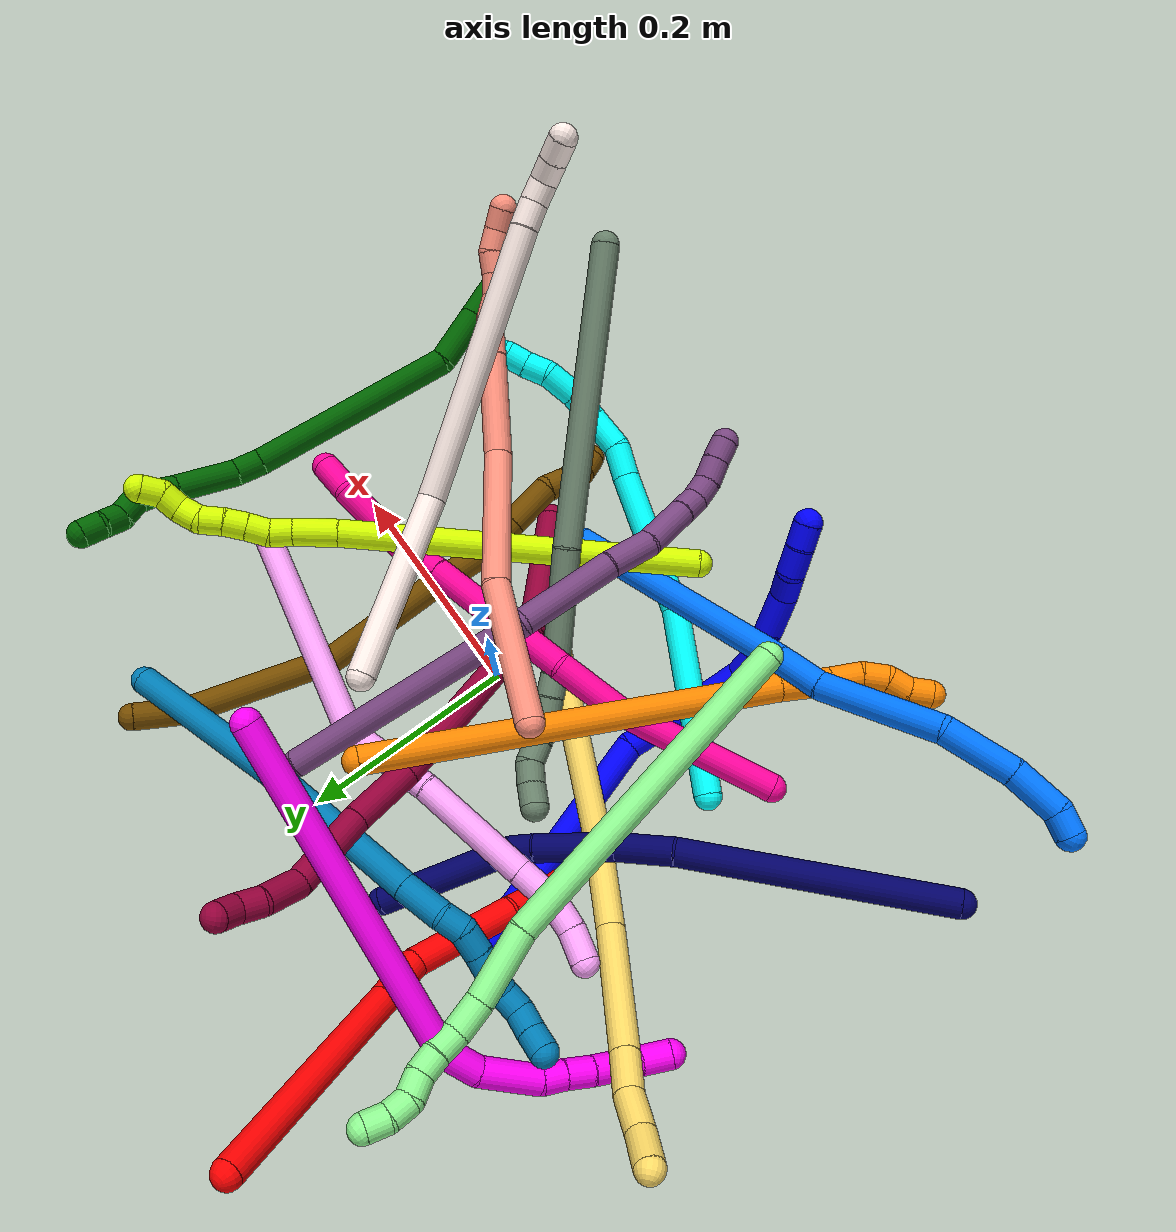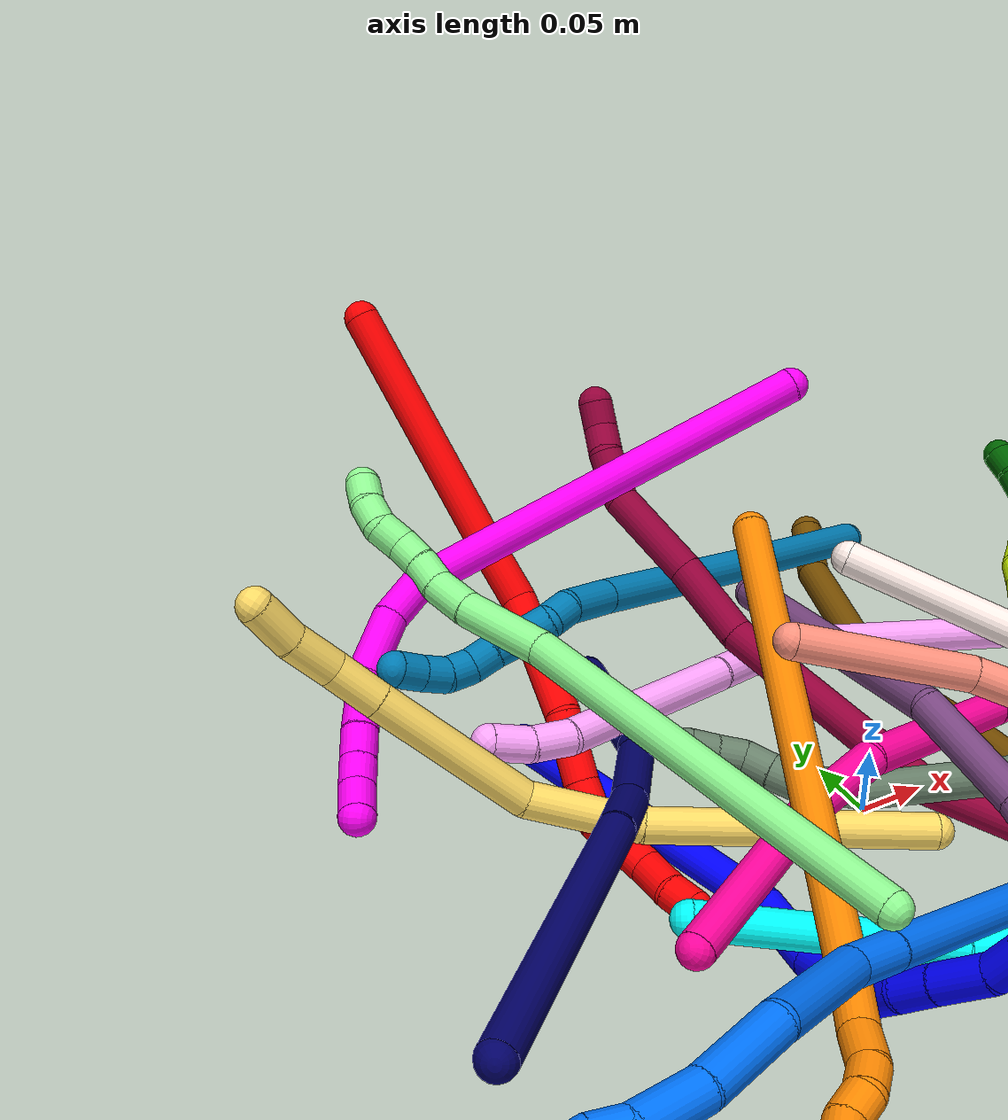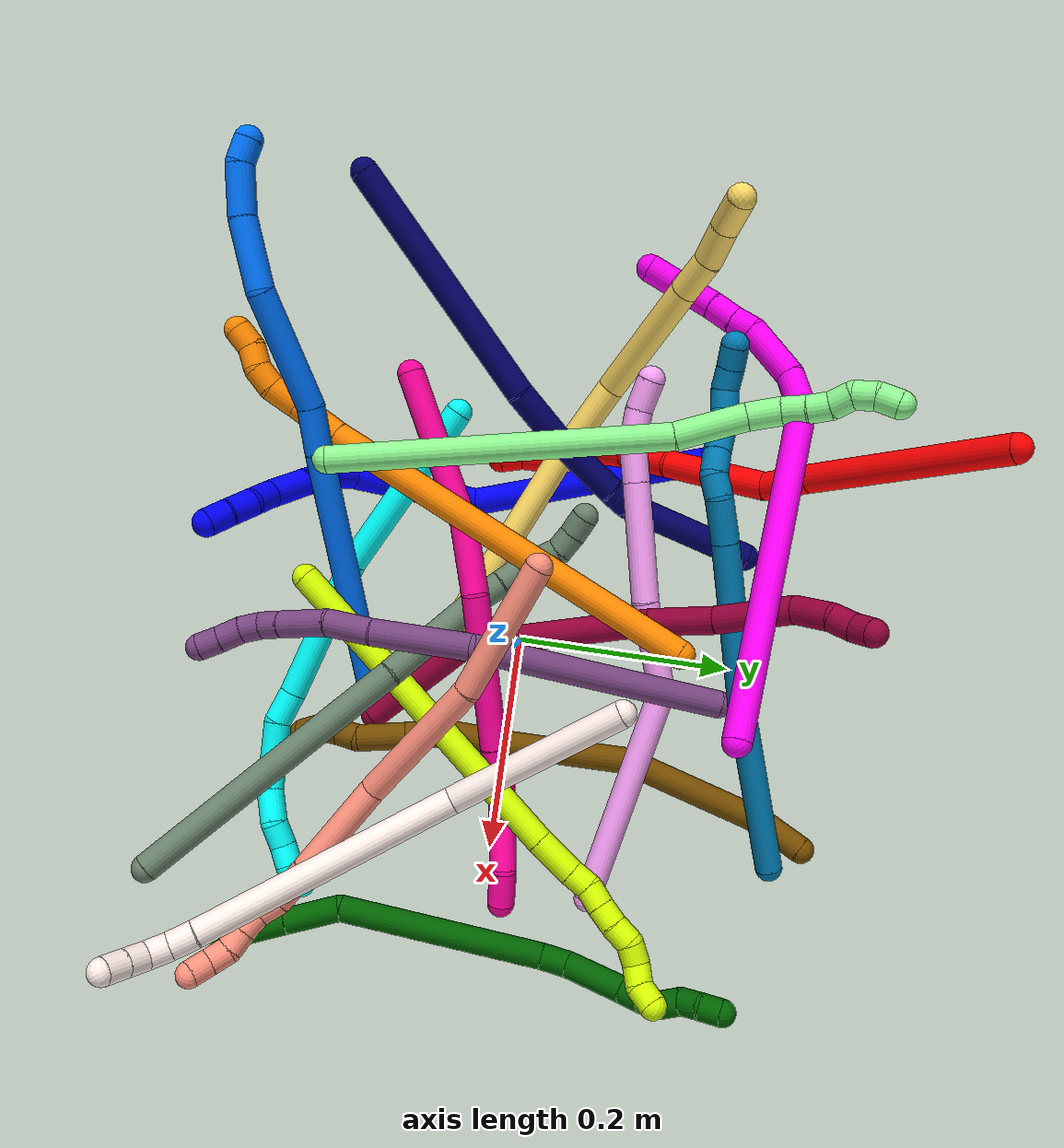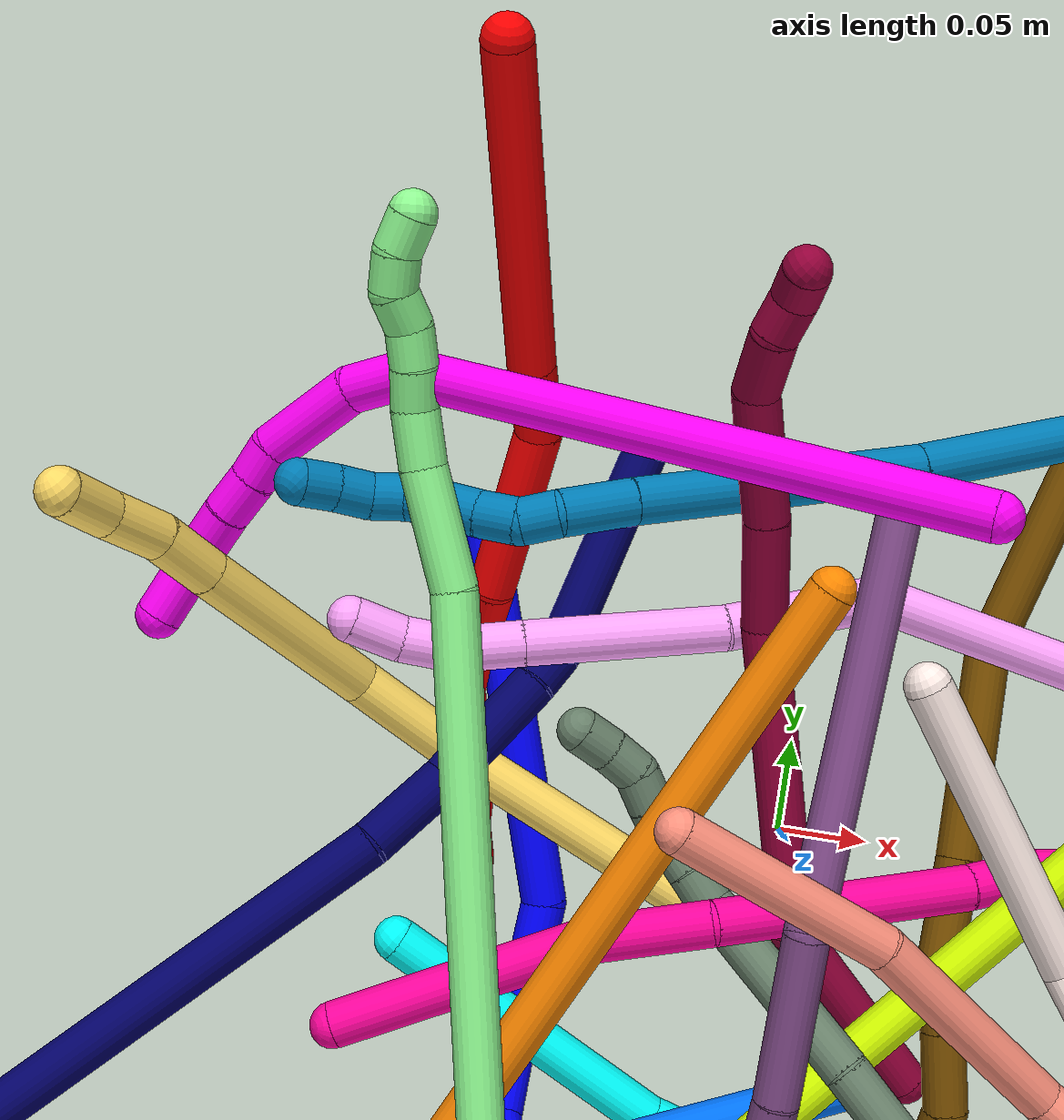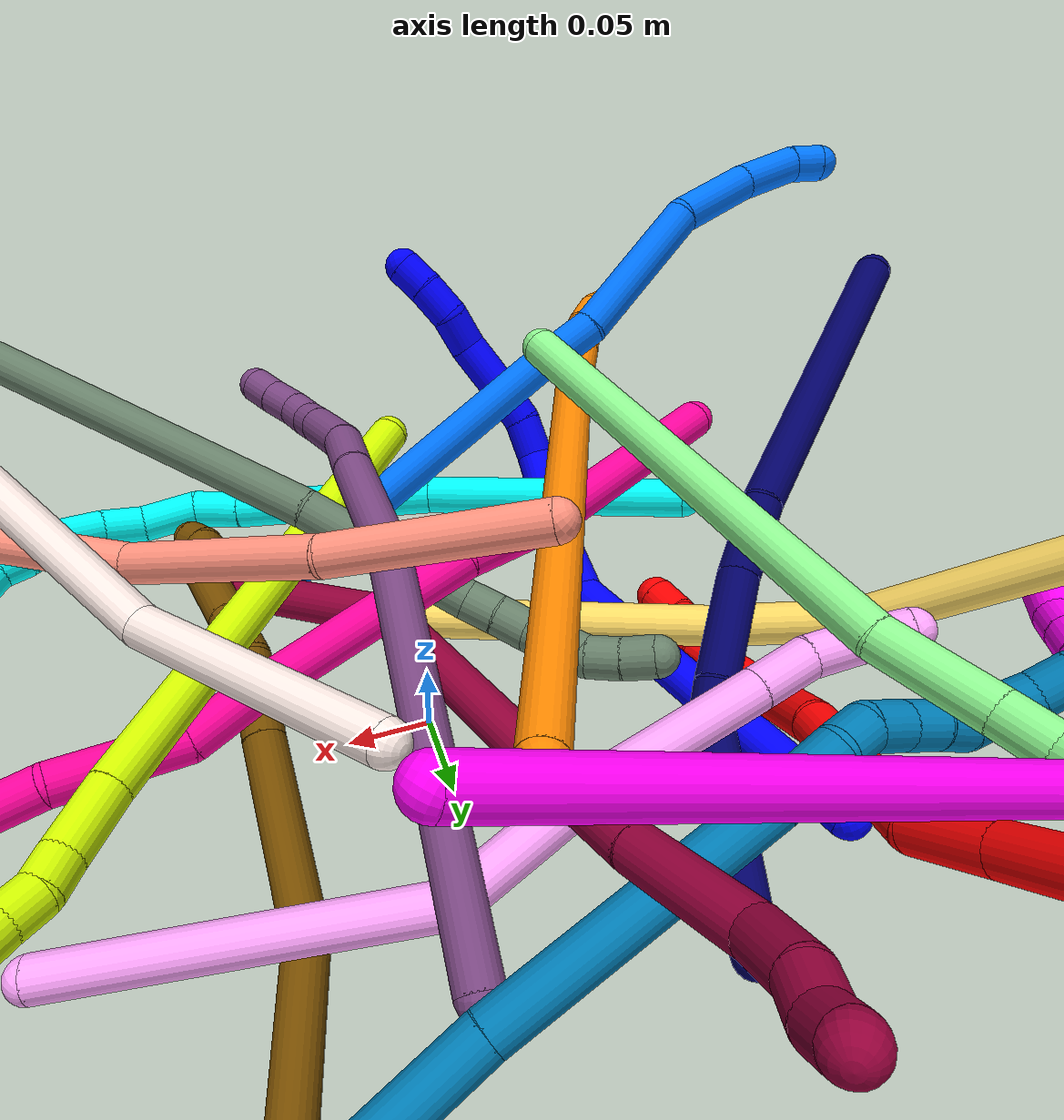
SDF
<sdf version="1.7">
 <world name="default">
  <plugin name="TubeGeneratorPlugin" filename="libtube_generator_plugin.so"/>
  <model name="photoneo_s_sensor">
   <static>1</static>
   <pose>0 0 2 1.57079 1.57079 3.14159</pose>
   <link name="link">
    <inertial><mass>0.1</mass></inertial>
    <sensor name="sensor" type="depth">
     <update_rate>30</update_rate>
     <camera>
      <horizontal_fov>1.22</horizontal_fov>
      <image><width>1920</width><height>1200</height><format>B8G8R8</format></image>
      <clip><near>0.1</near><far>4</far></clip>
      <depth_camera><output>points</output></depth_camera>
     </camera>
     <plugin name="camera_plugin" filename="libgazebo_ros_depth_camera.so">
      <baseline>0.2</baseline>
      <alwaysOn>1</alwaysOn>
      <updateRate>0.0</updateRate>
      <cameraName>camera_ir</cameraName>
      <imageTopicName>/camera/color/image_raw</imageTopicName>
      <cameraInfoTopicName>/camera/color/camera_info</cameraInfoTopicName>
      <depthImageTopicName>/camera/depth/image_raw</depthImageTopicName>
      <depthImageCameraInfoTopicName>/camera/depth/camera_info</depthImageCameraInfoTopicName>
      <pointCloudTopicName>/camera/depth/points</pointCloudTopicName>
      <frameName>fr_optical</frameName>
      <pointCloudCutoff>0.1</pointCloudCutoff>
      <pointCloudCutoffMax>2.0</pointCloudCutoffMax>
      <distortionK1>0</distortionK1>
      <distortionK2>0</distortionK2>
      <distortionK3>0</distortionK3>
      <distortionT1>0</distortionT1>
      <distortionT2>0</distortionT2>
      <CxPrime>0</CxPrime>
      <Cx>0</Cx>
      <Cy>0</Cy>
      <focalLength>0</focalLength>
      <hackBaseline>0</hackBaseline>
     </plugin>
    </sensor>
   </link>
  </model>
  <gravity>0 0 -9.8</gravity>
  <magnetic_field>6e-06 2.3e-05 -4.2e-05</magnetic_field>
  <atmosphere type="adiabatic"/>
  <physics name="default_physics" default="0" type="ode">
   <max_step_size>0.003</max_step_size>
   <real_time_factor>1</real_time_factor>
   <real_time_update_rate>1000</real_time_update_rate>
   <max_contacts>10000</max_contacts>
   <ode>
    <solver>
     <type>quick</type>
     <iters>100</iters>
     <sor>1.3</sor>
     <use_dynamic_moi_rescaling>0</use_dynamic_moi_rescaling>
    </solver>
    <constraints>
     <contact_max_correcting_vel>0</contact_max_correcting_vel>
     <contact_surface_layer>0.001</contact_surface_layer>
     <cfm>0</cfm>
     <erp>0.2</erp>
    </constraints>
   </ode>
  </physics>
  <scene><ambient>0.4 0.4 0.4 1</ambient><background>0.7 0.7 0.7 1</background><shadows>0</shadows></scene>
  <audio><device>default</device></audio>
  <spherical_coordinates>
   <surface_model>EARTH_WGS84</surface_model>
   <latitude_deg>0</latitude_deg>
   <longitude_deg>0</longitude_deg>
   <elevation>0</elevation>
   <heading_deg>0</heading_deg>
  </spherical_coordinates>
  <model name="bin">
   <static>1</static>
   <link name="bottom">
    <collision name="collision-bottom">
     <pose>0 0 -0.01 0 -0 0</pose>
     <geometry><box><size>0.8 0.6 0.02</size></box></geometry>
     <surface>
      <friction><ode><mu>100</mu><mu2>100</mu2></ode></friction>
      <contact><collide_bitmask>65535</collide_bitmask></contact>
     </surface>
    </collision>
   </link>
   <link name="west_wall">
    <collision name="collision-west_wall">
     <pose>-0.41 0 0.1 0 -0 0</pose>
     <geometry><box><size>0.02 0.6 0.2</size></box></geometry>
     <surface>
      <friction><ode><mu>100</mu><mu2>100</mu2></ode></friction>
      <contact><collide_bitmask>65535</collide_bitmask></contact>
     </surface>
    </collision>
   </link>
   <link name="east_wall">
    <collision name="collision-east_wall">
     <pose>0.41 0 0.1 0 -0 0</pose>
     <geometry><box><size>0.02 0.6 0.2</size></box></geometry>
     <surface>
      <friction><ode><mu>100</mu><mu2>100</mu2></ode></friction>
      <contact><collide_bitmask>65535</collide_bitmask></contact>
     </surface>
    </collision>
   </link>
   <link name="south_wall">
    <collision name="collision-south_wall">
     <pose>0 -0.31 0.1 0 -0 0</pose>
     <geometry><box><size>0.8 0.02 0.2</size></box></geometry>
     <surface>
      <friction><ode><mu>100</mu><mu2>100</mu2></ode></friction>
      <contact><collide_bitmask>65535</collide_bitmask></contact>
     </surface>
    </collision>
   </link>
   <link name="north_wall">
    <collision name="collision-north_wall">
     <pose>0 0.31 0.1 0 -0 0</pose>
     <geometry><box><size>0.8 0.02 0.2</size></box></geometry>
     <surface>
      <friction><ode><mu>100</mu><mu2>100</mu2></ode></friction>
      <contact><collide_bitmask>65535</collide_bitmask></contact>
     </surface>
    </collision>
   </link>
  </model>
  <model name="1">
   <static>0</static>
   <link name="1">
    <collision name="collision-cylinder-e_1_1_4">
     <pose>0.002174 -0.09189 -0.057215 2.1277 0.020078 0.036151</pose>
     <geometry><cylinder><radius>0.0125</radius><length>0.216537</length></cylinder></geometry>
     <surface>
      <friction><ode><mu>1.16</mu><mu2>1.16</mu2><slip1>0</slip1><slip2>0</slip2></ode></friction>
      <contact><ode><kp>1e+06</kp><kd>1</kd><max_vel>0</max_vel><min_depth>0.001</min_depth></ode></contact>
     </surface>
    </collision>
    <visual name="visual-cylinder-e_1_1_4">
     <pose>0.002174 -0.09189 -0.057215 2.1277 0.020078 0.036151</pose>
     <geometry><cylinder><radius>0.0125</radius><length>0.216537</length></cylinder></geometry>
     <material><ambient>0 0 1 1</ambient></material>
    </visual>
    <collision name="collision-cylinder-e_2_4_5">
     <pose>0.001167 -0.210648 -0.119643 1.76245 -0.11569 -0.140223</pose>
     <geometry><cylinder><radius>0.0125</radius><length>0.055107</length></cylinder></geometry>
     <surface>
      <friction><ode><mu>1.16</mu><mu2>1.16</mu2><slip1>0</slip1><slip2>0</slip2></ode></friction>
      <contact><ode><kp>1e+06</kp><kd>1</kd><max_vel>0</max_vel><min_depth>0.001</min_depth></ode></contact>
     </surface>
    </collision>
    <visual name="visual-cylinder-e_2_4_5">
     <pose>0.001167 -0.210648 -0.119643 1.76245 -0.11569 -0.140223</pose>
     <geometry><cylinder><radius>0.0125</radius><length>0.055107</length></cylinder></geometry>
     <material><ambient>0 0 1 1</ambient></material>
    </visual>
    <collision name="collision-cylinder-e_3_5_6">
     <pose>0.004878 -0.269294 -0.125164 1.58046 0.213569 0.215627</pose>
     <geometry><cylinder><radius>0.0125</radius><length>0.065036</length></cylinder></geometry>
     <surface>
      <friction><ode><mu>1.16</mu><mu2>1.16</mu2><slip1>0</slip1><slip2>0</slip2></ode></friction>
      <contact><ode><kp>1e+06</kp><kd>1</kd><max_vel>0</max_vel><min_depth>0.001</min_depth></ode></contact>
     </surface>
    </collision>
    <visual name="visual-cylinder-e_3_5_6">
     <pose>0.004878 -0.269294 -0.125164 1.58046 0.213569 0.215627</pose>
     <geometry><cylinder><radius>0.0125</radius><length>0.065036</length></cylinder></geometry>
     <material><ambient>0 0 1 1</ambient></material>
    </visual>
    <collision name="collision-cylinder-e_4_6_7">
     <pose>0.02022 -0.31166 -0.124674 1.49573 0.672152 0.626729</pose>
     <geometry><cylinder><radius>0.0125</radius><length>0.027141</length></cylinder></geometry>
     <surface>
      <friction><ode><mu>1.16</mu><mu2>1.16</mu2><slip1>0</slip1><slip2>0</slip2></ode></friction>
      <contact><ode><kp>1e+06</kp><kd>1</kd><max_vel>0</max_vel><min_depth>0.001</min_depth></ode></contact>
     </surface>
    </collision>
    <visual name="visual-cylinder-e_4_6_7">
     <pose>0.02022 -0.31166 -0.124674 1.49573 0.672152 0.626729</pose>
     <geometry><cylinder><radius>0.0125</radius><length>0.027141</length></cylinder></geometry>
     <material><ambient>0 0 1 1</ambient></material>
    </visual>
    <collision name="collision-cylinder-e_5_7_8">
     <pose>0.038094 -0.331693 -0.126228 1.81469 0.769301 0.955727</pose>
     <geometry><cylinder><radius>0.0125</radius><length>0.027093</length></cylinder></geometry>
     <surface>
      <friction><ode><mu>1.16</mu><mu2>1.16</mu2><slip1>0</slip1><slip2>0</slip2></ode></friction>
      <contact><ode><kp>1e+06</kp><kd>1</kd><max_vel>0</max_vel><min_depth>0.001</min_depth></ode></contact>
     </surface>
    </collision>
    <visual name="visual-cylinder-e_5_7_8">
     <pose>0.038094 -0.331693 -0.126228 1.81469 0.769301 0.955727</pose>
     <geometry><cylinder><radius>0.0125</radius><length>0.027093</length></cylinder></geometry>
     <material><ambient>0 0 1 1</ambient></material>
    </visual>
    <collision name="collision-cylinder-e_6_8_9">
     <pose>0.060393 -0.354003 -0.132911 1.89561 0.758958 1.01351</pose>
     <geometry><cylinder><radius>0.0125</radius><length>0.037422</length></cylinder></geometry>
     <surface>
      <friction><ode><mu>1.16</mu><mu2>1.16</mu2><slip1>0</slip1><slip2>0</slip2></ode></friction>
      <contact><ode><kp>1e+06</kp><kd>1</kd><max_vel>0</max_vel><min_depth>0.001</min_depth></ode></contact>
     </surface>
    </collision>
    <visual name="visual-cylinder-e_6_8_9">
     <pose>0.060393 -0.354003 -0.132911 1.89561 0.758958 1.01351</pose>
     <geometry><cylinder><radius>0.0125</radius><length>0.037422</length></cylinder></geometry>
     <material><ambient>0 0 1 1</ambient></material>
    </visual>
    <collision name="collision-cylinder-e_7_9_10">
     <pose>0.084342 -0.37302 -0.137484 1.60996 1.06336 1.09791</pose>
     <geometry><cylinder><radius>0.0125</radius><length>0.025336</length></cylinder></geometry>
     <surface>
      <friction><ode><mu>1.16</mu><mu2>1.16</mu2><slip1>0</slip1><slip2>0</slip2></ode></friction>
      <contact><ode><kp>1e+06</kp><kd>1</kd><max_vel>0</max_vel><min_depth>0.001</min_depth></ode></contact>
     </surface>
    </collision>
    <visual name="visual-cylinder-e_7_9_10">
     <pose>0.084342 -0.37302 -0.137484 1.60996 1.06336 1.09791</pose>
     <geometry><cylinder><radius>0.0125</radius><length>0.025336</length></cylinder></geometry>
     <material><ambient>0 0 1 1</ambient></material>
    </visual>
    <collision name="collision-cylinder-e_8_10_11">
     <pose>0.104255 -0.387201 -0.141165 1.97555 0.791393 1.12925</pose>
     <geometry><cylinder><radius>0.0125</radius><length>0.024859</length></cylinder></geometry>
     <surface>
      <friction><ode><mu>1.16</mu><mu2>1.16</mu2><slip1>0</slip1><slip2>0</slip2></ode></friction>
      <contact><ode><kp>1e+06</kp><kd>1</kd><max_vel>0</max_vel><min_depth>0.001</min_depth></ode></contact>
     </surface>
    </collision>
    <visual name="visual-cylinder-e_8_10_11">
     <pose>0.104255 -0.387201 -0.141165 1.97555 0.791393 1.12925</pose>
     <geometry><cylinder><radius>0.0125</radius><length>0.024859</length></cylinder></geometry>
     <material><ambient>0 0 1 1</ambient></material>
    </visual>
    <collision name="collision-cylinder-e_9_11_2">
     <pose>0.119866 -0.402497 -0.148682 2.08206 0.682384 1.09014</pose>
     <geometry><cylinder><radius>0.0125</radius><length>0.021469</length></cylinder></geometry>
     <surface>
      <friction><ode><mu>1.16</mu><mu2>1.16</mu2><slip1>0</slip1><slip2>0</slip2></ode></friction>
      <contact><ode><kp>1e+06</kp><kd>1</kd><max_vel>0</max_vel><min_depth>0.001</min_depth></ode></contact>
     </surface>
    </collision>
    <visual name="visual-cylinder-e_9_11_2">
     <pose>0.119866 -0.402497 -0.148682 2.08206 0.682384 1.09014</pose>
     <geometry><cylinder><radius>0.0125</radius><length>0.021469</length></cylinder></geometry>
     <material><ambient>0 0 1 1</ambient></material>
    </visual>
    <collision name="collision-sphere-2">
     <pose>0.126636 -0.409763 -0.152758 0 -0 0</pose>
     <geometry><sphere><radius>0.0125</radius></sphere></geometry>
     <surface>
      <friction><ode><mu>1.16</mu><mu2>1.16</mu2><slip1>0</slip1><slip2>0</slip2></ode></friction>
      <contact><ode><kp>1e+06</kp><kd>1</kd><max_vel>0</max_vel><min_depth>0.001</min_depth></ode></contact>
     </surface>
    </collision>
    <visual name="visual-sphere-2">
     <pose>0.126636 -0.409763 -0.152758 0 -0 0</pose>
     <geometry><sphere><radius>0.0125</radius></sphere></geometry>
     <material><ambient>0 0 1 1</ambient></material>
    </visual>
    <collision name="collision-sphere-11">
     <pose>0.113096 -0.395231 -0.144606 0 -0 0</pose>
     <geometry><sphere><radius>0.0125</radius></sphere></geometry>
     <surface>
      <friction><ode><mu>1.16</mu><mu2>1.16</mu2><slip1>0</slip1><slip2>0</slip2></ode></friction>
      <contact><ode><kp>1e+06</kp><kd>1</kd><max_vel>0</max_vel><min_depth>0.001</min_depth></ode></contact>
     </surface>
    </collision>
    <visual name="visual-sphere-11">
     <pose>0.113096 -0.395231 -0.144606 0 -0 0</pose>
     <geometry><sphere><radius>0.0125</radius></sphere></geometry>
     <material><ambient>0 0 1 1</ambient></material>
    </visual>
    <collision name="collision-sphere-10">
     <pose>0.095414 -0.379171 -0.137725 0 -0 0</pose>
     <geometry><sphere><radius>0.0125</radius></sphere></geometry>
     <surface>
      <friction><ode><mu>1.16</mu><mu2>1.16</mu2><slip1>0</slip1><slip2>0</slip2></ode></friction>
      <contact><ode><kp>1e+06</kp><kd>1</kd><max_vel>0</max_vel><min_depth>0.001</min_depth></ode></contact>
     </surface>
    </collision>
    <visual name="visual-sphere-10">
     <pose>0.095414 -0.379171 -0.137725 0 -0 0</pose>
     <geometry><sphere><radius>0.0125</radius></sphere></geometry>
     <material><ambient>0 0 1 1</ambient></material>
    </visual>
    <collision name="collision-sphere-9">
     <pose>0.07327 -0.366869 -0.137243 0 -0 0</pose>
     <geometry><sphere><radius>0.0125</radius></sphere></geometry>
     <surface>
      <friction><ode><mu>1.16</mu><mu2>1.16</mu2><slip1>0</slip1><slip2>0</slip2></ode></friction>
      <contact><ode><kp>1e+06</kp><kd>1</kd><max_vel>0</max_vel><min_depth>0.001</min_depth></ode></contact>
     </surface>
    </collision>
    <visual name="visual-sphere-9">
     <pose>0.07327 -0.366869 -0.137243 0 -0 0</pose>
     <geometry><sphere><radius>0.0125</radius></sphere></geometry>
     <material><ambient>0 0 1 1</ambient></material>
    </visual>
    <collision name="collision-sphere-4">
     <pose>0.004347 -0.18378 -0.11443 0 -0 0</pose>
     <geometry><sphere><radius>0.0125</radius></sphere></geometry>
     <surface>
      <friction><ode><mu>1.16</mu><mu2>1.16</mu2><slip1>0</slip1><slip2>0</slip2></ode></friction>
      <contact><ode><kp>1e+06</kp><kd>1</kd><max_vel>0</max_vel><min_depth>0.001</min_depth></ode></contact>
     </surface>
    </collision>
    <visual name="visual-sphere-4">
     <pose>0.004347 -0.18378 -0.11443 0 -0 0</pose>
     <geometry><sphere><radius>0.0125</radius></sphere></geometry>
     <material><ambient>0 0 1 1</ambient></material>
    </visual>
    <collision name="collision-sphere-1">
     <geometry><sphere><radius>0.0125</radius></sphere></geometry>
     <surface>
      <friction><ode><mu>1.16</mu><mu2>1.16</mu2><slip1>0</slip1><slip2>0</slip2></ode></friction>
      <contact><ode><kp>1e+06</kp><kd>1</kd><max_vel>0</max_vel><min_depth>0.001</min_depth></ode></contact>
     </surface>
    </collision>
    <visual name="visual-sphere-1">
     <geometry><sphere><radius>0.0125</radius></sphere></geometry>
     <material><ambient>0 0 1 1</ambient></material>
    </visual>
    <collision name="collision-sphere-8">
     <pose>0.047517 -0.341136 -0.128578 0 -0 0</pose>
     <geometry><sphere><radius>0.0125</radius></sphere></geometry>
     <surface>
      <friction><ode><mu>1.16</mu><mu2>1.16</mu2><slip1>0</slip1><slip2>0</slip2></ode></friction>
      <contact><ode><kp>1e+06</kp><kd>1</kd><max_vel>0</max_vel><min_depth>0.001</min_depth></ode></contact>
     </surface>
    </collision>
    <visual name="visual-sphere-8">
     <pose>0.047517 -0.341136 -0.128578 0 -0 0</pose>
     <geometry><sphere><radius>0.0125</radius></sphere></geometry>
     <material><ambient>0 0 1 1</ambient></material>
    </visual>
    <collision name="collision-sphere-5">
     <pose>-0.002014 -0.237516 -0.124857 0 -0 0</pose>
     <geometry><sphere><radius>0.0125</radius></sphere></geometry>
     <surface>
      <friction><ode><mu>1.16</mu><mu2>1.16</mu2><slip1>0</slip1><slip2>0</slip2></ode></friction>
      <contact><ode><kp>1e+06</kp><kd>1</kd><max_vel>0</max_vel><min_depth>0.001</min_depth></ode></contact>
     </surface>
    </collision>
    <visual name="visual-sphere-5">
     <pose>-0.002014 -0.237516 -0.124857 0 -0 0</pose>
     <geometry><sphere><radius>0.0125</radius></sphere></geometry>
     <material><ambient>0 0 1 1</ambient></material>
    </visual>
    <collision name="collision-sphere-6">
     <pose>0.011771 -0.301072 -0.125471 0 -0 0</pose>
     <geometry><sphere><radius>0.0125</radius></sphere></geometry>
     <surface>
      <friction><ode><mu>1.16</mu><mu2>1.16</mu2><slip1>0</slip1><slip2>0</slip2></ode></friction>
      <contact><ode><kp>1e+06</kp><kd>1</kd><max_vel>0</max_vel><min_depth>0.001</min_depth></ode></contact>
     </surface>
    </collision>
    <visual name="visual-sphere-6">
     <pose>0.011771 -0.301072 -0.125471 0 -0 0</pose>
     <geometry><sphere><radius>0.0125</radius></sphere></geometry>
     <material><ambient>0 0 1 1</ambient></material>
    </visual>
    <collision name="collision-sphere-7">
     <pose>0.02867 -0.322249 -0.123878 0 -0 0</pose>
     <geometry><sphere><radius>0.0125</radius></sphere></geometry>
     <surface>
      <friction><ode><mu>1.16</mu><mu2>1.16</mu2><slip1>0</slip1><slip2>0</slip2></ode></friction>
      <contact><ode><kp>1e+06</kp><kd>1</kd><max_vel>0</max_vel><min_depth>0.001</min_depth></ode></contact>
     </surface>
    </collision>
    <visual name="visual-sphere-7">
     <pose>0.02867 -0.322249 -0.123878 0 -0 0</pose>
     <geometry><sphere><radius>0.0125</radius></sphere></geometry>
     <material><ambient>0 0 1 1</ambient></material>
    </visual>
    <inertial>
     <pose>0.02399 -0.21486 -0.098169 0 -0 0</pose>
     <mass>0.5</mass>
     <inertia>
      <ixx>0.000955</ixx>
      <ixy>0</ixy>
      <ixz>0</ixz>
      <iyy>-0.000433</iyy>
      <iyz>0</iyz>
      <izz>0.000733</izz>
     </inertia>
    </inertial>
   </link>
   <pose>-0.190546 0.146224 0.030057 -0.368206 -1.01294 0.142657</pose>
  </model>
  <model name="2">
   <static>0</static>
   <link name="2">
    <collision name="collision-cylinder-e_1_1_4">
     <pose>0.010794 0.000619 -0.092736 -3.13491 0.115872 -3.02655</pose>
     <geometry><cylinder><radius>0.0125</radius><length>0.186729</length></cylinder></geometry>
     <surface>
      <friction><ode><mu>1.16</mu><mu2>1.16</mu2><slip1>0</slip1><slip2>0</slip2></ode></friction>
      <contact><ode><kp>1e+06</kp><kd>1</kd><max_vel>0</max_vel><min_depth>0.001</min_depth></ode></contact>
     </surface>
    </collision>
    <visual name="visual-cylinder-e_1_1_4">
     <pose>0.010794 0.000619 -0.092736 -3.13491 0.115872 -3.02655</pose>
     <geometry><cylinder><radius>0.0125</radius><length>0.186729</length></cylinder></geometry>
     <material><ambient>1 0 0 1</ambient></material>
    </visual>
    <collision name="collision-cylinder-e_2_4_5">
     <pose>0.024774 0.0011 -0.207862 3.13538 0.141333 3.05383</pose>
     <geometry><cylinder><radius>0.0125</radius><length>0.04523</length></cylinder></geometry>
     <surface>
      <friction><ode><mu>1.16</mu><mu2>1.16</mu2><slip1>0</slip1><slip2>0</slip2></ode></friction>
      <contact><ode><kp>1e+06</kp><kd>1</kd><max_vel>0</max_vel><min_depth>0.001</min_depth></ode></contact>
     </surface>
    </collision>
    <visual name="visual-cylinder-e_2_4_5">
     <pose>0.024774 0.0011 -0.207862 3.13538 0.141333 3.05383</pose>
     <geometry><cylinder><radius>0.0125</radius><length>0.04523</length></cylinder></geometry>
     <material><ambient>1 0 0 1</ambient></material>
    </visual>
    <collision name="collision-cylinder-e_3_5_6">
     <pose>0.017573 -0.011916 -0.274359 2.85755 -0.222312 -1.32563</pose>
     <geometry><cylinder><radius>0.0125</radius><length>0.094217</length></cylinder></geometry>
     <surface>
      <friction><ode><mu>1.16</mu><mu2>1.16</mu2><slip1>0</slip1><slip2>0</slip2></ode></friction>
      <contact><ode><kp>1e+06</kp><kd>1</kd><max_vel>0</max_vel><min_depth>0.001</min_depth></ode></contact>
     </surface>
    </collision>
    <visual name="visual-cylinder-e_3_5_6">
     <pose>0.017573 -0.011916 -0.274359 2.85755 -0.222312 -1.32563</pose>
     <geometry><cylinder><radius>0.0125</radius><length>0.094217</length></cylinder></geometry>
     <material><ambient>1 0 0 1</ambient></material>
    </visual>
    <collision name="collision-cylinder-e_4_6_7">
     <pose>0.002472 -0.02565 -0.342847 3.10645 -0.190881 -2.77855</pose>
     <geometry><cylinder><radius>0.0125</radius><length>0.049693</length></cylinder></geometry>
     <surface>
      <friction><ode><mu>1.16</mu><mu2>1.16</mu2><slip1>0</slip1><slip2>0</slip2></ode></friction>
      <contact><ode><kp>1e+06</kp><kd>1</kd><max_vel>0</max_vel><min_depth>0.001</min_depth></ode></contact>
     </surface>
    </collision>
    <visual name="visual-cylinder-e_4_6_7">
     <pose>0.002472 -0.02565 -0.342847 3.10645 -0.190881 -2.77855</pose>
     <geometry><cylinder><radius>0.0125</radius><length>0.049693</length></cylinder></geometry>
     <material><ambient>1 0 0 1</ambient></material>
    </visual>
    <collision name="collision-cylinder-e_5_7_8">
     <pose>-0.00395 -0.027933 -0.380915 3.03777 -0.123465 -1.74361</pose>
     <geometry><cylinder><radius>0.0125</radius><length>0.027734</length></cylinder></geometry>
     <surface>
      <friction><ode><mu>1.16</mu><mu2>1.16</mu2><slip1>0</slip1><slip2>0</slip2></ode></friction>
      <contact><ode><kp>1e+06</kp><kd>1</kd><max_vel>0</max_vel><min_depth>0.001</min_depth></ode></contact>
     </surface>
    </collision>
    <visual name="visual-cylinder-e_5_7_8">
     <pose>-0.00395 -0.027933 -0.380915 3.03777 -0.123465 -1.74361</pose>
     <geometry><cylinder><radius>0.0125</radius><length>0.027734</length></cylinder></geometry>
     <material><ambient>1 0 0 1</ambient></material>
    </visual>
    <collision name="collision-cylinder-e_6_8_9">
     <pose>-0.001974 -0.041287 -0.414907 2.61046 0.155169 0.556796</pose>
     <geometry><cylinder><radius>0.0125</radius><length>0.047672</length></cylinder></geometry>
     <surface>
      <friction><ode><mu>1.16</mu><mu2>1.16</mu2><slip1>0</slip1><slip2>0</slip2></ode></friction>
      <contact><ode><kp>1e+06</kp><kd>1</kd><max_vel>0</max_vel><min_depth>0.001</min_depth></ode></contact>
     </surface>
    </collision>
    <visual name="visual-cylinder-e_6_8_9">
     <pose>-0.001974 -0.041287 -0.414907 2.61046 0.155169 0.556796</pose>
     <geometry><cylinder><radius>0.0125</radius><length>0.047672</length></cylinder></geometry>
     <material><ambient>1 0 0 1</ambient></material>
    </visual>
    <collision name="collision-cylinder-e_7_9_10">
     <pose>4.5e-05 -0.063169 -0.445141 2.3549 -0.117864 -0.282465</pose>
     <geometry><cylinder><radius>0.0125</radius><length>0.028314</length></cylinder></geometry>
     <surface>
      <friction><ode><mu>1.16</mu><mu2>1.16</mu2><slip1>0</slip1><slip2>0</slip2></ode></friction>
      <contact><ode><kp>1e+06</kp><kd>1</kd><max_vel>0</max_vel><min_depth>0.001</min_depth></ode></contact>
     </surface>
    </collision>
    <visual name="visual-cylinder-e_7_9_10">
     <pose>4.5e-05 -0.063169 -0.445141 2.3549 -0.117864 -0.282465</pose>
     <geometry><cylinder><radius>0.0125</radius><length>0.028314</length></cylinder></geometry>
     <material><ambient>1 0 0 1</ambient></material>
    </visual>
    <collision name="collision-cylinder-e_8_10_2">
     <pose>-0.000446 -0.079739 -0.46275 2.43056 0.115238 0.30825</pose>
     <geometry><cylinder><radius>0.0125</radius><length>0.020411</length></cylinder></geometry>
     <surface>
      <friction><ode><mu>1.16</mu><mu2>1.16</mu2><slip1>0</slip1><slip2>0</slip2></ode></friction>
      <contact><ode><kp>1e+06</kp><kd>1</kd><max_vel>0</max_vel><min_depth>0.001</min_depth></ode></contact>
     </surface>
    </collision>
    <visual name="visual-cylinder-e_8_10_2">
     <pose>-0.000446 -0.079739 -0.46275 2.43056 0.115238 0.30825</pose>
     <geometry><cylinder><radius>0.0125</radius><length>0.020411</length></cylinder></geometry>
     <material><ambient>1 0 0 1</ambient></material>
    </visual>
    <collision name="collision-sphere-2">
     <pose>0.000728 -0.086355 -0.470432 0 -0 0</pose>
     <geometry><sphere><radius>0.0125</radius></sphere></geometry>
     <surface>
      <friction><ode><mu>1.16</mu><mu2>1.16</mu2><slip1>0</slip1><slip2>0</slip2></ode></friction>
      <contact><ode><kp>1e+06</kp><kd>1</kd><max_vel>0</max_vel><min_depth>0.001</min_depth></ode></contact>
     </surface>
    </collision>
    <visual name="visual-sphere-2">
     <pose>0.000728 -0.086355 -0.470432 0 -0 0</pose>
     <geometry><sphere><radius>0.0125</radius></sphere></geometry>
     <material><ambient>1 0 0 1</ambient></material>
    </visual>
    <collision name="collision-sphere-10">
     <pose>-0.001619 -0.073123 -0.455069 0 -0 0</pose>
     <geometry><sphere><radius>0.0125</radius></sphere></geometry>
     <surface>
      <friction><ode><mu>1.16</mu><mu2>1.16</mu2><slip1>0</slip1><slip2>0</slip2></ode></friction>
      <contact><ode><kp>1e+06</kp><kd>1</kd><max_vel>0</max_vel><min_depth>0.001</min_depth></ode></contact>
     </surface>
    </collision>
    <visual name="visual-sphere-10">
     <pose>-0.001619 -0.073123 -0.455069 0 -0 0</pose>
     <geometry><sphere><radius>0.0125</radius></sphere></geometry>
     <material><ambient>1 0 0 1</ambient></material>
    </visual>
    <collision name="collision-sphere-9">
     <pose>0.00171 -0.053215 -0.435213 0 -0 0</pose>
     <geometry><sphere><radius>0.0125</radius></sphere></geometry>
     <surface>
      <friction><ode><mu>1.16</mu><mu2>1.16</mu2><slip1>0</slip1><slip2>0</slip2></ode></friction>
      <contact><ode><kp>1e+06</kp><kd>1</kd><max_vel>0</max_vel><min_depth>0.001</min_depth></ode></contact>
     </surface>
    </collision>
    <visual name="visual-sphere-9">
     <pose>0.00171 -0.053215 -0.435213 0 -0 0</pose>
     <geometry><sphere><radius>0.0125</radius></sphere></geometry>
     <material><ambient>1 0 0 1</ambient></material>
    </visual>
    <collision name="collision-sphere-4">
     <pose>0.021588 0.001239 -0.185473 0 -0 0</pose>
     <geometry><sphere><radius>0.0125</radius></sphere></geometry>
     <surface>
      <friction><ode><mu>1.16</mu><mu2>1.16</mu2><slip1>0</slip1><slip2>0</slip2></ode></friction>
      <contact><ode><kp>1e+06</kp><kd>1</kd><max_vel>0</max_vel><min_depth>0.001</min_depth></ode></contact>
     </surface>
    </collision>
    <visual name="visual-sphere-4">
     <pose>0.021588 0.001239 -0.185473 0 -0 0</pose>
     <geometry><sphere><radius>0.0125</radius></sphere></geometry>
     <material><ambient>1 0 0 1</ambient></material>
    </visual>
    <collision name="collision-sphere-1">
     <geometry><sphere><radius>0.0125</radius></sphere></geometry>
     <surface>
      <friction><ode><mu>1.16</mu><mu2>1.16</mu2><slip1>0</slip1><slip2>0</slip2></ode></friction>
      <contact><ode><kp>1e+06</kp><kd>1</kd><max_vel>0</max_vel><min_depth>0.001</min_depth></ode></contact>
     </surface>
    </collision>
    <visual name="visual-sphere-1">
     <geometry><sphere><radius>0.0125</radius></sphere></geometry>
     <material><ambient>1 0 0 1</ambient></material>
    </visual>
    <collision name="collision-sphere-8">
     <pose>-0.005657 -0.029359 -0.394602 0 -0 0</pose>
     <geometry><sphere><radius>0.0125</radius></sphere></geometry>
     <surface>
      <friction><ode><mu>1.16</mu><mu2>1.16</mu2><slip1>0</slip1><slip2>0</slip2></ode></friction>
      <contact><ode><kp>1e+06</kp><kd>1</kd><max_vel>0</max_vel><min_depth>0.001</min_depth></ode></contact>
     </surface>
    </collision>
    <visual name="visual-sphere-8">
     <pose>-0.005657 -0.029359 -0.394602 0 -0 0</pose>
     <geometry><sphere><radius>0.0125</radius></sphere></geometry>
     <material><ambient>1 0 0 1</ambient></material>
    </visual>
    <collision name="collision-sphere-5">
     <pose>0.02796 0.000961 -0.230251 0 -0 0</pose>
     <geometry><sphere><radius>0.0125</radius></sphere></geometry>
     <surface>
      <friction><ode><mu>1.16</mu><mu2>1.16</mu2><slip1>0</slip1><slip2>0</slip2></ode></friction>
      <contact><ode><kp>1e+06</kp><kd>1</kd><max_vel>0</max_vel><min_depth>0.001</min_depth></ode></contact>
     </surface>
    </collision>
    <visual name="visual-sphere-5">
     <pose>0.02796 0.000961 -0.230251 0 -0 0</pose>
     <geometry><sphere><radius>0.0125</radius></sphere></geometry>
     <material><ambient>1 0 0 1</ambient></material>
    </visual>
    <collision name="collision-sphere-6">
     <pose>0.007186 -0.024793 -0.318467 0 -0 0</pose>
     <geometry><sphere><radius>0.0125</radius></sphere></geometry>
     <surface>
      <friction><ode><mu>1.16</mu><mu2>1.16</mu2><slip1>0</slip1><slip2>0</slip2></ode></friction>
      <contact><ode><kp>1e+06</kp><kd>1</kd><max_vel>0</max_vel><min_depth>0.001</min_depth></ode></contact>
     </surface>
    </collision>
    <visual name="visual-sphere-6">
     <pose>0.007186 -0.024793 -0.318467 0 -0 0</pose>
     <geometry><sphere><radius>0.0125</radius></sphere></geometry>
     <material><ambient>1 0 0 1</ambient></material>
    </visual>
    <collision name="collision-sphere-7">
     <pose>-0.002242 -0.026507 -0.367227 0 -0 0</pose>
     <geometry><sphere><radius>0.0125</radius></sphere></geometry>
     <surface>
      <friction><ode><mu>1.16</mu><mu2>1.16</mu2><slip1>0</slip1><slip2>0</slip2></ode></friction>
      <contact><ode><kp>1e+06</kp><kd>1</kd><max_vel>0</max_vel><min_depth>0.001</min_depth></ode></contact>
     </surface>
    </collision>
    <visual name="visual-sphere-7">
     <pose>-0.002242 -0.026507 -0.367227 0 -0 0</pose>
     <geometry><sphere><radius>0.0125</radius></sphere></geometry>
     <material><ambient>1 0 0 1</ambient></material>
    </visual>
    <inertial>
     <pose>0.009406 -0.016782 -0.243994 0 -0 0</pose>
     <mass>0.5</mass>
     <inertia>
      <ixx>-0.000666</ixx>
      <ixy>0</ixy>
      <ixz>0</ixz>
      <iyy>0.000405</iyy>
      <iyz>0</iyz>
      <izz>-5.9e-05</izz>
     </inertia>
    </inertial>
   </link>
   <pose>-0.208262 0.357662 0.274721 -0.812094 0.072028 0.146966</pose>
  </model>
  <model name="3">
   <static>0</static>
   <link name="3">
    <collision name="collision-cylinder-e_1_1_4">
     <pose>0.009654 0.024155 -0.082222 -2.85586 0.11218 -0.744285</pose>
     <geometry><cylinder><radius>0.0125</radius><length>0.172478</length></cylinder></geometry>
     <surface>
      <friction><ode><mu>1.16</mu><mu2>1.16</mu2><slip1>0</slip1><slip2>0</slip2></ode></friction>
      <contact><ode><kp>1e+06</kp><kd>1</kd><max_vel>0</max_vel><min_depth>0.001</min_depth></ode></contact>
     </surface>
    </collision>
    <visual name="visual-cylinder-e_1_1_4">
     <pose>0.009654 0.024155 -0.082222 -2.85586 0.11218 -0.744285</pose>
     <geometry><cylinder><radius>0.0125</radius><length>0.172478</length></cylinder></geometry>
     <material><ambient>0.003922 1 0.996078 1</ambient></material>
    </visual>
    <collision name="collision-cylinder-e_2_4_5">
     <pose>0.039225 0.063765 -0.22733 -2.9006 0.298384 -1.78533</pose>
     <geometry><cylinder><radius>0.0125</radius><length>0.135502</length></cylinder></geometry>
     <surface>
      <friction><ode><mu>1.16</mu><mu2>1.16</mu2><slip1>0</slip1><slip2>0</slip2></ode></friction>
      <contact><ode><kp>1e+06</kp><kd>1</kd><max_vel>0</max_vel><min_depth>0.001</min_depth></ode></contact>
     </surface>
    </collision>
    <visual name="visual-cylinder-e_2_4_5">
     <pose>0.039225 0.063765 -0.22733 -2.9006 0.298384 -1.78533</pose>
     <geometry><cylinder><radius>0.0125</radius><length>0.135502</length></cylinder></geometry>
     <material><ambient>0.003922 1 0.996078 1</ambient></material>
    </visual>
    <collision name="collision-cylinder-e_3_5_6">
     <pose>0.062955 0.081426 -0.305003 -2.99358 0.249729 -2.07452</pose>
     <geometry><cylinder><radius>0.0125</radius><length>0.030859</length></cylinder></geometry>
     <surface>
      <friction><ode><mu>1.16</mu><mu2>1.16</mu2><slip1>0</slip1><slip2>0</slip2></ode></friction>
      <contact><ode><kp>1e+06</kp><kd>1</kd><max_vel>0</max_vel><min_depth>0.001</min_depth></ode></contact>
     </surface>
    </collision>
    <visual name="visual-cylinder-e_3_5_6">
     <pose>0.062955 0.081426 -0.305003 -2.99358 0.249729 -2.07452</pose>
     <geometry><cylinder><radius>0.0125</radius><length>0.030859</length></cylinder></geometry>
     <material><ambient>0.003922 1 0.996078 1</ambient></material>
    </visual>
    <collision name="collision-cylinder-e_4_6_7">
     <pose>0.077587 0.087432 -0.334624 -2.89075 0.615058 -2.38578</pose>
     <geometry><cylinder><radius>0.0125</radius><length>0.037498</length></cylinder></geometry>
     <surface>
      <friction><ode><mu>1.16</mu><mu2>1.16</mu2><slip1>0</slip1><slip2>0</slip2></ode></friction>
      <contact><ode><kp>1e+06</kp><kd>1</kd><max_vel>0</max_vel><min_depth>0.001</min_depth></ode></contact>
     </surface>
    </collision>
    <visual name="visual-cylinder-e_4_6_7">
     <pose>0.077587 0.087432 -0.334624 -2.89075 0.615058 -2.38578</pose>
     <geometry><cylinder><radius>0.0125</radius><length>0.037498</length></cylinder></geometry>
     <material><ambient>0.003922 1 0.996078 1</ambient></material>
    </visual>
    <collision name="collision-cylinder-e_5_7_8">
     <pose>0.097145 0.089695 -0.360627 3.00475 0.659418 2.7463</pose>
     <geometry><cylinder><radius>0.0125</radius><length>0.02853</length></cylinder></geometry>
     <surface>
      <friction><ode><mu>1.16</mu><mu2>1.16</mu2><slip1>0</slip1><slip2>0</slip2></ode></friction>
      <contact><ode><kp>1e+06</kp><kd>1</kd><max_vel>0</max_vel><min_depth>0.001</min_depth></ode></contact>
     </surface>
    </collision>
    <visual name="visual-cylinder-e_5_7_8">
     <pose>0.097145 0.089695 -0.360627 3.00475 0.659418 2.7463</pose>
     <geometry><cylinder><radius>0.0125</radius><length>0.02853</length></cylinder></geometry>
     <material><ambient>0.003922 1 0.996078 1</ambient></material>
    </visual>
    <collision name="collision-cylinder-e_6_8_9">
     <pose>0.117776 0.085538 -0.381466 2.87713 0.870704 2.58452</pose>
     <geometry><cylinder><radius>0.0125</radius><length>0.0311</length></cylinder></geometry>
     <surface>
      <friction><ode><mu>1.16</mu><mu2>1.16</mu2><slip1>0</slip1><slip2>0</slip2></ode></friction>
      <contact><ode><kp>1e+06</kp><kd>1</kd><max_vel>0</max_vel><min_depth>0.001</min_depth></ode></contact>
     </surface>
    </collision>
    <visual name="visual-cylinder-e_6_8_9">
     <pose>0.117776 0.085538 -0.381466 2.87713 0.870704 2.58452</pose>
     <geometry><cylinder><radius>0.0125</radius><length>0.0311</length></cylinder></geometry>
     <material><ambient>0.003922 1 0.996078 1</ambient></material>
    </visual>
    <collision name="collision-cylinder-e_7_9_10">
     <pose>0.139879 0.08471 -0.396084 -2.79434 1.09496 -2.58134</pose>
     <geometry><cylinder><radius>0.0125</radius><length>0.022973</length></cylinder></geometry>
     <surface>
      <friction><ode><mu>1.16</mu><mu2>1.16</mu2><slip1>0</slip1><slip2>0</slip2></ode></friction>
      <contact><ode><kp>1e+06</kp><kd>1</kd><max_vel>0</max_vel><min_depth>0.001</min_depth></ode></contact>
     </surface>
    </collision>
    <visual name="visual-cylinder-e_7_9_10">
     <pose>0.139879 0.08471 -0.396084 -2.79434 1.09496 -2.58134</pose>
     <geometry><cylinder><radius>0.0125</radius><length>0.022973</length></cylinder></geometry>
     <material><ambient>0.003922 1 0.996078 1</ambient></material>
    </visual>
    <collision name="collision-cylinder-e_8_10_11">
     <pose>0.158765 0.085707 -0.406045 2.98466 1.04142 2.86909</pose>
     <geometry><cylinder><radius>0.0125</radius><length>0.020102</length></cylinder></geometry>
     <surface>
      <friction><ode><mu>1.16</mu><mu2>1.16</mu2><slip1>0</slip1><slip2>0</slip2></ode></friction>
      <contact><ode><kp>1e+06</kp><kd>1</kd><max_vel>0</max_vel><min_depth>0.001</min_depth></ode></contact>
     </surface>
    </collision>
    <visual name="visual-cylinder-e_8_10_11">
     <pose>0.158765 0.085707 -0.406045 2.98466 1.04142 2.86909</pose>
     <geometry><cylinder><radius>0.0125</radius><length>0.020102</length></cylinder></geometry>
     <material><ambient>0.003922 1 0.996078 1</ambient></material>
    </visual>
    <collision name="collision-cylinder-e_9_11_2">
     <pose>0.177366 0.087329 -0.413395 -2.33972 1.24437 -2.074</pose>
     <geometry><cylinder><radius>0.0125</radius><length>0.020959</length></cylinder></geometry>
     <surface>
      <friction><ode><mu>1.16</mu><mu2>1.16</mu2><slip1>0</slip1><slip2>0</slip2></ode></friction>
      <contact><ode><kp>1e+06</kp><kd>1</kd><max_vel>0</max_vel><min_depth>0.001</min_depth></ode></contact>
     </surface>
    </collision>
    <visual name="visual-cylinder-e_9_11_2">
     <pose>0.177366 0.087329 -0.413395 -2.33972 1.24437 -2.074</pose>
     <geometry><cylinder><radius>0.0125</radius><length>0.020959</length></cylinder></geometry>
     <material><ambient>0.003922 1 0.996078 1</ambient></material>
    </visual>
    <collision name="collision-sphere-2">
     <pose>0.187293 0.089744 -0.415731 0 -0 0</pose>
     <geometry><sphere><radius>0.0125</radius></sphere></geometry>
     <surface>
      <friction><ode><mu>1.16</mu><mu2>1.16</mu2><slip1>0</slip1><slip2>0</slip2></ode></friction>
      <contact><ode><kp>1e+06</kp><kd>1</kd><max_vel>0</max_vel><min_depth>0.001</min_depth></ode></contact>
     </surface>
    </collision>
    <visual name="visual-sphere-2">
     <pose>0.187293 0.089744 -0.415731 0 -0 0</pose>
     <geometry><sphere><radius>0.0125</radius></sphere></geometry>
     <material><ambient>0.003922 1 0.996078 1</ambient></material>
    </visual>
    <collision name="collision-sphere-11">
     <pose>0.16744 0.084914 -0.411058 0 -0 0</pose>
     <geometry><sphere><radius>0.0125</radius></sphere></geometry>
     <surface>
      <friction><ode><mu>1.16</mu><mu2>1.16</mu2><slip1>0</slip1><slip2>0</slip2></ode></friction>
      <contact><ode><kp>1e+06</kp><kd>1</kd><max_vel>0</max_vel><min_depth>0.001</min_depth></ode></contact>
     </surface>
    </collision>
    <visual name="visual-sphere-11">
     <pose>0.16744 0.084914 -0.411058 0 -0 0</pose>
     <geometry><sphere><radius>0.0125</radius></sphere></geometry>
     <material><ambient>0.003922 1 0.996078 1</ambient></material>
    </visual>
    <collision name="collision-sphere-10">
     <pose>0.15009 0.0865 -0.401032 0 -0 0</pose>
     <geometry><sphere><radius>0.0125</radius></sphere></geometry>
     <surface>
      <friction><ode><mu>1.16</mu><mu2>1.16</mu2><slip1>0</slip1><slip2>0</slip2></ode></friction>
      <contact><ode><kp>1e+06</kp><kd>1</kd><max_vel>0</max_vel><min_depth>0.001</min_depth></ode></contact>
     </surface>
    </collision>
    <visual name="visual-sphere-10">
     <pose>0.15009 0.0865 -0.401032 0 -0 0</pose>
     <geometry><sphere><radius>0.0125</radius></sphere></geometry>
     <material><ambient>0.003922 1 0.996078 1</ambient></material>
    </visual>
    <collision name="collision-sphere-9">
     <pose>0.129669 0.082919 -0.391136 0 -0 0</pose>
     <geometry><sphere><radius>0.0125</radius></sphere></geometry>
     <surface>
      <friction><ode><mu>1.16</mu><mu2>1.16</mu2><slip1>0</slip1><slip2>0</slip2></ode></friction>
      <contact><ode><kp>1e+06</kp><kd>1</kd><max_vel>0</max_vel><min_depth>0.001</min_depth></ode></contact>
     </surface>
    </collision>
    <visual name="visual-sphere-9">
     <pose>0.129669 0.082919 -0.391136 0 -0 0</pose>
     <geometry><sphere><radius>0.0125</radius></sphere></geometry>
     <material><ambient>0.003922 1 0.996078 1</ambient></material>
    </visual>
    <collision name="collision-sphere-4">
     <pose>0.019308 0.04831 -0.164444 0 -0 0</pose>
     <geometry><sphere><radius>0.0125</radius></sphere></geometry>
     <surface>
      <friction><ode><mu>1.16</mu><mu2>1.16</mu2><slip1>0</slip1><slip2>0</slip2></ode></friction>
      <contact><ode><kp>1e+06</kp><kd>1</kd><max_vel>0</max_vel><min_depth>0.001</min_depth></ode></contact>
     </surface>
    </collision>
    <visual name="visual-sphere-4">
     <pose>0.019308 0.04831 -0.164444 0 -0 0</pose>
     <geometry><sphere><radius>0.0125</radius></sphere></geometry>
     <material><ambient>0.003922 1 0.996078 1</ambient></material>
    </visual>
    <collision name="collision-sphere-1">
     <geometry><sphere><radius>0.0125</radius></sphere></geometry>
     <surface>
      <friction><ode><mu>1.16</mu><mu2>1.16</mu2><slip1>0</slip1><slip2>0</slip2></ode></friction>
      <contact><ode><kp>1e+06</kp><kd>1</kd><max_vel>0</max_vel><min_depth>0.001</min_depth></ode></contact>
     </surface>
    </collision>
    <visual name="visual-sphere-1">
     <geometry><sphere><radius>0.0125</radius></sphere></geometry>
     <material><ambient>0.003922 1 0.996078 1</ambient></material>
    </visual>
    <collision name="collision-sphere-8">
     <pose>0.105884 0.088157 -0.371796 0 -0 0</pose>
     <geometry><sphere><radius>0.0125</radius></sphere></geometry>
     <surface>
      <friction><ode><mu>1.16</mu><mu2>1.16</mu2><slip1>0</slip1><slip2>0</slip2></ode></friction>
      <contact><ode><kp>1e+06</kp><kd>1</kd><max_vel>0</max_vel><min_depth>0.001</min_depth></ode></contact>
     </surface>
    </collision>
    <visual name="visual-sphere-8">
     <pose>0.105884 0.088157 -0.371796 0 -0 0</pose>
     <geometry><sphere><radius>0.0125</radius></sphere></geometry>
     <material><ambient>0.003922 1 0.996078 1</ambient></material>
    </visual>
    <collision name="collision-sphere-5">
     <pose>0.059142 0.079221 -0.290216 0 -0 0</pose>
     <geometry><sphere><radius>0.0125</radius></sphere></geometry>
     <surface>
      <friction><ode><mu>1.16</mu><mu2>1.16</mu2><slip1>0</slip1><slip2>0</slip2></ode></friction>
      <contact><ode><kp>1e+06</kp><kd>1</kd><max_vel>0</max_vel><min_depth>0.001</min_depth></ode></contact>
     </surface>
    </collision>
    <visual name="visual-sphere-5">
     <pose>0.059142 0.079221 -0.290216 0 -0 0</pose>
     <geometry><sphere><radius>0.0125</radius></sphere></geometry>
     <material><ambient>0.003922 1 0.996078 1</ambient></material>
    </visual>
    <collision name="collision-sphere-6">
     <pose>0.066769 0.083631 -0.31979 0 -0 0</pose>
     <geometry><sphere><radius>0.0125</radius></sphere></geometry>
     <surface>
      <friction><ode><mu>1.16</mu><mu2>1.16</mu2><slip1>0</slip1><slip2>0</slip2></ode></friction>
      <contact><ode><kp>1e+06</kp><kd>1</kd><max_vel>0</max_vel><min_depth>0.001</min_depth></ode></contact>
     </surface>
    </collision>
    <visual name="visual-sphere-6">
     <pose>0.066769 0.083631 -0.31979 0 -0 0</pose>
     <geometry><sphere><radius>0.0125</radius></sphere></geometry>
     <material><ambient>0.003922 1 0.996078 1</ambient></material>
    </visual>
    <collision name="collision-sphere-7">
     <pose>0.088405 0.091233 -0.349458 0 -0 0</pose>
     <geometry><sphere><radius>0.0125</radius></sphere></geometry>
     <surface>
      <friction><ode><mu>1.16</mu><mu2>1.16</mu2><slip1>0</slip1><slip2>0</slip2></ode></friction>
      <contact><ode><kp>1e+06</kp><kd>1</kd><max_vel>0</max_vel><min_depth>0.001</min_depth></ode></contact>
     </surface>
    </collision>
    <visual name="visual-sphere-7">
     <pose>0.088405 0.091233 -0.349458 0 -0 0</pose>
     <geometry><sphere><radius>0.0125</radius></sphere></geometry>
     <material><ambient>0.003922 1 0.996078 1</ambient></material>
    </visual>
    <inertial>
     <pose>0.056778 0.058632 -0.230046 0 -0 0</pose>
     <mass>0.5</mass>
     <inertia>
      <ixx>-0.000218</ixx>
      <ixy>0</ixy>
      <ixz>0</ixz>
      <iyy>-0.00071</iyy>
      <iyz>0</iyz>
      <izz>-0.000329</izz>
     </inertia>
    </inertial>
   </link>
   <pose>-0.200418 -0.084377 0.054374 -1.71058 0.004049 0.970213</pose>
  </model>
  <model name="4">
   <static>0</static>
   <link name="4">
    <collision name="collision-cylinder-e_1_1_4">
     <pose>-0.089664 -0.032513 -0.043669 2.5016 -1.0251 -2.07714</pose>
     <geometry><cylinder><radius>0.0125</radius><length>0.209797</length></cylinder></geometry>
     <surface>
      <friction><ode><mu>1.16</mu><mu2>1.16</mu2><slip1>0</slip1><slip2>0</slip2></ode></friction>
      <contact><ode><kp>1e+06</kp><kd>1</kd><max_vel>0</max_vel><min_depth>0.001</min_depth></ode></contact>
     </surface>
    </collision>
    <visual name="visual-cylinder-e_1_1_4">
     <pose>-0.089664 -0.032513 -0.043669 2.5016 -1.0251 -2.07714</pose>
     <geometry><cylinder><radius>0.0125</radius><length>0.209797</length></cylinder></geometry>
     <material><ambient>1 0.65098 0.996078 1</ambient></material>
    </visual>
    <collision name="collision-cylinder-e_2_4_5">
     <pose>-0.222317 -0.070871 -0.085175 1.21623 -1.42683 -1.08448</pose>
     <geometry><cylinder><radius>0.0125</radius><length>0.086878</length></cylinder></geometry>
     <surface>
      <friction><ode><mu>1.16</mu><mu2>1.16</mu2><slip1>0</slip1><slip2>0</slip2></ode></friction>
      <contact><ode><kp>1e+06</kp><kd>1</kd><max_vel>0</max_vel><min_depth>0.001</min_depth></ode></contact>
     </surface>
    </collision>
    <visual name="visual-cylinder-e_2_4_5">
     <pose>-0.222317 -0.070871 -0.085175 1.21623 -1.42683 -1.08448</pose>
     <geometry><cylinder><radius>0.0125</radius><length>0.086878</length></cylinder></geometry>
     <material><ambient>1 0.65098 0.996078 1</ambient></material>
    </visual>
    <collision name="collision-cylinder-e_3_5_6">
     <pose>-0.317976 -0.090621 -0.084279 1.66174 -1.31166 -1.4006</pose>
     <geometry><cylinder><radius>0.0125</radius><length>0.108977</length></cylinder></geometry>
     <surface>
      <friction><ode><mu>1.16</mu><mu2>1.16</mu2><slip1>0</slip1><slip2>0</slip2></ode></friction>
      <contact><ode><kp>1e+06</kp><kd>1</kd><max_vel>0</max_vel><min_depth>0.001</min_depth></ode></contact>
     </surface>
    </collision>
    <visual name="visual-cylinder-e_3_5_6">
     <pose>-0.317976 -0.090621 -0.084279 1.66174 -1.31166 -1.4006</pose>
     <geometry><cylinder><radius>0.0125</radius><length>0.108977</length></cylinder></geometry>
     <material><ambient>1 0.65098 0.996078 1</ambient></material>
    </visual>
    <collision name="collision-cylinder-e_4_6_7">
     <pose>-0.387972 -0.108953 -0.08582 1.63243 -1.32018 -1.38035</pose>
     <geometry><cylinder><radius>0.0125</radius><length>0.035771</length></cylinder></geometry>
     <surface>
      <friction><ode><mu>1.16</mu><mu2>1.16</mu2><slip1>0</slip1><slip2>0</slip2></ode></friction>
      <contact><ode><kp>1e+06</kp><kd>1</kd><max_vel>0</max_vel><min_depth>0.001</min_depth></ode></contact>
     </surface>
    </collision>
    <visual name="visual-cylinder-e_4_6_7">
     <pose>-0.387972 -0.108953 -0.08582 1.63243 -1.32018 -1.38035</pose>
     <geometry><cylinder><radius>0.0125</radius><length>0.035771</length></cylinder></geometry>
     <material><ambient>1 0.65098 0.996078 1</ambient></material>
    </visual>
    <collision name="collision-cylinder-e_5_7_8">
     <pose>-0.418806 -0.117911 -0.0902 2.30711 -1.14566 -1.93734</pose>
     <geometry><cylinder><radius>0.0125</radius><length>0.029655</length></cylinder></geometry>
     <surface>
      <friction><ode><mu>1.16</mu><mu2>1.16</mu2><slip1>0</slip1><slip2>0</slip2></ode></friction>
      <contact><ode><kp>1e+06</kp><kd>1</kd><max_vel>0</max_vel><min_depth>0.001</min_depth></ode></contact>
     </surface>
    </collision>
    <visual name="visual-cylinder-e_5_7_8">
     <pose>-0.418806 -0.117911 -0.0902 2.30711 -1.14566 -1.93734</pose>
     <geometry><cylinder><radius>0.0125</radius><length>0.029655</length></cylinder></geometry>
     <material><ambient>1 0.65098 0.996078 1</ambient></material>
    </visual>
    <collision name="collision-cylinder-e_6_8_2">
     <pose>-0.444689 -0.125235 -0.101247 2.75904 -1.02712 -2.48018</pose>
     <geometry><cylinder><radius>0.0125</radius><length>0.028923</length></cylinder></geometry>
     <surface>
      <friction><ode><mu>1.16</mu><mu2>1.16</mu2><slip1>0</slip1><slip2>0</slip2></ode></friction>
      <contact><ode><kp>1e+06</kp><kd>1</kd><max_vel>0</max_vel><min_depth>0.001</min_depth></ode></contact>
     </surface>
    </collision>
    <visual name="visual-cylinder-e_6_8_2">
     <pose>-0.444689 -0.125235 -0.101247 2.75904 -1.02712 -2.48018</pose>
     <geometry><cylinder><radius>0.0125</radius><length>0.028923</length></cylinder></geometry>
     <material><ambient>1 0.65098 0.996078 1</ambient></material>
    </visual>
    <collision name="collision-sphere-2">
     <pose>-0.457066 -0.128027 -0.108187 0 -0 0</pose>
     <geometry><sphere><radius>0.0125</radius></sphere></geometry>
     <surface>
      <friction><ode><mu>1.16</mu><mu2>1.16</mu2><slip1>0</slip1><slip2>0</slip2></ode></friction>
      <contact><ode><kp>1e+06</kp><kd>1</kd><max_vel>0</max_vel><min_depth>0.001</min_depth></ode></contact>
     </surface>
    </collision>
    <visual name="visual-sphere-2">
     <pose>-0.457066 -0.128027 -0.108187 0 -0 0</pose>
     <geometry><sphere><radius>0.0125</radius></sphere></geometry>
     <material><ambient>1 0.65098 0.996078 1</ambient></material>
    </visual>
    <collision name="collision-sphere-4">
     <pose>-0.179327 -0.065027 -0.087338 0 -0 0</pose>
     <geometry><sphere><radius>0.0125</radius></sphere></geometry>
     <surface>
      <friction><ode><mu>1.16</mu><mu2>1.16</mu2><slip1>0</slip1><slip2>0</slip2></ode></friction>
      <contact><ode><kp>1e+06</kp><kd>1</kd><max_vel>0</max_vel><min_depth>0.001</min_depth></ode></contact>
     </surface>
    </collision>
    <visual name="visual-sphere-4">
     <pose>-0.179327 -0.065027 -0.087338 0 -0 0</pose>
     <geometry><sphere><radius>0.0125</radius></sphere></geometry>
     <material><ambient>1 0.65098 0.996078 1</ambient></material>
    </visual>
    <collision name="collision-sphere-1">
     <geometry><sphere><radius>0.0125</radius></sphere></geometry>
     <surface>
      <friction><ode><mu>1.16</mu><mu2>1.16</mu2><slip1>0</slip1><slip2>0</slip2></ode></friction>
      <contact><ode><kp>1e+06</kp><kd>1</kd><max_vel>0</max_vel><min_depth>0.001</min_depth></ode></contact>
     </surface>
    </collision>
    <visual name="visual-sphere-1">
     <geometry><sphere><radius>0.0125</radius></sphere></geometry>
     <material><ambient>1 0.65098 0.996078 1</ambient></material>
    </visual>
    <collision name="collision-sphere-8">
     <pose>-0.432313 -0.122442 -0.094307 0 -0 0</pose>
     <geometry><sphere><radius>0.0125</radius></sphere></geometry>
     <surface>
      <friction><ode><mu>1.16</mu><mu2>1.16</mu2><slip1>0</slip1><slip2>0</slip2></ode></friction>
      <contact><ode><kp>1e+06</kp><kd>1</kd><max_vel>0</max_vel><min_depth>0.001</min_depth></ode></contact>
     </surface>
    </collision>
    <visual name="visual-sphere-8">
     <pose>-0.432313 -0.122442 -0.094307 0 -0 0</pose>
     <geometry><sphere><radius>0.0125</radius></sphere></geometry>
     <material><ambient>1 0.65098 0.996078 1</ambient></material>
    </visual>
    <collision name="collision-sphere-5">
     <pose>-0.265307 -0.076716 -0.083011 0 -0 0</pose>
     <geometry><sphere><radius>0.0125</radius></sphere></geometry>
     <surface>
      <friction><ode><mu>1.16</mu><mu2>1.16</mu2><slip1>0</slip1><slip2>0</slip2></ode></friction>
      <contact><ode><kp>1e+06</kp><kd>1</kd><max_vel>0</max_vel><min_depth>0.001</min_depth></ode></contact>
     </surface>
    </collision>
    <visual name="visual-sphere-5">
     <pose>-0.265307 -0.076716 -0.083011 0 -0 0</pose>
     <geometry><sphere><radius>0.0125</radius></sphere></geometry>
     <material><ambient>1 0.65098 0.996078 1</ambient></material>
    </visual>
    <collision name="collision-sphere-6">
     <pose>-0.370645 -0.104525 -0.085547 0 -0 0</pose>
     <geometry><sphere><radius>0.0125</radius></sphere></geometry>
     <surface>
      <friction><ode><mu>1.16</mu><mu2>1.16</mu2><slip1>0</slip1><slip2>0</slip2></ode></friction>
      <contact><ode><kp>1e+06</kp><kd>1</kd><max_vel>0</max_vel><min_depth>0.001</min_depth></ode></contact>
     </surface>
    </collision>
    <visual name="visual-sphere-6">
     <pose>-0.370645 -0.104525 -0.085547 0 -0 0</pose>
     <geometry><sphere><radius>0.0125</radius></sphere></geometry>
     <material><ambient>1 0.65098 0.996078 1</ambient></material>
    </visual>
    <collision name="collision-sphere-7">
     <pose>-0.405298 -0.11338 -0.086093 0 -0 0</pose>
     <geometry><sphere><radius>0.0125</radius></sphere></geometry>
     <surface>
      <friction><ode><mu>1.16</mu><mu2>1.16</mu2><slip1>0</slip1><slip2>0</slip2></ode></friction>
      <contact><ode><kp>1e+06</kp><kd>1</kd><max_vel>0</max_vel><min_depth>0.001</min_depth></ode></contact>
     </surface>
    </collision>
    <visual name="visual-sphere-7">
     <pose>-0.405298 -0.11338 -0.086093 0 -0 0</pose>
     <geometry><sphere><radius>0.0125</radius></sphere></geometry>
     <material><ambient>1 0.65098 0.996078 1</ambient></material>
    </visual>
    <inertial>
     <pose>-0.223874 -0.06774 -0.068838 0 -0 0</pose>
     <mass>0.5</mass>
     <inertia>
      <ixx>-0.000616</ixx>
      <ixy>0</ixy>
      <ixz>0</ixz>
      <iyy>0.00042</iyy>
      <iyz>0</iyz>
      <izz>0.001113</izz>
     </inertia>
    </inertial>
   </link>
   <pose>0.231583 0.097939 0.018322 1.90013 0.347756 0.332135</pose>
  </model>
  <model name="5">
   <static>0</static>
   <link name="5">
    <collision name="collision-cylinder-e_1_1_4">
     <pose>-0.041342 -0.029527 0.084978 0.334413 -0.43077 -0.073818</pose>
     <geometry><cylinder><radius>0.0125</radius><length>0.198013</length></cylinder></geometry>
     <surface>
      <friction><ode><mu>1.16</mu><mu2>1.16</mu2><slip1>0</slip1><slip2>0</slip2></ode></friction>
      <contact><ode><kp>1e+06</kp><kd>1</kd><max_vel>0</max_vel><min_depth>0.001</min_depth></ode></contact>
     </surface>
    </collision>
    <visual name="visual-cylinder-e_1_1_4">
     <pose>-0.041342 -0.029527 0.084978 0.334413 -0.43077 -0.073818</pose>
     <geometry><cylinder><radius>0.0125</radius><length>0.198013</length></cylinder></geometry>
     <material><ambient>1 0.858824 0.4 1</ambient></material>
    </visual>
    <collision name="collision-cylinder-e_2_4_5">
     <pose>-0.091941 -0.069805 0.207375 0.279787 -0.233426 -0.033017</pose>
     <geometry><cylinder><radius>0.0125</radius><length>0.080037</length></cylinder></geometry>
     <surface>
      <friction><ode><mu>1.16</mu><mu2>1.16</mu2><slip1>0</slip1><slip2>0</slip2></ode></friction>
      <contact><ode><kp>1e+06</kp><kd>1</kd><max_vel>0</max_vel><min_depth>0.001</min_depth></ode></contact>
     </surface>
    </collision>
    <visual name="visual-cylinder-e_2_4_5">
     <pose>-0.091941 -0.069805 0.207375 0.279787 -0.233426 -0.033017</pose>
     <geometry><cylinder><radius>0.0125</radius><length>0.080037</length></cylinder></geometry>
     <material><ambient>1 0.858824 0.4 1</ambient></material>
    </visual>
    <collision name="collision-cylinder-e_3_5_6">
     <pose>-0.090639 -0.097584 0.301042 0.293955 0.177765 0.026385</pose>
     <geometry><cylinder><radius>0.0125</radius><length>0.119418</length></cylinder></geometry>
     <surface>
      <friction><ode><mu>1.16</mu><mu2>1.16</mu2><slip1>0</slip1><slip2>0</slip2></ode></friction>
      <contact><ode><kp>1e+06</kp><kd>1</kd><max_vel>0</max_vel><min_depth>0.001</min_depth></ode></contact>
     </surface>
    </collision>
    <visual name="visual-cylinder-e_3_5_6">
     <pose>-0.090639 -0.097584 0.301042 0.293955 0.177765 0.026385</pose>
     <geometry><cylinder><radius>0.0125</radius><length>0.119418</length></cylinder></geometry>
     <material><ambient>1 0.858824 0.4 1</ambient></material>
    </visual>
    <collision name="collision-cylinder-e_4_6_7">
     <pose>-0.076696 -0.119398 0.374111 0.27723 0.191202 0.026754</pose>
     <geometry><cylinder><radius>0.0125</radius><length>0.035629</length></cylinder></geometry>
     <surface>
      <friction><ode><mu>1.16</mu><mu2>1.16</mu2><slip1>0</slip1><slip2>0</slip2></ode></friction>
      <contact><ode><kp>1e+06</kp><kd>1</kd><max_vel>0</max_vel><min_depth>0.001</min_depth></ode></contact>
     </surface>
    </collision>
    <visual name="visual-cylinder-e_4_6_7">
     <pose>-0.076696 -0.119398 0.374111 0.27723 0.191202 0.026754</pose>
     <geometry><cylinder><radius>0.0125</radius><length>0.035629</length></cylinder></geometry>
     <material><ambient>1 0.858824 0.4 1</ambient></material>
    </visual>
    <collision name="collision-cylinder-e_5_7_8">
     <pose>-0.068927 -0.13178 0.40583 0.471501 0.256357 0.061901</pose>
     <geometry><cylinder><radius>0.0125</radius><length>0.034573</length></cylinder></geometry>
     <surface>
      <friction><ode><mu>1.16</mu><mu2>1.16</mu2><slip1>0</slip1><slip2>0</slip2></ode></friction>
      <contact><ode><kp>1e+06</kp><kd>1</kd><max_vel>0</max_vel><min_depth>0.001</min_depth></ode></contact>
     </surface>
    </collision>
    <visual name="visual-cylinder-e_5_7_8">
     <pose>-0.068927 -0.13178 0.40583 0.471501 0.256357 0.061901</pose>
     <geometry><cylinder><radius>0.0125</radius><length>0.034573</length></cylinder></geometry>
     <material><ambient>1 0.858824 0.4 1</ambient></material>
    </visual>
    <collision name="collision-cylinder-e_6_8_2">
     <pose>-0.058055 -0.145579 0.43417 0.432362 0.413054 0.091959</pose>
     <geometry><cylinder><radius>0.0125</radius><length>0.032331</length></cylinder></geometry>
     <surface>
      <friction><ode><mu>1.16</mu><mu2>1.16</mu2><slip1>0</slip1><slip2>0</slip2></ode></friction>
      <contact><ode><kp>1e+06</kp><kd>1</kd><max_vel>0</max_vel><min_depth>0.001</min_depth></ode></contact>
     </surface>
    </collision>
    <visual name="visual-cylinder-e_6_8_2">
     <pose>-0.058055 -0.145579 0.43417 0.432362 0.413054 0.091959</pose>
     <geometry><cylinder><radius>0.0125</radius><length>0.032331</length></cylinder></geometry>
     <material><ambient>1 0.858824 0.4 1</ambient></material>
    </visual>
    <collision name="collision-sphere-2">
     <pose>-0.051566 -0.151783 0.447614 0 -0 0</pose>
     <geometry><sphere><radius>0.0125</radius></sphere></geometry>
     <surface>
      <friction><ode><mu>1.16</mu><mu2>1.16</mu2><slip1>0</slip1><slip2>0</slip2></ode></friction>
      <contact><ode><kp>1e+06</kp><kd>1</kd><max_vel>0</max_vel><min_depth>0.001</min_depth></ode></contact>
     </surface>
    </collision>
    <visual name="visual-sphere-2">
     <pose>-0.051566 -0.151783 0.447614 0 -0 0</pose>
     <geometry><sphere><radius>0.0125</radius></sphere></geometry>
     <material><ambient>1 0.858824 0.4 1</ambient></material>
    </visual>
    <collision name="collision-sphere-4">
     <pose>-0.082684 -0.059053 0.169956 0 -0 0</pose>
     <geometry><sphere><radius>0.0125</radius></sphere></geometry>
     <surface>
      <friction><ode><mu>1.16</mu><mu2>1.16</mu2><slip1>0</slip1><slip2>0</slip2></ode></friction>
      <contact><ode><kp>1e+06</kp><kd>1</kd><max_vel>0</max_vel><min_depth>0.001</min_depth></ode></contact>
     </surface>
    </collision>
    <visual name="visual-sphere-4">
     <pose>-0.082684 -0.059053 0.169956 0 -0 0</pose>
     <geometry><sphere><radius>0.0125</radius></sphere></geometry>
     <material><ambient>1 0.858824 0.4 1</ambient></material>
    </visual>
    <collision name="collision-sphere-1">
     <geometry><sphere><radius>0.0125</radius></sphere></geometry>
     <surface>
      <friction><ode><mu>1.16</mu><mu2>1.16</mu2><slip1>0</slip1><slip2>0</slip2></ode></friction>
      <contact><ode><kp>1e+06</kp><kd>1</kd><max_vel>0</max_vel><min_depth>0.001</min_depth></ode></contact>
     </surface>
    </collision>
    <visual name="visual-sphere-1">
     <geometry><sphere><radius>0.0125</radius></sphere></geometry>
     <material><ambient>1 0.858824 0.4 1</ambient></material>
    </visual>
    <collision name="collision-sphere-8">
     <pose>-0.064544 -0.139375 0.420727 0 -0 0</pose>
     <geometry><sphere><radius>0.0125</radius></sphere></geometry>
     <surface>
      <friction><ode><mu>1.16</mu><mu2>1.16</mu2><slip1>0</slip1><slip2>0</slip2></ode></friction>
      <contact><ode><kp>1e+06</kp><kd>1</kd><max_vel>0</max_vel><min_depth>0.001</min_depth></ode></contact>
     </surface>
    </collision>
    <visual name="visual-sphere-8">
     <pose>-0.064544 -0.139375 0.420727 0 -0 0</pose>
     <geometry><sphere><radius>0.0125</radius></sphere></geometry>
     <material><ambient>1 0.858824 0.4 1</ambient></material>
    </visual>
    <collision name="collision-sphere-5">
     <pose>-0.101198 -0.080556 0.244794 0 -0 0</pose>
     <geometry><sphere><radius>0.0125</radius></sphere></geometry>
     <surface>
      <friction><ode><mu>1.16</mu><mu2>1.16</mu2><slip1>0</slip1><slip2>0</slip2></ode></friction>
      <contact><ode><kp>1e+06</kp><kd>1</kd><max_vel>0</max_vel><min_depth>0.001</min_depth></ode></contact>
     </surface>
    </collision>
    <visual name="visual-sphere-5">
     <pose>-0.101198 -0.080556 0.244794 0 -0 0</pose>
     <geometry><sphere><radius>0.0125</radius></sphere></geometry>
     <material><ambient>1 0.858824 0.4 1</ambient></material>
    </visual>
    <collision name="collision-sphere-6">
     <pose>-0.080081 -0.114611 0.357289 0 -0 0</pose>
     <geometry><sphere><radius>0.0125</radius></sphere></geometry>
     <surface>
      <friction><ode><mu>1.16</mu><mu2>1.16</mu2><slip1>0</slip1><slip2>0</slip2></ode></friction>
      <contact><ode><kp>1e+06</kp><kd>1</kd><max_vel>0</max_vel><min_depth>0.001</min_depth></ode></contact>
     </surface>
    </collision>
    <visual name="visual-sphere-6">
     <pose>-0.080081 -0.114611 0.357289 0 -0 0</pose>
     <geometry><sphere><radius>0.0125</radius></sphere></geometry>
     <material><ambient>1 0.858824 0.4 1</ambient></material>
    </visual>
    <collision name="collision-sphere-7">
     <pose>-0.07331 -0.124185 0.390933 0 -0 0</pose>
     <geometry><sphere><radius>0.0125</radius></sphere></geometry>
     <surface>
      <friction><ode><mu>1.16</mu><mu2>1.16</mu2><slip1>0</slip1><slip2>0</slip2></ode></friction>
      <contact><ode><kp>1e+06</kp><kd>1</kd><max_vel>0</max_vel><min_depth>0.001</min_depth></ode></contact>
     </surface>
    </collision>
    <visual name="visual-sphere-7">
     <pose>-0.07331 -0.124185 0.390933 0 -0 0</pose>
     <geometry><sphere><radius>0.0125</radius></sphere></geometry>
     <material><ambient>1 0.858824 0.4 1</ambient></material>
    </visual>
    <inertial>
     <pose>-0.066723 -0.073207 0.221542 0 -0 0</pose>
     <mass>0.5</mass>
     <inertia>
      <ixx>0.000751</ixx>
      <ixy>0</ixy>
      <ixz>0</ixz>
      <iyy>0.000768</iyy>
      <iyz>0</iyz>
      <izz>0.000544</izz>
     </inertia>
    </inertial>
   </link>
   <pose>0.006414 -0.066593 0.027335 -0.528869 -1.04387 -0.244478</pose>
  </model>
  <model name="6">
   <static>0</static>
   <link name="6">
    <collision name="collision-cylinder-e_1_1_4">
     <pose>-0.024391 0.018764 -0.006123 -1.88622 -0.890467 1.1635</pose>
     <geometry><cylinder><radius>0.0125</radius><length>0.062753</length></cylinder></geometry>
     <surface>
      <friction><ode><mu>1.16</mu><mu2>1.16</mu2><slip1>0</slip1><slip2>0</slip2></ode></friction>
      <contact><ode><kp>1e+06</kp><kd>1</kd><max_vel>0</max_vel><min_depth>0.001</min_depth></ode></contact>
     </surface>
    </collision>
    <visual name="visual-cylinder-e_1_1_4">
     <pose>-0.024391 0.018764 -0.006123 -1.88622 -0.890467 1.1635</pose>
     <geometry><cylinder><radius>0.0125</radius><length>0.062753</length></cylinder></geometry>
     <material><ambient>0 0.392157 0.003922 1</ambient></material>
    </visual>
    <collision name="collision-cylinder-e_2_4_5">
     <pose>-0.069706 0.053082 -0.017394 -1.89043 -0.906475 1.18647</pose>
     <geometry><cylinder><radius>0.0125</radius><length>0.053152</length></cylinder></geometry>
     <surface>
      <friction><ode><mu>1.16</mu><mu2>1.16</mu2><slip1>0</slip1><slip2>0</slip2></ode></friction>
      <contact><ode><kp>1e+06</kp><kd>1</kd><max_vel>0</max_vel><min_depth>0.001</min_depth></ode></contact>
     </surface>
    </collision>
    <visual name="visual-cylinder-e_2_4_5">
     <pose>-0.069706 0.053082 -0.017394 -1.89043 -0.906475 1.18647</pose>
     <geometry><cylinder><radius>0.0125</radius><length>0.053152</length></cylinder></geometry>
     <material><ambient>0 0.392157 0.003922 1</ambient></material>
    </visual>
    <collision name="collision-cylinder-e_3_5_6">
     <pose>-0.161735 0.130472 0.004656 -1.15641 -0.811005 0.546313</pose>
     <geometry><cylinder><radius>0.0125</radius><length>0.196154</length></cylinder></geometry>
     <surface>
      <friction><ode><mu>1.16</mu><mu2>1.16</mu2><slip1>0</slip1><slip2>0</slip2></ode></friction>
      <contact><ode><kp>1e+06</kp><kd>1</kd><max_vel>0</max_vel><min_depth>0.001</min_depth></ode></contact>
     </surface>
    </collision>
    <visual name="visual-cylinder-e_3_5_6">
     <pose>-0.161735 0.130472 0.004656 -1.15641 -0.811005 0.546313</pose>
     <geometry><cylinder><radius>0.0125</radius><length>0.196154</length></cylinder></geometry>
     <material><ambient>0 0.392157 0.003922 1</ambient></material>
    </visual>
    <collision name="collision-cylinder-e_4_6_7">
     <pose>-0.244102 0.19819 0.03592 -0.96601 -1.00514 0.561294</pose>
     <geometry><cylinder><radius>0.0125</radius><length>0.026684</length></cylinder></geometry>
     <surface>
      <friction><ode><mu>1.16</mu><mu2>1.16</mu2><slip1>0</slip1><slip2>0</slip2></ode></friction>
      <contact><ode><kp>1e+06</kp><kd>1</kd><max_vel>0</max_vel><min_depth>0.001</min_depth></ode></contact>
     </surface>
    </collision>
    <visual name="visual-cylinder-e_4_6_7">
     <pose>-0.244102 0.19819 0.03592 -0.96601 -1.00514 0.561294</pose>
     <geometry><cylinder><radius>0.0125</radius><length>0.026684</length></cylinder></geometry>
     <material><ambient>0 0.392157 0.003922 1</ambient></material>
    </visual>
    <collision name="collision-cylinder-e_5_7_8">
     <pose>-0.282687 0.20993 0.050551 -0.506247 -1.15449 0.333779</pose>
     <geometry><cylinder><radius>0.0125</radius><length>0.059745</length></cylinder></geometry>
     <surface>
      <friction><ode><mu>1.16</mu><mu2>1.16</mu2><slip1>0</slip1><slip2>0</slip2></ode></friction>
      <contact><ode><kp>1e+06</kp><kd>1</kd><max_vel>0</max_vel><min_depth>0.001</min_depth></ode></contact>
     </surface>
    </collision>
    <visual name="visual-cylinder-e_5_7_8">
     <pose>-0.282687 0.20993 0.050551 -0.506247 -1.15449 0.333779</pose>
     <geometry><cylinder><radius>0.0125</radius><length>0.059745</length></cylinder></geometry>
     <material><ambient>0 0.392157 0.003922 1</ambient></material>
    </visual>
    <collision name="collision-cylinder-e_6_8_9">
     <pose>-0.320125 0.216475 0.06468 -0.190672 -1.22636 0.134375</pose>
     <geometry><cylinder><radius>0.0125</radius><length>0.021498</length></cylinder></geometry>
     <surface>
      <friction><ode><mu>1.16</mu><mu2>1.16</mu2><slip1>0</slip1><slip2>0</slip2></ode></friction>
      <contact><ode><kp>1e+06</kp><kd>1</kd><max_vel>0</max_vel><min_depth>0.001</min_depth></ode></contact>
     </surface>
    </collision>
    <visual name="visual-cylinder-e_6_8_9">
     <pose>-0.320125 0.216475 0.06468 -0.190672 -1.22636 0.134375</pose>
     <geometry><cylinder><radius>0.0125</radius><length>0.021498</length></cylinder></geometry>
     <material><ambient>0 0.392157 0.003922 1</ambient></material>
    </visual>
    <collision name="collision-cylinder-e_7_9_10">
     <pose>-0.340164 0.216906 0.06948 0.204966 -1.44413 -0.180662</pose>
     <geometry><cylinder><radius>0.0125</radius><length>0.020003</length></cylinder></geometry>
     <surface>
      <friction><ode><mu>1.16</mu><mu2>1.16</mu2><slip1>0</slip1><slip2>0</slip2></ode></friction>
      <contact><ode><kp>1e+06</kp><kd>1</kd><max_vel>0</max_vel><min_depth>0.001</min_depth></ode></contact>
     </surface>
    </collision>
    <visual name="visual-cylinder-e_7_9_10">
     <pose>-0.340164 0.216906 0.06948 0.204966 -1.44413 -0.180662</pose>
     <geometry><cylinder><radius>0.0125</radius><length>0.020003</length></cylinder></geometry>
     <material><ambient>0 0.392157 0.003922 1</ambient></material>
    </visual>
    <collision name="collision-cylinder-e_8_10_11">
     <pose>-0.359253 0.220193 0.068851 -2.05543 -1.15883 1.65137</pose>
     <geometry><cylinder><radius>0.0125</radius><length>0.020009</length></cylinder></geometry>
     <surface>
      <friction><ode><mu>1.16</mu><mu2>1.16</mu2><slip1>0</slip1><slip2>0</slip2></ode></friction>
      <contact><ode><kp>1e+06</kp><kd>1</kd><max_vel>0</max_vel><min_depth>0.001</min_depth></ode></contact>
     </surface>
    </collision>
    <visual name="visual-cylinder-e_8_10_11">
     <pose>-0.359253 0.220193 0.068851 -2.05543 -1.15883 1.65137</pose>
     <geometry><cylinder><radius>0.0125</radius><length>0.020009</length></cylinder></geometry>
     <material><ambient>0 0.392157 0.003922 1</ambient></material>
    </visual>
    <collision name="collision-cylinder-e_9_11_12">
     <pose>-0.378286 0.224295 0.068527 -0.346272 -1.40605 0.294282</pose>
     <geometry><cylinder><radius>0.0125</radius><length>0.02</length></cylinder></geometry>
     <surface>
      <friction><ode><mu>1.16</mu><mu2>1.16</mu2><slip1>0</slip1><slip2>0</slip2></ode></friction>
      <contact><ode><kp>1e+06</kp><kd>1</kd><max_vel>0</max_vel><min_depth>0.001</min_depth></ode></contact>
     </surface>
    </collision>
    <visual name="visual-cylinder-e_9_11_12">
     <pose>-0.378286 0.224295 0.068527 -0.346272 -1.40605 0.294282</pose>
     <geometry><cylinder><radius>0.0125</radius><length>0.02</length></cylinder></geometry>
     <material><ambient>0 0.392157 0.003922 1</ambient></material>
    </visual>
    <collision name="collision-cylinder-e_10_12_2">
     <pose>-0.397271 0.228094 0.072581 -0.911831 -1.14822 0.614259</pose>
     <geometry><cylinder><radius>0.0125</radius><length>0.020002</length></cylinder></geometry>
     <surface>
      <friction><ode><mu>1.16</mu><mu2>1.16</mu2><slip1>0</slip1><slip2>0</slip2></ode></friction>
      <contact><ode><kp>1e+06</kp><kd>1</kd><max_vel>0</max_vel><min_depth>0.001</min_depth></ode></contact>
     </surface>
    </collision>
    <visual name="visual-cylinder-e_10_12_2">
     <pose>-0.397271 0.228094 0.072581 -0.911831 -1.14822 0.614259</pose>
     <geometry><cylinder><radius>0.0125</radius><length>0.020002</length></cylinder></geometry>
     <material><ambient>0 0.392157 0.003922 1</ambient></material>
    </visual>
    <collision name="collision-sphere-2">
     <pose>-0.406393 0.231337 0.075093 0 -0 0</pose>
     <geometry><sphere><radius>0.0125</radius></sphere></geometry>
     <surface>
      <friction><ode><mu>1.16</mu><mu2>1.16</mu2><slip1>0</slip1><slip2>0</slip2></ode></friction>
      <contact><ode><kp>1e+06</kp><kd>1</kd><max_vel>0</max_vel><min_depth>0.001</min_depth></ode></contact>
     </surface>
    </collision>
    <visual name="visual-sphere-2">
     <pose>-0.406393 0.231337 0.075093 0 -0 0</pose>
     <geometry><sphere><radius>0.0125</radius></sphere></geometry>
     <material><ambient>0 0.392157 0.003922 1</ambient></material>
    </visual>
    <collision name="collision-sphere-12">
     <pose>-0.38815 0.224851 0.07007 0 -0 0</pose>
     <geometry><sphere><radius>0.0125</radius></sphere></geometry>
     <surface>
      <friction><ode><mu>1.16</mu><mu2>1.16</mu2><slip1>0</slip1><slip2>0</slip2></ode></friction>
      <contact><ode><kp>1e+06</kp><kd>1</kd><max_vel>0</max_vel><min_depth>0.001</min_depth></ode></contact>
     </surface>
    </collision>
    <visual name="visual-sphere-12">
     <pose>-0.38815 0.224851 0.07007 0 -0 0</pose>
     <geometry><sphere><radius>0.0125</radius></sphere></geometry>
     <material><ambient>0 0.392157 0.003922 1</ambient></material>
    </visual>
    <collision name="collision-sphere-11">
     <pose>-0.368421 0.223738 0.066985 0 -0 0</pose>
     <geometry><sphere><radius>0.0125</radius></sphere></geometry>
     <surface>
      <friction><ode><mu>1.16</mu><mu2>1.16</mu2><slip1>0</slip1><slip2>0</slip2></ode></friction>
      <contact><ode><kp>1e+06</kp><kd>1</kd><max_vel>0</max_vel><min_depth>0.001</min_depth></ode></contact>
     </surface>
    </collision>
    <visual name="visual-sphere-11">
     <pose>-0.368421 0.223738 0.066985 0 -0 0</pose>
     <geometry><sphere><radius>0.0125</radius></sphere></geometry>
     <material><ambient>0 0.392157 0.003922 1</ambient></material>
    </visual>
    <collision name="collision-sphere-10">
     <pose>-0.350086 0.216649 0.070717 0 -0 0</pose>
     <geometry><sphere><radius>0.0125</radius></sphere></geometry>
     <surface>
      <friction><ode><mu>1.16</mu><mu2>1.16</mu2><slip1>0</slip1><slip2>0</slip2></ode></friction>
      <contact><ode><kp>1e+06</kp><kd>1</kd><max_vel>0</max_vel><min_depth>0.001</min_depth></ode></contact>
     </surface>
    </collision>
    <visual name="visual-sphere-10">
     <pose>-0.350086 0.216649 0.070717 0 -0 0</pose>
     <geometry><sphere><radius>0.0125</radius></sphere></geometry>
     <material><ambient>0 0.392157 0.003922 1</ambient></material>
    </visual>
    <collision name="collision-sphere-9">
     <pose>-0.330243 0.217163 0.068243 0 -0 0</pose>
     <geometry><sphere><radius>0.0125</radius></sphere></geometry>
     <surface>
      <friction><ode><mu>1.16</mu><mu2>1.16</mu2><slip1>0</slip1><slip2>0</slip2></ode></friction>
      <contact><ode><kp>1e+06</kp><kd>1</kd><max_vel>0</max_vel><min_depth>0.001</min_depth></ode></contact>
     </surface>
    </collision>
    <visual name="visual-sphere-9">
     <pose>-0.330243 0.217163 0.068243 0 -0 0</pose>
     <geometry><sphere><radius>0.0125</radius></sphere></geometry>
     <material><ambient>0 0.392157 0.003922 1</ambient></material>
    </visual>
    <collision name="collision-sphere-4">
     <pose>-0.048782 0.037527 -0.012246 0 -0 0</pose>
     <geometry><sphere><radius>0.0125</radius></sphere></geometry>
     <surface>
      <friction><ode><mu>1.16</mu><mu2>1.16</mu2><slip1>0</slip1><slip2>0</slip2></ode></friction>
      <contact><ode><kp>1e+06</kp><kd>1</kd><max_vel>0</max_vel><min_depth>0.001</min_depth></ode></contact>
     </surface>
    </collision>
    <visual name="visual-sphere-4">
     <pose>-0.048782 0.037527 -0.012246 0 -0 0</pose>
     <geometry><sphere><radius>0.0125</radius></sphere></geometry>
     <material><ambient>0 0.392157 0.003922 1</ambient></material>
    </visual>
    <collision name="collision-sphere-1">
     <geometry><sphere><radius>0.0125</radius></sphere></geometry>
     <surface>
      <friction><ode><mu>1.16</mu><mu2>1.16</mu2><slip1>0</slip1><slip2>0</slip2></ode></friction>
      <contact><ode><kp>1e+06</kp><kd>1</kd><max_vel>0</max_vel><min_depth>0.001</min_depth></ode></contact>
     </surface>
    </collision>
    <visual name="visual-sphere-1">
     <geometry><sphere><radius>0.0125</radius></sphere></geometry>
     <material><ambient>0 0.392157 0.003922 1</ambient></material>
    </visual>
    <collision name="collision-sphere-8">
     <pose>-0.310008 0.215787 0.061116 0 -0 0</pose>
     <geometry><sphere><radius>0.0125</radius></sphere></geometry>
     <surface>
      <friction><ode><mu>1.16</mu><mu2>1.16</mu2><slip1>0</slip1><slip2>0</slip2></ode></friction>
      <contact><ode><kp>1e+06</kp><kd>1</kd><max_vel>0</max_vel><min_depth>0.001</min_depth></ode></contact>
     </surface>
    </collision>
    <visual name="visual-sphere-8">
     <pose>-0.310008 0.215787 0.061116 0 -0 0</pose>
     <geometry><sphere><radius>0.0125</radius></sphere></geometry>
     <material><ambient>0 0.392157 0.003922 1</ambient></material>
    </visual>
    <collision name="collision-sphere-5">
     <pose>-0.090631 0.068637 -0.022543 0 -0 0</pose>
     <geometry><sphere><radius>0.0125</radius></sphere></geometry>
     <surface>
      <friction><ode><mu>1.16</mu><mu2>1.16</mu2><slip1>0</slip1><slip2>0</slip2></ode></friction>
      <contact><ode><kp>1e+06</kp><kd>1</kd><max_vel>0</max_vel><min_depth>0.001</min_depth></ode></contact>
     </surface>
    </collision>
    <visual name="visual-sphere-5">
     <pose>-0.090631 0.068637 -0.022543 0 -0 0</pose>
     <geometry><sphere><radius>0.0125</radius></sphere></geometry>
     <material><ambient>0 0.392157 0.003922 1</ambient></material>
    </visual>
    <collision name="collision-sphere-6">
     <pose>-0.232839 0.192307 0.031855 0 -0 0</pose>
     <geometry><sphere><radius>0.0125</radius></sphere></geometry>
     <surface>
      <friction><ode><mu>1.16</mu><mu2>1.16</mu2><slip1>0</slip1><slip2>0</slip2></ode></friction>
      <contact><ode><kp>1e+06</kp><kd>1</kd><max_vel>0</max_vel><min_depth>0.001</min_depth></ode></contact>
     </surface>
    </collision>
    <visual name="visual-sphere-6">
     <pose>-0.232839 0.192307 0.031855 0 -0 0</pose>
     <geometry><sphere><radius>0.0125</radius></sphere></geometry>
     <material><ambient>0 0.392157 0.003922 1</ambient></material>
    </visual>
    <collision name="collision-sphere-7">
     <pose>-0.255366 0.204072 0.039986 0 -0 0</pose>
     <geometry><sphere><radius>0.0125</radius></sphere></geometry>
     <surface>
      <friction><ode><mu>1.16</mu><mu2>1.16</mu2><slip1>0</slip1><slip2>0</slip2></ode></friction>
      <contact><ode><kp>1e+06</kp><kd>1</kd><max_vel>0</max_vel><min_depth>0.001</min_depth></ode></contact>
     </surface>
    </collision>
    <visual name="visual-sphere-7">
     <pose>-0.255366 0.204072 0.039986 0 -0 0</pose>
     <geometry><sphere><radius>0.0125</radius></sphere></geometry>
     <material><ambient>0 0.392157 0.003922 1</ambient></material>
    </visual>
    <inertial>
     <pose>-0.1935 0.139738 0.021127 0 -0 0</pose>
     <mass>0.5</mass>
     <inertia>
      <ixx>0.000616</ixx>
      <ixy>0</ixy>
      <ixz>0</ixz>
      <iyy>0.000761</iyy>
      <iyz>0</iyz>
      <izz>9.5e-05</izz>
     </inertia>
    </inertial>
   </link>
   <pose>0.318798 -0.238926 0.011494 -1.46492 0.680348 -1.31483</pose>
  </model>
  <model name="7">
   <static>0</static>
   <link name="7">
    <collision name="collision-cylinder-e_1_1_4">
     <pose>0.03947 0.033111 -0.104006 -2.83338 0.346983 -1.69114</pose>
     <geometry><cylinder><radius>0.0125</radius><length>0.232133</length></cylinder></geometry>
     <surface>
      <friction><ode><mu>1.16</mu><mu2>1.16</mu2><slip1>0</slip1><slip2>0</slip2></ode></friction>
      <contact><ode><kp>1e+06</kp><kd>1</kd><max_vel>0</max_vel><min_depth>0.001</min_depth></ode></contact>
     </surface>
    </collision>
    <visual name="visual-cylinder-e_1_1_4">
     <pose>0.03947 0.033111 -0.104006 -2.83338 0.346983 -1.69114</pose>
     <geometry><cylinder><radius>0.0125</radius><length>0.232133</length></cylinder></geometry>
     <material><ambient>0.003922 0 0.403922 1</ambient></material>
    </visual>
    <collision name="collision-cylinder-e_2_4_5">
     <pose>0.083935 0.070529 -0.233065 -2.97134 0.194028 -1.70188</pose>
     <geometry><cylinder><radius>0.0125</radius><length>0.051814</length></cylinder></geometry>
     <surface>
      <friction><ode><mu>1.16</mu><mu2>1.16</mu2><slip1>0</slip1><slip2>0</slip2></ode></friction>
      <contact><ode><kp>1e+06</kp><kd>1</kd><max_vel>0</max_vel><min_depth>0.001</min_depth></ode></contact>
     </surface>
    </collision>
    <visual name="visual-cylinder-e_2_4_5">
     <pose>0.083935 0.070529 -0.233065 -2.97134 0.194028 -1.70188</pose>
     <geometry><cylinder><radius>0.0125</radius><length>0.051814</length></cylinder></geometry>
     <material><ambient>0.003922 0 0.403922 1</ambient></material>
    </visual>
    <collision name="collision-cylinder-e_3_5_6">
     <pose>0.094014 0.085254 -0.291618 -2.84008 0.143908 -0.886062</pose>
     <geometry><cylinder><radius>0.0125</radius><length>0.070897</length></cylinder></geometry>
     <surface>
      <friction><ode><mu>1.16</mu><mu2>1.16</mu2><slip1>0</slip1><slip2>0</slip2></ode></friction>
      <contact><ode><kp>1e+06</kp><kd>1</kd><max_vel>0</max_vel><min_depth>0.001</min_depth></ode></contact>
     </surface>
    </collision>
    <visual name="visual-cylinder-e_3_5_6">
     <pose>0.094014 0.085254 -0.291618 -2.84008 0.143908 -0.886062</pose>
     <geometry><cylinder><radius>0.0125</radius><length>0.070897</length></cylinder></geometry>
     <material><ambient>0.003922 0 0.403922 1</ambient></material>
    </visual>
    <collision name="collision-cylinder-e_4_6_7">
     <pose>0.099503 0.097653 -0.335599 -2.95478 0.037955 -0.39979</pose>
     <geometry><cylinder><radius>0.0125</radius><length>0.021349</length></cylinder></geometry>
     <surface>
      <friction><ode><mu>1.16</mu><mu2>1.16</mu2><slip1>0</slip1><slip2>0</slip2></ode></friction>
      <contact><ode><kp>1e+06</kp><kd>1</kd><max_vel>0</max_vel><min_depth>0.001</min_depth></ode></contact>
     </surface>
    </collision>
    <visual name="visual-cylinder-e_4_6_7">
     <pose>0.099503 0.097653 -0.335599 -2.95478 0.037955 -0.39979</pose>
     <geometry><cylinder><radius>0.0125</radius><length>0.021349</length></cylinder></geometry>
     <material><ambient>0.003922 0 0.403922 1</ambient></material>
    </visual>
    <collision name="collision-cylinder-e_5_7_2">
     <pose>0.089048 0.126234 -0.400912 -2.68992 -0.176348 0.734621</pose>
     <geometry><cylinder><radius>0.0125</radius><length>0.123807</length></cylinder></geometry>
     <surface>
      <friction><ode><mu>1.16</mu><mu2>1.16</mu2><slip1>0</slip1><slip2>0</slip2></ode></friction>
      <contact><ode><kp>1e+06</kp><kd>1</kd><max_vel>0</max_vel><min_depth>0.001</min_depth></ode></contact>
     </surface>
    </collision>
    <visual name="visual-cylinder-e_5_7_2">
     <pose>0.089048 0.126234 -0.400912 -2.68992 -0.176348 0.734621</pose>
     <geometry><cylinder><radius>0.0125</radius><length>0.123807</length></cylinder></geometry>
     <material><ambient>0.003922 0 0.403922 1</ambient></material>
    </visual>
    <collision name="collision-sphere-2">
     <pose>0.078188 0.152834 -0.455744 0 -0 0</pose>
     <geometry><sphere><radius>0.0125</radius></sphere></geometry>
     <surface>
      <friction><ode><mu>1.16</mu><mu2>1.16</mu2><slip1>0</slip1><slip2>0</slip2></ode></friction>
      <contact><ode><kp>1e+06</kp><kd>1</kd><max_vel>0</max_vel><min_depth>0.001</min_depth></ode></contact>
     </surface>
    </collision>
    <visual name="visual-sphere-2">
     <pose>0.078188 0.152834 -0.455744 0 -0 0</pose>
     <geometry><sphere><radius>0.0125</radius></sphere></geometry>
     <material><ambient>0.003922 0 0.403922 1</ambient></material>
    </visual>
    <collision name="collision-sphere-7">
     <pose>0.099908 0.099634 -0.34608 0 -0 0</pose>
     <geometry><sphere><radius>0.0125</radius></sphere></geometry>
     <surface>
      <friction><ode><mu>1.16</mu><mu2>1.16</mu2><slip1>0</slip1><slip2>0</slip2></ode></friction>
      <contact><ode><kp>1e+06</kp><kd>1</kd><max_vel>0</max_vel><min_depth>0.001</min_depth></ode></contact>
     </surface>
    </collision>
    <visual name="visual-sphere-7">
     <pose>0.099908 0.099634 -0.34608 0 -0 0</pose>
     <geometry><sphere><radius>0.0125</radius></sphere></geometry>
     <material><ambient>0.003922 0 0.403922 1</ambient></material>
    </visual>
    <collision name="collision-sphere-6">
     <pose>0.099098 0.095672 -0.325118 0 -0 0</pose>
     <geometry><sphere><radius>0.0125</radius></sphere></geometry>
     <surface>
      <friction><ode><mu>1.16</mu><mu2>1.16</mu2><slip1>0</slip1><slip2>0</slip2></ode></friction>
      <contact><ode><kp>1e+06</kp><kd>1</kd><max_vel>0</max_vel><min_depth>0.001</min_depth></ode></contact>
     </surface>
    </collision>
    <visual name="visual-sphere-6">
     <pose>0.099098 0.095672 -0.325118 0 -0 0</pose>
     <geometry><sphere><radius>0.0125</radius></sphere></geometry>
     <material><ambient>0.003922 0 0.403922 1</ambient></material>
    </visual>
    <collision name="collision-sphere-5">
     <pose>0.08893 0.074836 -0.258119 0 -0 0</pose>
     <geometry><sphere><radius>0.0125</radius></sphere></geometry>
     <surface>
      <friction><ode><mu>1.16</mu><mu2>1.16</mu2><slip1>0</slip1><slip2>0</slip2></ode></friction>
      <contact><ode><kp>1e+06</kp><kd>1</kd><max_vel>0</max_vel><min_depth>0.001</min_depth></ode></contact>
     </surface>
    </collision>
    <visual name="visual-sphere-5">
     <pose>0.08893 0.074836 -0.258119 0 -0 0</pose>
     <geometry><sphere><radius>0.0125</radius></sphere></geometry>
     <material><ambient>0.003922 0 0.403922 1</ambient></material>
    </visual>
    <collision name="collision-sphere-1">
     <geometry><sphere><radius>0.0125</radius></sphere></geometry>
     <surface>
      <friction><ode><mu>1.16</mu><mu2>1.16</mu2><slip1>0</slip1><slip2>0</slip2></ode></friction>
      <contact><ode><kp>1e+06</kp><kd>1</kd><max_vel>0</max_vel><min_depth>0.001</min_depth></ode></contact>
     </surface>
    </collision>
    <visual name="visual-sphere-1">
     <geometry><sphere><radius>0.0125</radius></sphere></geometry>
     <material><ambient>0.003922 0 0.403922 1</ambient></material>
    </visual>
    <collision name="collision-sphere-4">
     <pose>0.07894 0.066222 -0.208012 0 -0 0</pose>
     <geometry><sphere><radius>0.0125</radius></sphere></geometry>
     <surface>
      <friction><ode><mu>1.16</mu><mu2>1.16</mu2><slip1>0</slip1><slip2>0</slip2></ode></friction>
      <contact><ode><kp>1e+06</kp><kd>1</kd><max_vel>0</max_vel><min_depth>0.001</min_depth></ode></contact>
     </surface>
    </collision>
    <visual name="visual-sphere-4">
     <pose>0.07894 0.066222 -0.208012 0 -0 0</pose>
     <geometry><sphere><radius>0.0125</radius></sphere></geometry>
     <material><ambient>0.003922 0 0.403922 1</ambient></material>
    </visual>
    <inertial>
     <pose>0.066651 0.070196 -0.227389 0 -0 0</pose>
     <mass>0.5</mass>
     <inertia>
      <ixx>-0.000886</ixx>
      <ixy>0</ixy>
      <ixz>0</ixz>
      <iyy>-0.000791</iyy>
      <iyz>0</iyz>
      <izz>-0.000754</izz>
     </inertia>
    </inertial>
   </link>
   <pose>-0.386218 -0.188794 0.127963 0.979344 -0.295718 -0.386982</pose>
  </model>
  <model name="8">
   <static>0</static>
   <link name="8">
    <collision name="collision-cylinder-e_1_1_4">
     <pose>-0.039173 0.039935 0.013405 -1.24694 -0.749112 0.551045</pose>
     <geometry><cylinder><radius>0.0125</radius><length>0.115048</length></cylinder></geometry>
     <surface>
      <friction><ode><mu>1.16</mu><mu2>1.16</mu2><slip1>0</slip1><slip2>0</slip2></ode></friction>
      <contact><ode><kp>1e+06</kp><kd>1</kd><max_vel>0</max_vel><min_depth>0.001</min_depth></ode></contact>
     </surface>
    </collision>
    <visual name="visual-cylinder-e_1_1_4">
     <pose>-0.039173 0.039935 0.013405 -1.24694 -0.749112 0.551045</pose>
     <geometry><cylinder><radius>0.0125</radius><length>0.115048</length></cylinder></geometry>
     <material><ambient>0.584314 0 0.227451 1</ambient></material>
    </visual>
    <collision name="collision-cylinder-e_2_4_5">
     <pose>-0.108828 0.141411 0.079789 -0.860026 -0.359094 0.166104</pose>
     <geometry><cylinder><radius>0.0125</radius><length>0.173472</length></cylinder></geometry>
     <surface>
      <friction><ode><mu>1.16</mu><mu2>1.16</mu2><slip1>0</slip1><slip2>0</slip2></ode></friction>
      <contact><ode><kp>1e+06</kp><kd>1</kd><max_vel>0</max_vel><min_depth>0.001</min_depth></ode></contact>
     </surface>
    </collision>
    <visual name="visual-cylinder-e_2_4_5">
     <pose>-0.108828 0.141411 0.079789 -0.860026 -0.359094 0.166104</pose>
     <geometry><cylinder><radius>0.0125</radius><length>0.173472</length></cylinder></geometry>
     <material><ambient>0.584314 0 0.227451 1</ambient></material>
    </visual>
    <collision name="collision-cylinder-e_3_5_6">
     <pose>-0.152857 0.219016 0.155325 -0.618829 -0.45499 0.147745</pose>
     <geometry><cylinder><radius>0.0125</radius><length>0.061658</length></cylinder></geometry>
     <surface>
      <friction><ode><mu>1.16</mu><mu2>1.16</mu2><slip1>0</slip1><slip2>0</slip2></ode></friction>
      <contact><ode><kp>1e+06</kp><kd>1</kd><max_vel>0</max_vel><min_depth>0.001</min_depth></ode></contact>
     </surface>
    </collision>
    <visual name="visual-cylinder-e_3_5_6">
     <pose>-0.152857 0.219016 0.155325 -0.618829 -0.45499 0.147745</pose>
     <geometry><cylinder><radius>0.0125</radius><length>0.061658</length></cylinder></geometry>
     <material><ambient>0.584314 0 0.227451 1</ambient></material>
    </visual>
    <collision name="collision-cylinder-e_4_6_7">
     <pose>-0.184556 0.254581 0.201838 -0.683246 -0.531245 0.192863</pose>
     <geometry><cylinder><radius>0.0125</radius><length>0.071656</length></cylinder></geometry>
     <surface>
      <friction><ode><mu>1.16</mu><mu2>1.16</mu2><slip1>0</slip1><slip2>0</slip2></ode></friction>
      <contact><ode><kp>1e+06</kp><kd>1</kd><max_vel>0</max_vel><min_depth>0.001</min_depth></ode></contact>
     </surface>
    </collision>
    <visual name="visual-cylinder-e_4_6_7">
     <pose>-0.184556 0.254581 0.201838 -0.683246 -0.531245 0.192863</pose>
     <geometry><cylinder><radius>0.0125</radius><length>0.071656</length></cylinder></geometry>
     <material><ambient>0.584314 0 0.227451 1</ambient></material>
    </visual>
    <collision name="collision-cylinder-e_5_7_8">
     <pose>-0.210996 0.277533 0.241866 -0.211523 -0.467065 0.050493</pose>
     <geometry><cylinder><radius>0.0125</radius><length>0.03682</length></cylinder></geometry>
     <surface>
      <friction><ode><mu>1.16</mu><mu2>1.16</mu2><slip1>0</slip1><slip2>0</slip2></ode></friction>
      <contact><ode><kp>1e+06</kp><kd>1</kd><max_vel>0</max_vel><min_depth>0.001</min_depth></ode></contact>
     </surface>
    </collision>
    <visual name="visual-cylinder-e_5_7_8">
     <pose>-0.210996 0.277533 0.241866 -0.211523 -0.467065 0.050493</pose>
     <geometry><cylinder><radius>0.0125</radius><length>0.03682</length></cylinder></geometry>
     <material><ambient>0.584314 0 0.227451 1</ambient></material>
    </visual>
    <collision name="collision-cylinder-e_6_8_9">
     <pose>-0.22079 0.283798 0.268088 -0.270364 -0.141908 0.019333</pose>
     <geometry><cylinder><radius>0.0125</radius><length>0.02128</length></cylinder></geometry>
     <surface>
      <friction><ode><mu>1.16</mu><mu2>1.16</mu2><slip1>0</slip1><slip2>0</slip2></ode></friction>
      <contact><ode><kp>1e+06</kp><kd>1</kd><max_vel>0</max_vel><min_depth>0.001</min_depth></ode></contact>
     </surface>
    </collision>
    <visual name="visual-cylinder-e_6_8_9">
     <pose>-0.22079 0.283798 0.268088 -0.270364 -0.141908 0.019333</pose>
     <geometry><cylinder><radius>0.0125</radius><length>0.02128</length></cylinder></geometry>
     <material><ambient>0.584314 0 0.227451 1</ambient></material>
    </visual>
    <collision name="collision-cylinder-e_7_9_2">
     <pose>-0.227214 0.286962 0.286976 -0.040126 -0.512482 0.010514</pose>
     <geometry><cylinder><radius>0.0125</radius><length>0.020065</length></cylinder></geometry>
     <surface>
      <friction><ode><mu>1.16</mu><mu2>1.16</mu2><slip1>0</slip1><slip2>0</slip2></ode></friction>
      <contact><ode><kp>1e+06</kp><kd>1</kd><max_vel>0</max_vel><min_depth>0.001</min_depth></ode></contact>
     </surface>
    </collision>
    <visual name="visual-cylinder-e_7_9_2">
     <pose>-0.227214 0.286962 0.286976 -0.040126 -0.512482 0.010514</pose>
     <geometry><cylinder><radius>0.0125</radius><length>0.020065</length></cylinder></geometry>
     <material><ambient>0.584314 0 0.227451 1</ambient></material>
    </visual>
    <collision name="collision-sphere-2">
     <pose>-0.232134 0.287312 0.295712 0 -0 0</pose>
     <geometry><sphere><radius>0.0125</radius></sphere></geometry>
     <surface>
      <friction><ode><mu>1.16</mu><mu2>1.16</mu2><slip1>0</slip1><slip2>0</slip2></ode></friction>
      <contact><ode><kp>1e+06</kp><kd>1</kd><max_vel>0</max_vel><min_depth>0.001</min_depth></ode></contact>
     </surface>
    </collision>
    <visual name="visual-sphere-2">
     <pose>-0.232134 0.287312 0.295712 0 -0 0</pose>
     <geometry><sphere><radius>0.0125</radius></sphere></geometry>
     <material><ambient>0.584314 0 0.227451 1</ambient></material>
    </visual>
    <collision name="collision-sphere-9">
     <pose>-0.222295 0.286611 0.278239 0 -0 0</pose>
     <geometry><sphere><radius>0.0125</radius></sphere></geometry>
     <surface>
      <friction><ode><mu>1.16</mu><mu2>1.16</mu2><slip1>0</slip1><slip2>0</slip2></ode></friction>
      <contact><ode><kp>1e+06</kp><kd>1</kd><max_vel>0</max_vel><min_depth>0.001</min_depth></ode></contact>
     </surface>
    </collision>
    <visual name="visual-sphere-9">
     <pose>-0.222295 0.286611 0.278239 0 -0 0</pose>
     <geometry><sphere><radius>0.0125</radius></sphere></geometry>
     <material><ambient>0.584314 0 0.227451 1</ambient></material>
    </visual>
    <collision name="collision-sphere-4">
     <pose>-0.078347 0.07987 0.02681 0 -0 0</pose>
     <geometry><sphere><radius>0.0125</radius></sphere></geometry>
     <surface>
      <friction><ode><mu>1.16</mu><mu2>1.16</mu2><slip1>0</slip1><slip2>0</slip2></ode></friction>
      <contact><ode><kp>1e+06</kp><kd>1</kd><max_vel>0</max_vel><min_depth>0.001</min_depth></ode></contact>
     </surface>
    </collision>
    <visual name="visual-sphere-4">
     <pose>-0.078347 0.07987 0.02681 0 -0 0</pose>
     <geometry><sphere><radius>0.0125</radius></sphere></geometry>
     <material><ambient>0.584314 0 0.227451 1</ambient></material>
    </visual>
    <collision name="collision-sphere-1">
     <geometry><sphere><radius>0.0125</radius></sphere></geometry>
     <surface>
      <friction><ode><mu>1.16</mu><mu2>1.16</mu2><slip1>0</slip1><slip2>0</slip2></ode></friction>
      <contact><ode><kp>1e+06</kp><kd>1</kd><max_vel>0</max_vel><min_depth>0.001</min_depth></ode></contact>
     </surface>
    </collision>
    <visual name="visual-sphere-1">
     <geometry><sphere><radius>0.0125</radius></sphere></geometry>
     <material><ambient>0.584314 0 0.227451 1</ambient></material>
    </visual>
    <collision name="collision-sphere-8">
     <pose>-0.219285 0.280985 0.257938 0 -0 0</pose>
     <geometry><sphere><radius>0.0125</radius></sphere></geometry>
     <surface>
      <friction><ode><mu>1.16</mu><mu2>1.16</mu2><slip1>0</slip1><slip2>0</slip2></ode></friction>
      <contact><ode><kp>1e+06</kp><kd>1</kd><max_vel>0</max_vel><min_depth>0.001</min_depth></ode></contact>
     </surface>
    </collision>
    <visual name="visual-sphere-8">
     <pose>-0.219285 0.280985 0.257938 0 -0 0</pose>
     <geometry><sphere><radius>0.0125</radius></sphere></geometry>
     <material><ambient>0.584314 0 0.227451 1</ambient></material>
    </visual>
    <collision name="collision-sphere-5">
     <pose>-0.139309 0.202952 0.132768 0 -0 0</pose>
     <geometry><sphere><radius>0.0125</radius></sphere></geometry>
     <surface>
      <friction><ode><mu>1.16</mu><mu2>1.16</mu2><slip1>0</slip1><slip2>0</slip2></ode></friction>
      <contact><ode><kp>1e+06</kp><kd>1</kd><max_vel>0</max_vel><min_depth>0.001</min_depth></ode></contact>
     </surface>
    </collision>
    <visual name="visual-sphere-5">
     <pose>-0.139309 0.202952 0.132768 0 -0 0</pose>
     <geometry><sphere><radius>0.0125</radius></sphere></geometry>
     <material><ambient>0.584314 0 0.227451 1</ambient></material>
    </visual>
    <collision name="collision-sphere-6">
     <pose>-0.166405 0.23508 0.177882 0 -0 0</pose>
     <geometry><sphere><radius>0.0125</radius></sphere></geometry>
     <surface>
      <friction><ode><mu>1.16</mu><mu2>1.16</mu2><slip1>0</slip1><slip2>0</slip2></ode></friction>
      <contact><ode><kp>1e+06</kp><kd>1</kd><max_vel>0</max_vel><min_depth>0.001</min_depth></ode></contact>
     </surface>
    </collision>
    <visual name="visual-sphere-6">
     <pose>-0.166405 0.23508 0.177882 0 -0 0</pose>
     <geometry><sphere><radius>0.0125</radius></sphere></geometry>
     <material><ambient>0.584314 0 0.227451 1</ambient></material>
    </visual>
    <collision name="collision-sphere-7">
     <pose>-0.202706 0.274082 0.225794 0 -0 0</pose>
     <geometry><sphere><radius>0.0125</radius></sphere></geometry>
     <surface>
      <friction><ode><mu>1.16</mu><mu2>1.16</mu2><slip1>0</slip1><slip2>0</slip2></ode></friction>
      <contact><ode><kp>1e+06</kp><kd>1</kd><max_vel>0</max_vel><min_depth>0.001</min_depth></ode></contact>
     </surface>
    </collision>
    <visual name="visual-sphere-7">
     <pose>-0.202706 0.274082 0.225794 0 -0 0</pose>
     <geometry><sphere><radius>0.0125</radius></sphere></geometry>
     <material><ambient>0.584314 0 0.227451 1</ambient></material>
    </visual>
    <inertial>
     <pose>-0.126123 0.165775 0.119584 0 -0 0</pose>
     <mass>0.5</mass>
     <inertia>
      <ixx>0.000655</ixx>
      <ixy>0</ixy>
      <ixz>0</ixz>
      <iyy>0.000588</iyy>
      <iyz>0</iyz>
      <izz>-0.000138</izz>
     </inertia>
    </inertial>
   </link>
   <pose>0.08893 -0.12521 0.017821 -0.742769 0.801514 -0.004313</pose>
  </model>
  <model name="9">
   <static>0</static>
   <link name="9">
    <collision name="collision-cylinder-e_1_1_4">
     <pose>-0.047143 -5e-06 0.063397 7.5e-05 -0.639407 -2.5e-05</pose>
     <geometry><cylinder><radius>0.0125</radius><length>0.158008</length></cylinder></geometry>
     <surface>
      <friction><ode><mu>1.16</mu><mu2>1.16</mu2><slip1>0</slip1><slip2>0</slip2></ode></friction>
      <contact><ode><kp>1e+06</kp><kd>1</kd><max_vel>0</max_vel><min_depth>0.001</min_depth></ode></contact>
     </surface>
    </collision>
    <visual name="visual-cylinder-e_1_1_4">
     <pose>-0.047143 -5e-06 0.063397 7.5e-05 -0.639407 -2.5e-05</pose>
     <geometry><cylinder><radius>0.0125</radius><length>0.158008</length></cylinder></geometry>
     <material><ambient>0 0.490196 0.709804 1</ambient></material>
    </visual>
    <collision name="collision-cylinder-e_2_4_5">
     <pose>-0.146587 0.000235 0.186958 -0.004058 -0.715581 0.001517</pose>
     <geometry><cylinder><radius>0.0125</radius><length>0.159439</length></cylinder></geometry>
     <surface>
      <friction><ode><mu>1.16</mu><mu2>1.16</mu2><slip1>0</slip1><slip2>0</slip2></ode></friction>
      <contact><ode><kp>1e+06</kp><kd>1</kd><max_vel>0</max_vel><min_depth>0.001</min_depth></ode></contact>
     </surface>
    </collision>
    <visual name="visual-cylinder-e_2_4_5">
     <pose>-0.146587 0.000235 0.186958 -0.004058 -0.715581 0.001517</pose>
     <geometry><cylinder><radius>0.0125</radius><length>0.159439</length></cylinder></geometry>
     <material><ambient>0 0.490196 0.709804 1</ambient></material>
    </visual>
    <collision name="collision-cylinder-e_3_5_6">
     <pose>-0.211496 1.7e-05 0.262564 0.029875 -0.684557 -0.010645</pose>
     <geometry><cylinder><radius>0.0125</radius><length>0.039881</length></cylinder></geometry>
     <surface>
      <friction><ode><mu>1.16</mu><mu2>1.16</mu2><slip1>0</slip1><slip2>0</slip2></ode></friction>
      <contact><ode><kp>1e+06</kp><kd>1</kd><max_vel>0</max_vel><min_depth>0.001</min_depth></ode></contact>
     </surface>
    </collision>
    <visual name="visual-cylinder-e_3_5_6">
     <pose>-0.211496 1.7e-05 0.262564 0.029875 -0.684557 -0.010645</pose>
     <geometry><cylinder><radius>0.0125</radius><length>0.039881</length></cylinder></geometry>
     <material><ambient>0 0.490196 0.709804 1</ambient></material>
    </visual>
    <collision name="collision-cylinder-e_4_6_7">
     <pose>-0.230953 -0.003731 0.284847 0.447863 -0.733976 -0.174651</pose>
     <geometry><cylinder><radius>0.0125</radius><length>0.020445</length></cylinder></geometry>
     <surface>
      <friction><ode><mu>1.16</mu><mu2>1.16</mu2><slip1>0</slip1><slip2>0</slip2></ode></friction>
      <contact><ode><kp>1e+06</kp><kd>1</kd><max_vel>0</max_vel><min_depth>0.001</min_depth></ode></contact>
     </surface>
    </collision>
    <visual name="visual-cylinder-e_4_6_7">
     <pose>-0.230953 -0.003731 0.284847 0.447863 -0.733976 -0.174651</pose>
     <geometry><cylinder><radius>0.0125</radius><length>0.020445</length></cylinder></geometry>
     <material><ambient>0 0.490196 0.709804 1</ambient></material>
    </visual>
    <collision name="collision-cylinder-e_5_7_8">
     <pose>-0.247754 -0.010732 0.294652 0.897313 -1.12548 -0.589609</pose>
     <geometry><cylinder><radius>0.0125</radius><length>0.022059</length></cylinder></geometry>
     <surface>
      <friction><ode><mu>1.16</mu><mu2>1.16</mu2><slip1>0</slip1><slip2>0</slip2></ode></friction>
      <contact><ode><kp>1e+06</kp><kd>1</kd><max_vel>0</max_vel><min_depth>0.001</min_depth></ode></contact>
     </surface>
    </collision>
    <visual name="visual-cylinder-e_5_7_8">
     <pose>-0.247754 -0.010732 0.294652 0.897313 -1.12548 -0.589609</pose>
     <geometry><cylinder><radius>0.0125</radius><length>0.022059</length></cylinder></geometry>
     <material><ambient>0 0.490196 0.709804 1</ambient></material>
    </visual>
    <collision name="collision-cylinder-e_6_8_9">
     <pose>-0.267028 -0.017272 0.300116 0.846563 -1.18605 -0.58955</pose>
     <geometry><cylinder><radius>0.0125</radius><length>0.020112</length></cylinder></geometry>
     <surface>
      <friction><ode><mu>1.16</mu><mu2>1.16</mu2><slip1>0</slip1><slip2>0</slip2></ode></friction>
      <contact><ode><kp>1e+06</kp><kd>1</kd><max_vel>0</max_vel><min_depth>0.001</min_depth></ode></contact>
     </surface>
    </collision>
    <visual name="visual-cylinder-e_6_8_9">
     <pose>-0.267028 -0.017272 0.300116 0.846563 -1.18605 -0.58955</pose>
     <geometry><cylinder><radius>0.0125</radius><length>0.020112</length></cylinder></geometry>
     <material><ambient>0 0.490196 0.709804 1</ambient></material>
    </visual>
    <collision name="collision-cylinder-e_7_9_10">
     <pose>-0.285281 -0.024099 0.304687 1.09304 -1.10376 -0.716738</pose>
     <geometry><cylinder><radius>0.0125</radius><length>0.020006</length></cylinder></geometry>
     <surface>
      <friction><ode><mu>1.16</mu><mu2>1.16</mu2><slip1>0</slip1><slip2>0</slip2></ode></friction>
      <contact><ode><kp>1e+06</kp><kd>1</kd><max_vel>0</max_vel><min_depth>0.001</min_depth></ode></contact>
     </surface>
    </collision>
    <visual name="visual-cylinder-e_7_9_10">
     <pose>-0.285281 -0.024099 0.304687 1.09304 -1.10376 -0.716738</pose>
     <geometry><cylinder><radius>0.0125</radius><length>0.020006</length></cylinder></geometry>
     <material><ambient>0 0.490196 0.709804 1</ambient></material>
    </visual>
    <collision name="collision-cylinder-e_8_10_11">
     <pose>-0.302299 -0.029287 0.312559 0.20221 -0.938697 -0.10281</pose>
     <geometry><cylinder><radius>0.0125</radius><length>0.020044</length></cylinder></geometry>
     <surface>
      <friction><ode><mu>1.16</mu><mu2>1.16</mu2><slip1>0</slip1><slip2>0</slip2></ode></friction>
      <contact><ode><kp>1e+06</kp><kd>1</kd><max_vel>0</max_vel><min_depth>0.001</min_depth></ode></contact>
     </surface>
    </collision>
    <visual name="visual-cylinder-e_8_10_11">
     <pose>-0.302299 -0.029287 0.312559 0.20221 -0.938697 -0.10281</pose>
     <geometry><cylinder><radius>0.0125</radius><length>0.020044</length></cylinder></geometry>
     <material><ambient>0 0.490196 0.709804 1</ambient></material>
    </visual>
    <collision name="collision-cylinder-e_9_11_12">
     <pose>-0.318264 -0.02787 0.323939 -0.437037 -0.907385 0.215725</pose>
     <geometry><cylinder><radius>0.0125</radius><length>0.020001</length></cylinder></geometry>
     <surface>
      <friction><ode><mu>1.16</mu><mu2>1.16</mu2><slip1>0</slip1><slip2>0</slip2></ode></friction>
      <contact><ode><kp>1e+06</kp><kd>1</kd><max_vel>0</max_vel><min_depth>0.001</min_depth></ode></contact>
     </surface>
    </collision>
    <visual name="visual-cylinder-e_9_11_12">
     <pose>-0.318264 -0.02787 0.323939 -0.437037 -0.907385 0.215725</pose>
     <geometry><cylinder><radius>0.0125</radius><length>0.020001</length></cylinder></geometry>
     <material><ambient>0 0.490196 0.709804 1</ambient></material>
    </visual>
    <collision name="collision-cylinder-e_10_12_2">
     <pose>-0.333201 -0.022098 0.33586 -0.463011 -0.783264 0.194086</pose>
     <geometry><cylinder><radius>0.0125</radius><length>0.020005</length></cylinder></geometry>
     <surface>
      <friction><ode><mu>1.16</mu><mu2>1.16</mu2><slip1>0</slip1><slip2>0</slip2></ode></friction>
      <contact><ode><kp>1e+06</kp><kd>1</kd><max_vel>0</max_vel><min_depth>0.001</min_depth></ode></contact>
     </surface>
    </collision>
    <visual name="visual-cylinder-e_10_12_2">
     <pose>-0.333201 -0.022098 0.33586 -0.463011 -0.783264 0.194086</pose>
     <geometry><cylinder><radius>0.0125</radius><length>0.020005</length></cylinder></geometry>
     <material><ambient>0 0.490196 0.709804 1</ambient></material>
    </visual>
    <collision name="collision-sphere-2">
     <pose>-0.340258 -0.018932 0.342202 0 -0 0</pose>
     <geometry><sphere><radius>0.0125</radius></sphere></geometry>
     <surface>
      <friction><ode><mu>1.16</mu><mu2>1.16</mu2><slip1>0</slip1><slip2>0</slip2></ode></friction>
      <contact><ode><kp>1e+06</kp><kd>1</kd><max_vel>0</max_vel><min_depth>0.001</min_depth></ode></contact>
     </surface>
    </collision>
    <visual name="visual-sphere-2">
     <pose>-0.340258 -0.018932 0.342202 0 -0 0</pose>
     <geometry><sphere><radius>0.0125</radius></sphere></geometry>
     <material><ambient>0 0.490196 0.709804 1</ambient></material>
    </visual>
    <collision name="collision-sphere-12">
     <pose>-0.326143 -0.025264 0.329519 0 -0 0</pose>
     <geometry><sphere><radius>0.0125</radius></sphere></geometry>
     <surface>
      <friction><ode><mu>1.16</mu><mu2>1.16</mu2><slip1>0</slip1><slip2>0</slip2></ode></friction>
      <contact><ode><kp>1e+06</kp><kd>1</kd><max_vel>0</max_vel><min_depth>0.001</min_depth></ode></contact>
     </surface>
    </collision>
    <visual name="visual-sphere-12">
     <pose>-0.326143 -0.025264 0.329519 0 -0 0</pose>
     <geometry><sphere><radius>0.0125</radius></sphere></geometry>
     <material><ambient>0 0.490196 0.709804 1</ambient></material>
    </visual>
    <collision name="collision-sphere-11">
     <pose>-0.310384 -0.030477 0.318359 0 -0 0</pose>
     <geometry><sphere><radius>0.0125</radius></sphere></geometry>
     <surface>
      <friction><ode><mu>1.16</mu><mu2>1.16</mu2><slip1>0</slip1><slip2>0</slip2></ode></friction>
      <contact><ode><kp>1e+06</kp><kd>1</kd><max_vel>0</max_vel><min_depth>0.001</min_depth></ode></contact>
     </surface>
    </collision>
    <visual name="visual-sphere-11">
     <pose>-0.310384 -0.030477 0.318359 0 -0 0</pose>
     <geometry><sphere><radius>0.0125</radius></sphere></geometry>
     <material><ambient>0 0.490196 0.709804 1</ambient></material>
    </visual>
    <collision name="collision-sphere-10">
     <pose>-0.294213 -0.028098 0.306758 0 -0 0</pose>
     <geometry><sphere><radius>0.0125</radius></sphere></geometry>
     <surface>
      <friction><ode><mu>1.16</mu><mu2>1.16</mu2><slip1>0</slip1><slip2>0</slip2></ode></friction>
      <contact><ode><kp>1e+06</kp><kd>1</kd><max_vel>0</max_vel><min_depth>0.001</min_depth></ode></contact>
     </surface>
    </collision>
    <visual name="visual-sphere-10">
     <pose>-0.294213 -0.028098 0.306758 0 -0 0</pose>
     <geometry><sphere><radius>0.0125</radius></sphere></geometry>
     <material><ambient>0 0.490196 0.709804 1</ambient></material>
    </visual>
    <collision name="collision-sphere-9">
     <pose>-0.276349 -0.020099 0.302616 0 -0 0</pose>
     <geometry><sphere><radius>0.0125</radius></sphere></geometry>
     <surface>
      <friction><ode><mu>1.16</mu><mu2>1.16</mu2><slip1>0</slip1><slip2>0</slip2></ode></friction>
      <contact><ode><kp>1e+06</kp><kd>1</kd><max_vel>0</max_vel><min_depth>0.001</min_depth></ode></contact>
     </surface>
    </collision>
    <visual name="visual-sphere-9">
     <pose>-0.276349 -0.020099 0.302616 0 -0 0</pose>
     <geometry><sphere><radius>0.0125</radius></sphere></geometry>
     <material><ambient>0 0.490196 0.709804 1</ambient></material>
    </visual>
    <collision name="collision-sphere-4">
     <pose>-0.094286 -1e-05 0.126793 0 -0 0</pose>
     <geometry><sphere><radius>0.0125</radius></sphere></geometry>
     <surface>
      <friction><ode><mu>1.16</mu><mu2>1.16</mu2><slip1>0</slip1><slip2>0</slip2></ode></friction>
      <contact><ode><kp>1e+06</kp><kd>1</kd><max_vel>0</max_vel><min_depth>0.001</min_depth></ode></contact>
     </surface>
    </collision>
    <visual name="visual-sphere-4">
     <pose>-0.094286 -1e-05 0.126793 0 -0 0</pose>
     <geometry><sphere><radius>0.0125</radius></sphere></geometry>
     <material><ambient>0 0.490196 0.709804 1</ambient></material>
    </visual>
    <collision name="collision-sphere-1">
     <geometry><sphere><radius>0.0125</radius></sphere></geometry>
     <surface>
      <friction><ode><mu>1.16</mu><mu2>1.16</mu2><slip1>0</slip1><slip2>0</slip2></ode></friction>
      <contact><ode><kp>1e+06</kp><kd>1</kd><max_vel>0</max_vel><min_depth>0.001</min_depth></ode></contact>
     </surface>
    </collision>
    <visual name="visual-sphere-1">
     <geometry><sphere><radius>0.0125</radius></sphere></geometry>
     <material><ambient>0 0.490196 0.709804 1</ambient></material>
    </visual>
    <collision name="collision-sphere-8">
     <pose>-0.257707 -0.014445 0.297615 0 -0 0</pose>
     <geometry><sphere><radius>0.0125</radius></sphere></geometry>
     <surface>
      <friction><ode><mu>1.16</mu><mu2>1.16</mu2><slip1>0</slip1><slip2>0</slip2></ode></friction>
      <contact><ode><kp>1e+06</kp><kd>1</kd><max_vel>0</max_vel><min_depth>0.001</min_depth></ode></contact>
     </surface>
    </collision>
    <visual name="visual-sphere-8">
     <pose>-0.257707 -0.014445 0.297615 0 -0 0</pose>
     <geometry><sphere><radius>0.0125</radius></sphere></geometry>
     <material><ambient>0 0.490196 0.709804 1</ambient></material>
    </visual>
    <collision name="collision-sphere-5">
     <pose>-0.198887 0.000479 0.247123 0 -0 0</pose>
     <geometry><sphere><radius>0.0125</radius></sphere></geometry>
     <surface>
      <friction><ode><mu>1.16</mu><mu2>1.16</mu2><slip1>0</slip1><slip2>0</slip2></ode></friction>
      <contact><ode><kp>1e+06</kp><kd>1</kd><max_vel>0</max_vel><min_depth>0.001</min_depth></ode></contact>
     </surface>
    </collision>
    <visual name="visual-sphere-5">
     <pose>-0.198887 0.000479 0.247123 0 -0 0</pose>
     <geometry><sphere><radius>0.0125</radius></sphere></geometry>
     <material><ambient>0 0.490196 0.709804 1</ambient></material>
    </visual>
    <collision name="collision-sphere-6">
     <pose>-0.224105 -0.000444 0.278005 0 -0 0</pose>
     <geometry><sphere><radius>0.0125</radius></sphere></geometry>
     <surface>
      <friction><ode><mu>1.16</mu><mu2>1.16</mu2><slip1>0</slip1><slip2>0</slip2></ode></friction>
      <contact><ode><kp>1e+06</kp><kd>1</kd><max_vel>0</max_vel><min_depth>0.001</min_depth></ode></contact>
     </surface>
    </collision>
    <visual name="visual-sphere-6">
     <pose>-0.224105 -0.000444 0.278005 0 -0 0</pose>
     <geometry><sphere><radius>0.0125</radius></sphere></geometry>
     <material><ambient>0 0.490196 0.709804 1</ambient></material>
    </visual>
    <collision name="collision-sphere-7">
     <pose>-0.2378 -0.007018 0.291689 0 -0 0</pose>
     <geometry><sphere><radius>0.0125</radius></sphere></geometry>
     <surface>
      <friction><ode><mu>1.16</mu><mu2>1.16</mu2><slip1>0</slip1><slip2>0</slip2></ode></friction>
      <contact><ode><kp>1e+06</kp><kd>1</kd><max_vel>0</max_vel><min_depth>0.001</min_depth></ode></contact>
     </surface>
    </collision>
    <visual name="visual-sphere-7">
     <pose>-0.2378 -0.007018 0.291689 0 -0 0</pose>
     <geometry><sphere><radius>0.0125</radius></sphere></geometry>
     <material><ambient>0 0.490196 0.709804 1</ambient></material>
    </visual>
    <inertial>
     <pose>-0.159222 -0.005383 0.18843 0 -0 0</pose>
     <mass>0.5</mass>
     <inertia>
      <ixx>0.000512</ixx>
      <ixy>0</ixy>
      <ixz>0</ixz>
      <iyy>0.000693</iyy>
      <iyz>0</iyz>
      <izz>0.000466</izz>
     </inertia>
    </inertial>
   </link>
   <pose>0.176683 0.261126 0.03072 1.06262 -0.167689 -0.472239</pose>
  </model>
  <model name="10">
   <static>0</static>
   <link name="10">
    <collision name="collision-cylinder-e_1_1_4">
     <pose>-0.078935 -0.059363 -0.112699 2.65679 -0.554774 -1.7114</pose>
     <geometry><cylinder><radius>0.0125</radius><length>0.299705</length></cylinder></geometry>
     <surface>
      <friction><ode><mu>1.16</mu><mu2>1.16</mu2><slip1>0</slip1><slip2>0</slip2></ode></friction>
      <contact><ode><kp>1e+06</kp><kd>1</kd><max_vel>0</max_vel><min_depth>0.001</min_depth></ode></contact>
     </surface>
    </collision>
    <visual name="visual-cylinder-e_1_1_4">
     <pose>-0.078935 -0.059363 -0.112699 2.65679 -0.554774 -1.7114</pose>
     <geometry><cylinder><radius>0.0125</radius><length>0.299705</length></cylinder></geometry>
     <material><ambient>1 0 0.964706 1</ambient></material>
    </visual>
    <collision name="collision-cylinder-e_2_4_5">
     <pose>-0.170356 -0.12872 -0.231835 2.14297 -0.809927 -1.33222</pose>
     <geometry><cylinder><radius>0.0125</radius><length>0.034479</length></cylinder></geometry>
     <surface>
      <friction><ode><mu>1.16</mu><mu2>1.16</mu2><slip1>0</slip1><slip2>0</slip2></ode></friction>
      <contact><ode><kp>1e+06</kp><kd>1</kd><max_vel>0</max_vel><min_depth>0.001</min_depth></ode></contact>
     </surface>
    </collision>
    <visual name="visual-cylinder-e_2_4_5">
     <pose>-0.170356 -0.12872 -0.231835 2.14297 -0.809927 -1.33222</pose>
     <geometry><cylinder><radius>0.0125</radius><length>0.034479</length></cylinder></geometry>
     <material><ambient>1 0 0.964706 1</ambient></material>
    </visual>
    <collision name="collision-cylinder-e_3_5_6">
     <pose>-0.204382 -0.15416 -0.239032 1.61996 -0.948128 -0.988649</pose>
     <geometry><cylinder><radius>0.0125</radius><length>0.053036</length></cylinder></geometry>
     <surface>
      <friction><ode><mu>1.16</mu><mu2>1.16</mu2><slip1>0</slip1><slip2>0</slip2></ode></friction>
      <contact><ode><kp>1e+06</kp><kd>1</kd><max_vel>0</max_vel><min_depth>0.001</min_depth></ode></contact>
     </surface>
    </collision>
    <visual name="visual-cylinder-e_3_5_6">
     <pose>-0.204382 -0.15416 -0.239032 1.61996 -0.948128 -0.988649</pose>
     <geometry><cylinder><radius>0.0125</radius><length>0.053036</length></cylinder></geometry>
     <material><ambient>1 0 0.964706 1</ambient></material>
    </visual>
    <collision name="collision-cylinder-e_4_6_7">
     <pose>-0.233385 -0.175735 -0.236758 1.11114 -0.829003 -0.533285</pose>
     <geometry><cylinder><radius>0.0125</radius><length>0.020244</length></cylinder></geometry>
     <surface>
      <friction><ode><mu>1.16</mu><mu2>1.16</mu2><slip1>0</slip1><slip2>0</slip2></ode></friction>
      <contact><ode><kp>1e+06</kp><kd>1</kd><max_vel>0</max_vel><min_depth>0.001</min_depth></ode></contact>
     </surface>
    </collision>
    <visual name="visual-cylinder-e_4_6_7">
     <pose>-0.233385 -0.175735 -0.236758 1.11114 -0.829003 -0.533285</pose>
     <geometry><cylinder><radius>0.0125</radius><length>0.020244</length></cylinder></geometry>
     <material><ambient>1 0 0.964706 1</ambient></material>
    </visual>
    <collision name="collision-cylinder-e_5_7_8">
     <pose>-0.250007 -0.188838 -0.231109 1.21199 -0.888078 -0.636889</pose>
     <geometry><cylinder><radius>0.0125</radius><length>0.02361</length></cylinder></geometry>
     <surface>
      <friction><ode><mu>1.16</mu><mu2>1.16</mu2><slip1>0</slip1><slip2>0</slip2></ode></friction>
      <contact><ode><kp>1e+06</kp><kd>1</kd><max_vel>0</max_vel><min_depth>0.001</min_depth></ode></contact>
     </surface>
    </collision>
    <visual name="visual-cylinder-e_5_7_8">
     <pose>-0.250007 -0.188838 -0.231109 1.21199 -0.888078 -0.636889</pose>
     <geometry><cylinder><radius>0.0125</radius><length>0.02361</length></cylinder></geometry>
     <material><ambient>1 0 0.964706 1</ambient></material>
    </visual>
    <collision name="collision-cylinder-e_6_8_9">
     <pose>-0.267171 -0.203031 -0.225632 1.19341 -0.800526 -0.559749</pose>
     <geometry><cylinder><radius>0.0125</radius><length>0.022307</length></cylinder></geometry>
     <surface>
      <friction><ode><mu>1.16</mu><mu2>1.16</mu2><slip1>0</slip1><slip2>0</slip2></ode></friction>
      <contact><ode><kp>1e+06</kp><kd>1</kd><max_vel>0</max_vel><min_depth>0.001</min_depth></ode></contact>
     </surface>
    </collision>
    <visual name="visual-cylinder-e_6_8_9">
     <pose>-0.267171 -0.203031 -0.225632 1.19341 -0.800526 -0.559749</pose>
     <geometry><cylinder><radius>0.0125</radius><length>0.022307</length></cylinder></geometry>
     <material><ambient>1 0 0.964706 1</ambient></material>
    </visual>
    <collision name="collision-cylinder-e_7_9_10">
     <pose>-0.28242 -0.216831 -0.220156 1.19267 -0.796845 -0.556606</pose>
     <geometry><cylinder><radius>0.0125</radius><length>0.020258</length></cylinder></geometry>
     <surface>
      <friction><ode><mu>1.16</mu><mu2>1.16</mu2><slip1>0</slip1><slip2>0</slip2></ode></friction>
      <contact><ode><kp>1e+06</kp><kd>1</kd><max_vel>0</max_vel><min_depth>0.001</min_depth></ode></contact>
     </surface>
    </collision>
    <visual name="visual-cylinder-e_7_9_10">
     <pose>-0.28242 -0.216831 -0.220156 1.19267 -0.796845 -0.556606</pose>
     <geometry><cylinder><radius>0.0125</radius><length>0.020258</length></cylinder></geometry>
     <material><ambient>1 0 0.964706 1</ambient></material>
    </visual>
    <collision name="collision-cylinder-e_8_10_2">
     <pose>-0.30066 -0.228794 -0.21266 0.834146 -0.986804 -0.467809</pose>
     <geometry><cylinder><radius>0.0125</radius><length>0.026361</length></cylinder></geometry>
     <surface>
      <friction><ode><mu>1.16</mu><mu2>1.16</mu2><slip1>0</slip1><slip2>0</slip2></ode></friction>
      <contact><ode><kp>1e+06</kp><kd>1</kd><max_vel>0</max_vel><min_depth>0.001</min_depth></ode></contact>
     </surface>
    </collision>
    <visual name="visual-cylinder-e_8_10_2">
     <pose>-0.30066 -0.228794 -0.21266 0.834146 -0.986804 -0.467809</pose>
     <geometry><cylinder><radius>0.0125</radius><length>0.026361</length></cylinder></geometry>
     <material><ambient>1 0 0.964706 1</ambient></material>
    </visual>
    <collision name="collision-sphere-2">
     <pose>-0.311656 -0.234177 -0.207778 0 -0 0</pose>
     <geometry><sphere><radius>0.0125</radius></sphere></geometry>
     <surface>
      <friction><ode><mu>1.16</mu><mu2>1.16</mu2><slip1>0</slip1><slip2>0</slip2></ode></friction>
      <contact><ode><kp>1e+06</kp><kd>1</kd><max_vel>0</max_vel><min_depth>0.001</min_depth></ode></contact>
     </surface>
    </collision>
    <visual name="visual-sphere-2">
     <pose>-0.311656 -0.234177 -0.207778 0 -0 0</pose>
     <geometry><sphere><radius>0.0125</radius></sphere></geometry>
     <material><ambient>1 0 0.964706 1</ambient></material>
    </visual>
    <collision name="collision-sphere-10">
     <pose>-0.289664 -0.223411 -0.217542 0 -0 0</pose>
     <geometry><sphere><radius>0.0125</radius></sphere></geometry>
     <surface>
      <friction><ode><mu>1.16</mu><mu2>1.16</mu2><slip1>0</slip1><slip2>0</slip2></ode></friction>
      <contact><ode><kp>1e+06</kp><kd>1</kd><max_vel>0</max_vel><min_depth>0.001</min_depth></ode></contact>
     </surface>
    </collision>
    <visual name="visual-sphere-10">
     <pose>-0.289664 -0.223411 -0.217542 0 -0 0</pose>
     <geometry><sphere><radius>0.0125</radius></sphere></geometry>
     <material><ambient>1 0 0.964706 1</ambient></material>
    </visual>
    <collision name="collision-sphere-9">
     <pose>-0.275176 -0.210251 -0.22277 0 -0 0</pose>
     <geometry><sphere><radius>0.0125</radius></sphere></geometry>
     <surface>
      <friction><ode><mu>1.16</mu><mu2>1.16</mu2><slip1>0</slip1><slip2>0</slip2></ode></friction>
      <contact><ode><kp>1e+06</kp><kd>1</kd><max_vel>0</max_vel><min_depth>0.001</min_depth></ode></contact>
     </surface>
    </collision>
    <visual name="visual-sphere-9">
     <pose>-0.275176 -0.210251 -0.22277 0 -0 0</pose>
     <geometry><sphere><radius>0.0125</radius></sphere></geometry>
     <material><ambient>1 0 0.964706 1</ambient></material>
    </visual>
    <collision name="collision-sphere-4">
     <pose>-0.15787 -0.118726 -0.225399 0 -0 0</pose>
     <geometry><sphere><radius>0.0125</radius></sphere></geometry>
     <surface>
      <friction><ode><mu>1.16</mu><mu2>1.16</mu2><slip1>0</slip1><slip2>0</slip2></ode></friction>
      <contact><ode><kp>1e+06</kp><kd>1</kd><max_vel>0</max_vel><min_depth>0.001</min_depth></ode></contact>
     </surface>
    </collision>
    <visual name="visual-sphere-4">
     <pose>-0.15787 -0.118726 -0.225399 0 -0 0</pose>
     <geometry><sphere><radius>0.0125</radius></sphere></geometry>
     <material><ambient>1 0 0.964706 1</ambient></material>
    </visual>
    <collision name="collision-sphere-1">
     <geometry><sphere><radius>0.0125</radius></sphere></geometry>
     <surface>
      <friction><ode><mu>1.16</mu><mu2>1.16</mu2><slip1>0</slip1><slip2>0</slip2></ode></friction>
      <contact><ode><kp>1e+06</kp><kd>1</kd><max_vel>0</max_vel><min_depth>0.001</min_depth></ode></contact>
     </surface>
    </collision>
    <visual name="visual-sphere-1">
     <geometry><sphere><radius>0.0125</radius></sphere></geometry>
     <material><ambient>1 0 0.964706 1</ambient></material>
    </visual>
    <collision name="collision-sphere-8">
     <pose>-0.259166 -0.195811 -0.228494 0 -0 0</pose>
     <geometry><sphere><radius>0.0125</radius></sphere></geometry>
     <surface>
      <friction><ode><mu>1.16</mu><mu2>1.16</mu2><slip1>0</slip1><slip2>0</slip2></ode></friction>
      <contact><ode><kp>1e+06</kp><kd>1</kd><max_vel>0</max_vel><min_depth>0.001</min_depth></ode></contact>
     </surface>
    </collision>
    <visual name="visual-sphere-8">
     <pose>-0.259166 -0.195811 -0.228494 0 -0 0</pose>
     <geometry><sphere><radius>0.0125</radius></sphere></geometry>
     <material><ambient>1 0 0.964706 1</ambient></material>
    </visual>
    <collision name="collision-sphere-5">
     <pose>-0.182841 -0.138714 -0.238272 0 -0 0</pose>
     <geometry><sphere><radius>0.0125</radius></sphere></geometry>
     <surface>
      <friction><ode><mu>1.16</mu><mu2>1.16</mu2><slip1>0</slip1><slip2>0</slip2></ode></friction>
      <contact><ode><kp>1e+06</kp><kd>1</kd><max_vel>0</max_vel><min_depth>0.001</min_depth></ode></contact>
     </surface>
    </collision>
    <visual name="visual-sphere-5">
     <pose>-0.182841 -0.138714 -0.238272 0 -0 0</pose>
     <geometry><sphere><radius>0.0125</radius></sphere></geometry>
     <material><ambient>1 0 0.964706 1</ambient></material>
    </visual>
    <collision name="collision-sphere-6">
     <pose>-0.225923 -0.169607 -0.239792 0 -0 0</pose>
     <geometry><sphere><radius>0.0125</radius></sphere></geometry>
     <surface>
      <friction><ode><mu>1.16</mu><mu2>1.16</mu2><slip1>0</slip1><slip2>0</slip2></ode></friction>
      <contact><ode><kp>1e+06</kp><kd>1</kd><max_vel>0</max_vel><min_depth>0.001</min_depth></ode></contact>
     </surface>
    </collision>
    <visual name="visual-sphere-6">
     <pose>-0.225923 -0.169607 -0.239792 0 -0 0</pose>
     <geometry><sphere><radius>0.0125</radius></sphere></geometry>
     <material><ambient>1 0 0.964706 1</ambient></material>
    </visual>
    <collision name="collision-sphere-7">
     <pose>-0.240848 -0.181864 -0.233724 0 -0 0</pose>
     <geometry><sphere><radius>0.0125</radius></sphere></geometry>
     <surface>
      <friction><ode><mu>1.16</mu><mu2>1.16</mu2><slip1>0</slip1><slip2>0</slip2></ode></friction>
      <contact><ode><kp>1e+06</kp><kd>1</kd><max_vel>0</max_vel><min_depth>0.001</min_depth></ode></contact>
     </surface>
    </collision>
    <visual name="visual-sphere-7">
     <pose>-0.240848 -0.181864 -0.233724 0 -0 0</pose>
     <geometry><sphere><radius>0.0125</radius></sphere></geometry>
     <material><ambient>1 0 0.964706 1</ambient></material>
    </visual>
    <inertial>
     <pose>-0.141209 -0.106749 -0.159591 0 -0 0</pose>
     <mass>0.5</mass>
     <inertia>
      <ixx>-0.002194</ixx>
      <ixy>0</ixy>
      <ixz>0</ixz>
      <iyy>-0.001083</iyy>
      <iyz>0</iyz>
      <izz>0.002104</izz>
     </inertia>
    </inertial>
   </link>
   <pose>0.046559 0.184387 0.237258 1.41505 0.307978 0.702313</pose>
  </model>
  <model name="11">
   <static>0</static>
   <link name="11">
    <collision name="collision-cylinder-e_1_1_4">
     <pose>0.000314 -0.000833 0.086729 0.009609 0.003615 1.7e-05</pose>
     <geometry><cylinder><radius>0.0125</radius><length>0.173466</length></cylinder></geometry>
     <surface>
      <friction><ode><mu>1.16</mu><mu2>1.16</mu2><slip1>0</slip1><slip2>0</slip2></ode></friction>
      <contact><ode><kp>1e+06</kp><kd>1</kd><max_vel>0</max_vel><min_depth>0.001</min_depth></ode></contact>
     </surface>
    </collision>
    <visual name="visual-cylinder-e_1_1_4">
     <pose>0.000314 -0.000833 0.086729 0.009609 0.003615 1.7e-05</pose>
     <geometry><cylinder><radius>0.0125</radius><length>0.173466</length></cylinder></geometry>
     <material><ambient>1 0.933333 0.909804 1</ambient></material>
    </visual>
    <collision name="collision-cylinder-e_2_4_5">
     <pose>0.056993 -0.020323 0.279347 0.174395 0.482843 0.043043</pose>
     <geometry><cylinder><radius>0.0125</radius><length>0.242799</length></cylinder></geometry>
     <surface>
      <friction><ode><mu>1.16</mu><mu2>1.16</mu2><slip1>0</slip1><slip2>0</slip2></ode></friction>
      <contact><ode><kp>1e+06</kp><kd>1</kd><max_vel>0</max_vel><min_depth>0.001</min_depth></ode></contact>
     </surface>
    </collision>
    <visual name="visual-cylinder-e_2_4_5">
     <pose>0.056993 -0.020323 0.279347 0.174395 0.482843 0.043043</pose>
     <geometry><cylinder><radius>0.0125</radius><length>0.242799</length></cylinder></geometry>
     <material><ambient>1 0.933333 0.909804 1</ambient></material>
    </visual>
    <collision name="collision-cylinder-e_3_5_6">
     <pose>0.118046 -0.040145 0.395574 0.112271 0.423366 0.024151</pose>
     <geometry><cylinder><radius>0.0125</radius><length>0.022819</length></cylinder></geometry>
     <surface>
      <friction><ode><mu>1.16</mu><mu2>1.16</mu2><slip1>0</slip1><slip2>0</slip2></ode></friction>
      <contact><ode><kp>1e+06</kp><kd>1</kd><max_vel>0</max_vel><min_depth>0.001</min_depth></ode></contact>
     </surface>
    </collision>
    <visual name="visual-cylinder-e_3_5_6">
     <pose>0.118046 -0.040145 0.395574 0.112271 0.423366 0.024151</pose>
     <geometry><cylinder><radius>0.0125</radius><length>0.022819</length></cylinder></geometry>
     <material><ambient>1 0.933333 0.909804 1</ambient></material>
    </visual>
    <collision name="collision-cylinder-e_4_6_7">
     <pose>0.128348 -0.041999 0.414217 0.082766 0.592883 0.025293</pose>
     <geometry><cylinder><radius>0.0125</radius><length>0.020099</length></cylinder></geometry>
     <surface>
      <friction><ode><mu>1.16</mu><mu2>1.16</mu2><slip1>0</slip1><slip2>0</slip2></ode></friction>
      <contact><ode><kp>1e+06</kp><kd>1</kd><max_vel>0</max_vel><min_depth>0.001</min_depth></ode></contact>
     </surface>
    </collision>
    <visual name="visual-cylinder-e_4_6_7">
     <pose>0.128348 -0.041999 0.414217 0.082766 0.592883 0.025293</pose>
     <geometry><cylinder><radius>0.0125</radius><length>0.020099</length></cylinder></geometry>
     <material><ambient>1 0.933333 0.909804 1</ambient></material>
    </visual>
    <collision name="collision-cylinder-e_5_7_8">
     <pose>0.143055 -0.044137 0.427077 0.30798 1.08683 0.186983</pose>
     <geometry><cylinder><radius>0.0125</radius><length>0.020542</length></cylinder></geometry>
     <surface>
      <friction><ode><mu>1.16</mu><mu2>1.16</mu2><slip1>0</slip1><slip2>0</slip2></ode></friction>
      <contact><ode><kp>1e+06</kp><kd>1</kd><max_vel>0</max_vel><min_depth>0.001</min_depth></ode></contact>
     </surface>
    </collision>
    <visual name="visual-cylinder-e_5_7_8">
     <pose>0.143055 -0.044137 0.427077 0.30798 1.08683 0.186983</pose>
     <geometry><cylinder><radius>0.0125</radius><length>0.020542</length></cylinder></geometry>
     <material><ambient>1 0.933333 0.909804 1</ambient></material>
    </visual>
    <collision name="collision-cylinder-e_6_8_2">
     <pose>0.161114 -0.04702 0.436136 0.3082 1.0856 0.186858</pose>
     <geometry><cylinder><radius>0.0125</radius><length>0.020275</length></cylinder></geometry>
     <surface>
      <friction><ode><mu>1.16</mu><mu2>1.16</mu2><slip1>0</slip1><slip2>0</slip2></ode></friction>
      <contact><ode><kp>1e+06</kp><kd>1</kd><max_vel>0</max_vel><min_depth>0.001</min_depth></ode></contact>
     </surface>
    </collision>
    <visual name="visual-cylinder-e_6_8_2">
     <pose>0.161114 -0.04702 0.436136 0.3082 1.0856 0.186858</pose>
     <geometry><cylinder><radius>0.0125</radius><length>0.020275</length></cylinder></geometry>
     <material><ambient>1 0.933333 0.909804 1</ambient></material>
    </visual>
    <collision name="collision-sphere-2">
     <pose>0.170081 -0.048454 0.440641 0 -0 0</pose>
     <geometry><sphere><radius>0.0125</radius></sphere></geometry>
     <surface>
      <friction><ode><mu>1.16</mu><mu2>1.16</mu2><slip1>0</slip1><slip2>0</slip2></ode></friction>
      <contact><ode><kp>1e+06</kp><kd>1</kd><max_vel>0</max_vel><min_depth>0.001</min_depth></ode></contact>
     </surface>
    </collision>
    <visual name="visual-sphere-2">
     <pose>0.170081 -0.048454 0.440641 0 -0 0</pose>
     <geometry><sphere><radius>0.0125</radius></sphere></geometry>
     <material><ambient>1 0.933333 0.909804 1</ambient></material>
    </visual>
    <collision name="collision-sphere-4">
     <pose>0.000627 -0.001667 0.173457 0 -0 0</pose>
     <geometry><sphere><radius>0.0125</radius></sphere></geometry>
     <surface>
      <friction><ode><mu>1.16</mu><mu2>1.16</mu2><slip1>0</slip1><slip2>0</slip2></ode></friction>
      <contact><ode><kp>1e+06</kp><kd>1</kd><max_vel>0</max_vel><min_depth>0.001</min_depth></ode></contact>
     </surface>
    </collision>
    <visual name="visual-sphere-4">
     <pose>0.000627 -0.001667 0.173457 0 -0 0</pose>
     <geometry><sphere><radius>0.0125</radius></sphere></geometry>
     <material><ambient>1 0.933333 0.909804 1</ambient></material>
    </visual>
    <collision name="collision-sphere-1">
     <geometry><sphere><radius>0.0125</radius></sphere></geometry>
     <surface>
      <friction><ode><mu>1.16</mu><mu2>1.16</mu2><slip1>0</slip1><slip2>0</slip2></ode></friction>
      <contact><ode><kp>1e+06</kp><kd>1</kd><max_vel>0</max_vel><min_depth>0.001</min_depth></ode></contact>
     </surface>
    </collision>
    <visual name="visual-sphere-1">
     <geometry><sphere><radius>0.0125</radius></sphere></geometry>
     <material><ambient>1 0.933333 0.909804 1</ambient></material>
    </visual>
    <collision name="collision-sphere-8">
     <pose>0.152146 -0.045585 0.431631 0 -0 0</pose>
     <geometry><sphere><radius>0.0125</radius></sphere></geometry>
     <surface>
      <friction><ode><mu>1.16</mu><mu2>1.16</mu2><slip1>0</slip1><slip2>0</slip2></ode></friction>
      <contact><ode><kp>1e+06</kp><kd>1</kd><max_vel>0</max_vel><min_depth>0.001</min_depth></ode></contact>
     </surface>
    </collision>
    <visual name="visual-sphere-8">
     <pose>0.152146 -0.045585 0.431631 0 -0 0</pose>
     <geometry><sphere><radius>0.0125</radius></sphere></geometry>
     <material><ambient>1 0.933333 0.909804 1</ambient></material>
    </visual>
    <collision name="collision-sphere-5">
     <pose>0.113358 -0.038979 0.385237 0 -0 0</pose>
     <geometry><sphere><radius>0.0125</radius></sphere></geometry>
     <surface>
      <friction><ode><mu>1.16</mu><mu2>1.16</mu2><slip1>0</slip1><slip2>0</slip2></ode></friction>
      <contact><ode><kp>1e+06</kp><kd>1</kd><max_vel>0</max_vel><min_depth>0.001</min_depth></ode></contact>
     </surface>
    </collision>
    <visual name="visual-sphere-5">
     <pose>0.113358 -0.038979 0.385237 0 -0 0</pose>
     <geometry><sphere><radius>0.0125</radius></sphere></geometry>
     <material><ambient>1 0.933333 0.909804 1</ambient></material>
    </visual>
    <collision name="collision-sphere-6">
     <pose>0.122733 -0.04131 0.405911 0 -0 0</pose>
     <geometry><sphere><radius>0.0125</radius></sphere></geometry>
     <surface>
      <friction><ode><mu>1.16</mu><mu2>1.16</mu2><slip1>0</slip1><slip2>0</slip2></ode></friction>
      <contact><ode><kp>1e+06</kp><kd>1</kd><max_vel>0</max_vel><min_depth>0.001</min_depth></ode></contact>
     </surface>
    </collision>
    <visual name="visual-sphere-6">
     <pose>0.122733 -0.04131 0.405911 0 -0 0</pose>
     <geometry><sphere><radius>0.0125</radius></sphere></geometry>
     <material><ambient>1 0.933333 0.909804 1</ambient></material>
    </visual>
    <collision name="collision-sphere-7">
     <pose>0.133964 -0.042688 0.422522 0 -0 0</pose>
     <geometry><sphere><radius>0.0125</radius></sphere></geometry>
     <surface>
      <friction><ode><mu>1.16</mu><mu2>1.16</mu2><slip1>0</slip1><slip2>0</slip2></ode></friction>
      <contact><ode><kp>1e+06</kp><kd>1</kd><max_vel>0</max_vel><min_depth>0.001</min_depth></ode></contact>
     </surface>
    </collision>
    <visual name="visual-sphere-7">
     <pose>0.133964 -0.042688 0.422522 0 -0 0</pose>
     <geometry><sphere><radius>0.0125</radius></sphere></geometry>
     <material><ambient>1 0.933333 0.909804 1</ambient></material>
    </visual>
    <inertial>
     <pose>0.050741 -0.017398 0.235674 0 -0 0</pose>
     <mass>0.5</mass>
     <inertia>
      <ixx>0.001569</ixx>
      <ixy>0</ixy>
      <ixz>0</ixz>
      <iyy>0.001677</iyy>
      <iyz>0</iyz>
      <izz>-0.00034</izz>
     </inertia>
    </inertial>
   </link>
   <pose>0.045174 0.098565 0.139386 -2.13052 -1.12579 -1.99981</pose>
  </model>
  <model name="12">
   <static>0</static>
   <link name="12">
    <collision name="collision-cylinder-e_1_1_4">
     <pose>-0.014471 -0.017422 -0.003614 1.77535 -0.682795 -0.823287</pose>
     <geometry><cylinder><radius>0.0125</radius><length>0.045869</length></cylinder></geometry>
     <surface>
      <friction><ode><mu>1.16</mu><mu2>1.16</mu2><slip1>0</slip1><slip2>0</slip2></ode></friction>
      <contact><ode><kp>1e+06</kp><kd>1</kd><max_vel>0</max_vel><min_depth>0.001</min_depth></ode></contact>
     </surface>
    </collision>
    <visual name="visual-cylinder-e_1_1_4">
     <pose>-0.014471 -0.017422 -0.003614 1.77535 -0.682795 -0.823287</pose>
     <geometry><cylinder><radius>0.0125</radius><length>0.045869</length></cylinder></geometry>
     <material><ambient>0.466667 0.301961 0 1</ambient></material>
    </visual>
    <collision name="collision-cylinder-e_2_4_5">
     <pose>-0.07419 -0.085516 0.005936 1.31662 -0.712721 -0.560642</pose>
     <geometry><cylinder><radius>0.0125</radius><length>0.138398</length></cylinder></geometry>
     <surface>
      <friction><ode><mu>1.16</mu><mu2>1.16</mu2><slip1>0</slip1><slip2>0</slip2></ode></friction>
      <contact><ode><kp>1e+06</kp><kd>1</kd><max_vel>0</max_vel><min_depth>0.001</min_depth></ode></contact>
     </surface>
    </collision>
    <visual name="visual-cylinder-e_2_4_5">
     <pose>-0.07419 -0.085516 0.005936 1.31662 -0.712721 -0.560642</pose>
     <geometry><cylinder><radius>0.0125</radius><length>0.138398</length></cylinder></geometry>
     <material><ambient>0.466667 0.301961 0 1</ambient></material>
    </visual>
    <collision name="collision-cylinder-e_3_5_6">
     <pose>-0.148374 -0.178716 0.045549 1.0144 -0.523917 -0.295808</pose>
     <geometry><cylinder><radius>0.0125</radius><length>0.115676</length></cylinder></geometry>
     <surface>
      <friction><ode><mu>1.16</mu><mu2>1.16</mu2><slip1>0</slip1><slip2>0</slip2></ode></friction>
      <contact><ode><kp>1e+06</kp><kd>1</kd><max_vel>0</max_vel><min_depth>0.001</min_depth></ode></contact>
     </surface>
    </collision>
    <visual name="visual-cylinder-e_3_5_6">
     <pose>-0.148374 -0.178716 0.045549 1.0144 -0.523917 -0.295808</pose>
     <geometry><cylinder><radius>0.0125</radius><length>0.115676</length></cylinder></geometry>
     <material><ambient>0.466667 0.301961 0 1</ambient></material>
    </visual>
    <collision name="collision-cylinder-e_4_6_7">
     <pose>-0.19213 -0.241826 0.083954 1.04456 -0.556865 -0.326154</pose>
     <geometry><cylinder><radius>0.0125</radius><length>0.056084</length></cylinder></geometry>
     <surface>
      <friction><ode><mu>1.16</mu><mu2>1.16</mu2><slip1>0</slip1><slip2>0</slip2></ode></friction>
      <contact><ode><kp>1e+06</kp><kd>1</kd><max_vel>0</max_vel><min_depth>0.001</min_depth></ode></contact>
     </surface>
    </collision>
    <visual name="visual-cylinder-e_4_6_7">
     <pose>-0.19213 -0.241826 0.083954 1.04456 -0.556865 -0.326154</pose>
     <geometry><cylinder><radius>0.0125</radius><length>0.056084</length></cylinder></geometry>
     <material><ambient>0.466667 0.301961 0 1</ambient></material>
    </visual>
    <collision name="collision-cylinder-e_5_7_8">
     <pose>-0.211809 -0.279243 0.103866 1.12932 -0.255262 -0.162225</pose>
     <geometry><cylinder><radius>0.0125</radius><length>0.038482</length></cylinder></geometry>
     <surface>
      <friction><ode><mu>1.16</mu><mu2>1.16</mu2><slip1>0</slip1><slip2>0</slip2></ode></friction>
      <contact><ode><kp>1e+06</kp><kd>1</kd><max_vel>0</max_vel><min_depth>0.001</min_depth></ode></contact>
     </surface>
    </collision>
    <visual name="visual-cylinder-e_5_7_8">
     <pose>-0.211809 -0.279243 0.103866 1.12932 -0.255262 -0.162225</pose>
     <geometry><cylinder><radius>0.0125</radius><length>0.038482</length></cylinder></geometry>
     <material><ambient>0.466667 0.301961 0 1</ambient></material>
    </visual>
    <collision name="collision-cylinder-e_6_8_9">
     <pose>-0.222488 -0.315954 0.121083 1.13475 -0.259406 -0.165864</pose>
     <geometry><cylinder><radius>0.0125</radius><length>0.045379</length></cylinder></geometry>
     <surface>
      <friction><ode><mu>1.16</mu><mu2>1.16</mu2><slip1>0</slip1><slip2>0</slip2></ode></friction>
      <contact><ode><kp>1e+06</kp><kd>1</kd><max_vel>0</max_vel><min_depth>0.001</min_depth></ode></contact>
     </surface>
    </collision>
    <visual name="visual-cylinder-e_6_8_9">
     <pose>-0.222488 -0.315954 0.121083 1.13475 -0.259406 -0.165864</pose>
     <geometry><cylinder><radius>0.0125</radius><length>0.045379</length></cylinder></geometry>
     <material><ambient>0.466667 0.301961 0 1</ambient></material>
    </visual>
    <collision name="collision-cylinder-e_7_9_10">
     <pose>-0.232289 -0.345013 0.130493 1.5548 -0.409149 -0.40283</pose>
     <geometry><cylinder><radius>0.0125</radius><length>0.020016</length></cylinder></geometry>
     <surface>
      <friction><ode><mu>1.16</mu><mu2>1.16</mu2><slip1>0</slip1><slip2>0</slip2></ode></friction>
      <contact><ode><kp>1e+06</kp><kd>1</kd><max_vel>0</max_vel><min_depth>0.001</min_depth></ode></contact>
     </surface>
    </collision>
    <visual name="visual-cylinder-e_7_9_10">
     <pose>-0.232289 -0.345013 0.130493 1.5548 -0.409149 -0.40283</pose>
     <geometry><cylinder><radius>0.0125</radius><length>0.020016</length></cylinder></geometry>
     <material><ambient>0.466667 0.301961 0 1</ambient></material>
    </visual>
    <collision name="collision-cylinder-e_8_10_11">
     <pose>-0.240465 -0.363184 0.131949 1.42622 -0.432515 -0.37557</pose>
     <geometry><cylinder><radius>0.0125</radius><length>0.020013</length></cylinder></geometry>
     <surface>
      <friction><ode><mu>1.16</mu><mu2>1.16</mu2><slip1>0</slip1><slip2>0</slip2></ode></friction>
      <contact><ode><kp>1e+06</kp><kd>1</kd><max_vel>0</max_vel><min_depth>0.001</min_depth></ode></contact>
     </surface>
    </collision>
    <visual name="visual-cylinder-e_8_10_11">
     <pose>-0.240465 -0.363184 0.131949 1.42622 -0.432515 -0.37557</pose>
     <geometry><cylinder><radius>0.0125</radius><length>0.020013</length></cylinder></geometry>
     <material><ambient>0.466667 0.301961 0 1</ambient></material>
    </visual>
    <collision name="collision-cylinder-e_9_11_2">
     <pose>-0.243803 -0.381976 0.135265 1.36877 0.085379 0.069679</pose>
     <geometry><cylinder><radius>0.0125</radius><length>0.020084</length></cylinder></geometry>
     <surface>
      <friction><ode><mu>1.16</mu><mu2>1.16</mu2><slip1>0</slip1><slip2>0</slip2></ode></friction>
      <contact><ode><kp>1e+06</kp><kd>1</kd><max_vel>0</max_vel><min_depth>0.001</min_depth></ode></contact>
     </surface>
    </collision>
    <visual name="visual-cylinder-e_9_11_2">
     <pose>-0.243803 -0.381976 0.135265 1.36877 0.085379 0.069679</pose>
     <geometry><cylinder><radius>0.0125</radius><length>0.020084</length></cylinder></geometry>
     <material><ambient>0.466667 0.301961 0 1</ambient></material>
    </visual>
    <collision name="collision-sphere-2">
     <pose>-0.242946 -0.391778 0.137273 0 -0 0</pose>
     <geometry><sphere><radius>0.0125</radius></sphere></geometry>
     <surface>
      <friction><ode><mu>1.16</mu><mu2>1.16</mu2><slip1>0</slip1><slip2>0</slip2></ode></friction>
      <contact><ode><kp>1e+06</kp><kd>1</kd><max_vel>0</max_vel><min_depth>0.001</min_depth></ode></contact>
     </surface>
    </collision>
    <visual name="visual-sphere-2">
     <pose>-0.242946 -0.391778 0.137273 0 -0 0</pose>
     <geometry><sphere><radius>0.0125</radius></sphere></geometry>
     <material><ambient>0.466667 0.301961 0 1</ambient></material>
    </visual>
    <collision name="collision-sphere-11">
     <pose>-0.244659 -0.372174 0.133257 0 -0 0</pose>
     <geometry><sphere><radius>0.0125</radius></sphere></geometry>
     <surface>
      <friction><ode><mu>1.16</mu><mu2>1.16</mu2><slip1>0</slip1><slip2>0</slip2></ode></friction>
      <contact><ode><kp>1e+06</kp><kd>1</kd><max_vel>0</max_vel><min_depth>0.001</min_depth></ode></contact>
     </surface>
    </collision>
    <visual name="visual-sphere-11">
     <pose>-0.244659 -0.372174 0.133257 0 -0 0</pose>
     <geometry><sphere><radius>0.0125</radius></sphere></geometry>
     <material><ambient>0.466667 0.301961 0 1</ambient></material>
    </visual>
    <collision name="collision-sphere-10">
     <pose>-0.236271 -0.354194 0.13064 0 -0 0</pose>
     <geometry><sphere><radius>0.0125</radius></sphere></geometry>
     <surface>
      <friction><ode><mu>1.16</mu><mu2>1.16</mu2><slip1>0</slip1><slip2>0</slip2></ode></friction>
      <contact><ode><kp>1e+06</kp><kd>1</kd><max_vel>0</max_vel><min_depth>0.001</min_depth></ode></contact>
     </surface>
    </collision>
    <visual name="visual-sphere-10">
     <pose>-0.236271 -0.354194 0.13064 0 -0 0</pose>
     <geometry><sphere><radius>0.0125</radius></sphere></geometry>
     <material><ambient>0.466667 0.301961 0 1</ambient></material>
    </visual>
    <collision name="collision-sphere-9">
     <pose>-0.228308 -0.335833 0.130346 0 -0 0</pose>
     <geometry><sphere><radius>0.0125</radius></sphere></geometry>
     <surface>
      <friction><ode><mu>1.16</mu><mu2>1.16</mu2><slip1>0</slip1><slip2>0</slip2></ode></friction>
      <contact><ode><kp>1e+06</kp><kd>1</kd><max_vel>0</max_vel><min_depth>0.001</min_depth></ode></contact>
     </surface>
    </collision>
    <visual name="visual-sphere-9">
     <pose>-0.228308 -0.335833 0.130346 0 -0 0</pose>
     <geometry><sphere><radius>0.0125</radius></sphere></geometry>
     <material><ambient>0.466667 0.301961 0 1</ambient></material>
    </visual>
    <collision name="collision-sphere-4">
     <pose>-0.028941 -0.034843 -0.007228 0 -0 0</pose>
     <geometry><sphere><radius>0.0125</radius></sphere></geometry>
     <surface>
      <friction><ode><mu>1.16</mu><mu2>1.16</mu2><slip1>0</slip1><slip2>0</slip2></ode></friction>
      <contact><ode><kp>1e+06</kp><kd>1</kd><max_vel>0</max_vel><min_depth>0.001</min_depth></ode></contact>
     </surface>
    </collision>
    <visual name="visual-sphere-4">
     <pose>-0.028941 -0.034843 -0.007228 0 -0 0</pose>
     <geometry><sphere><radius>0.0125</radius></sphere></geometry>
     <material><ambient>0.466667 0.301961 0 1</ambient></material>
    </visual>
    <collision name="collision-sphere-1">
     <geometry><sphere><radius>0.0125</radius></sphere></geometry>
     <surface>
      <friction><ode><mu>1.16</mu><mu2>1.16</mu2><slip1>0</slip1><slip2>0</slip2></ode></friction>
      <contact><ode><kp>1e+06</kp><kd>1</kd><max_vel>0</max_vel><min_depth>0.001</min_depth></ode></contact>
     </surface>
    </collision>
    <visual name="visual-sphere-1">
     <geometry><sphere><radius>0.0125</radius></sphere></geometry>
     <material><ambient>0.466667 0.301961 0 1</ambient></material>
    </visual>
    <collision name="collision-sphere-8">
     <pose>-0.216668 -0.296076 0.111821 0 -0 0</pose>
     <geometry><sphere><radius>0.0125</radius></sphere></geometry>
     <surface>
      <friction><ode><mu>1.16</mu><mu2>1.16</mu2><slip1>0</slip1><slip2>0</slip2></ode></friction>
      <contact><ode><kp>1e+06</kp><kd>1</kd><max_vel>0</max_vel><min_depth>0.001</min_depth></ode></contact>
     </surface>
    </collision>
    <visual name="visual-sphere-8">
     <pose>-0.216668 -0.296076 0.111821 0 -0 0</pose>
     <geometry><sphere><radius>0.0125</radius></sphere></geometry>
     <material><ambient>0.466667 0.301961 0 1</ambient></material>
    </visual>
    <collision name="collision-sphere-5">
     <pose>-0.119439 -0.136189 0.0191 0 -0 0</pose>
     <geometry><sphere><radius>0.0125</radius></sphere></geometry>
     <surface>
      <friction><ode><mu>1.16</mu><mu2>1.16</mu2><slip1>0</slip1><slip2>0</slip2></ode></friction>
      <contact><ode><kp>1e+06</kp><kd>1</kd><max_vel>0</max_vel><min_depth>0.001</min_depth></ode></contact>
     </surface>
    </collision>
    <visual name="visual-sphere-5">
     <pose>-0.119439 -0.136189 0.0191 0 -0 0</pose>
     <geometry><sphere><radius>0.0125</radius></sphere></geometry>
     <material><ambient>0.466667 0.301961 0 1</ambient></material>
    </visual>
    <collision name="collision-sphere-6">
     <pose>-0.177309 -0.221242 0.071997 0 -0 0</pose>
     <geometry><sphere><radius>0.0125</radius></sphere></geometry>
     <surface>
      <friction><ode><mu>1.16</mu><mu2>1.16</mu2><slip1>0</slip1><slip2>0</slip2></ode></friction>
      <contact><ode><kp>1e+06</kp><kd>1</kd><max_vel>0</max_vel><min_depth>0.001</min_depth></ode></contact>
     </surface>
    </collision>
    <visual name="visual-sphere-6">
     <pose>-0.177309 -0.221242 0.071997 0 -0 0</pose>
     <geometry><sphere><radius>0.0125</radius></sphere></geometry>
     <material><ambient>0.466667 0.301961 0 1</ambient></material>
    </visual>
    <collision name="collision-sphere-7">
     <pose>-0.206951 -0.262411 0.095911 0 -0 0</pose>
     <geometry><sphere><radius>0.0125</radius></sphere></geometry>
     <surface>
      <friction><ode><mu>1.16</mu><mu2>1.16</mu2><slip1>0</slip1><slip2>0</slip2></ode></friction>
      <contact><ode><kp>1e+06</kp><kd>1</kd><max_vel>0</max_vel><min_depth>0.001</min_depth></ode></contact>
     </surface>
    </collision>
    <visual name="visual-sphere-7">
     <pose>-0.206951 -0.262411 0.095911 0 -0 0</pose>
     <geometry><sphere><radius>0.0125</radius></sphere></geometry>
     <material><ambient>0.466667 0.301961 0 1</ambient></material>
    </visual>
    <inertial>
     <pose>-0.142951 -0.187598 0.056188 0 -0 0</pose>
     <mass>0.5</mass>
     <inertia>
      <ixx>0.000136</ixx>
      <ixy>0</ixy>
      <ixz>0</ixz>
      <iyy>6.1e-05</iyy>
      <iyz>0</iyz>
      <izz>0.000547</izz>
     </inertia>
    </inertial>
   </link>
   <pose>0.156216 0.288622 0.029289 0.595474 0.342708 0.497952</pose>
  </model>
  <model name="13">
   <static>0</static>
   <link name="13">
    <collision name="collision-cylinder-e_1_1_4">
     <pose>-0.015939 -0.008611 -0.150433 3.08441 -0.105389 -2.14788</pose>
     <geometry><cylinder><radius>0.0125</radius><length>0.303041</length></cylinder></geometry>
     <surface>
      <friction><ode><mu>1.16</mu><mu2>1.16</mu2><slip1>0</slip1><slip2>0</slip2></ode></friction>
      <contact><ode><kp>1e+06</kp><kd>1</kd><max_vel>0</max_vel><min_depth>0.001</min_depth></ode></contact>
     </surface>
    </collision>
    <visual name="visual-cylinder-e_1_1_4">
     <pose>-0.015939 -0.008611 -0.150433 3.08441 -0.105389 -2.14788</pose>
     <geometry><cylinder><radius>0.0125</radius><length>0.303041</length></cylinder></geometry>
     <material><ambient>0.564706 0.984314 0.572549 1</ambient></material>
    </visual>
    <collision name="collision-cylinder-e_2_4_5">
     <pose>-0.041467 -0.019159 -0.33129 3.07804 -0.304751 -2.73337</pose>
     <geometry><cylinder><radius>0.0125</radius><length>0.063915</length></cylinder></geometry>
     <surface>
      <friction><ode><mu>1.16</mu><mu2>1.16</mu2><slip1>0</slip1><slip2>0</slip2></ode></friction>
      <contact><ode><kp>1e+06</kp><kd>1</kd><max_vel>0</max_vel><min_depth>0.001</min_depth></ode></contact>
     </surface>
    </collision>
    <visual name="visual-cylinder-e_2_4_5">
     <pose>-0.041467 -0.019159 -0.33129 3.07804 -0.304751 -2.73337</pose>
     <geometry><cylinder><radius>0.0125</radius><length>0.063915</length></cylinder></geometry>
     <material><ambient>0.564706 0.984314 0.572549 1</ambient></material>
    </visual>
    <collision name="collision-cylinder-e_3_5_6">
     <pose>-0.054209 -0.020392 -0.376513 -3.0941 -0.209683 2.69761</pose>
     <geometry><cylinder><radius>0.0125</radius><length>0.030296</length></cylinder></geometry>
     <surface>
      <friction><ode><mu>1.16</mu><mu2>1.16</mu2><slip1>0</slip1><slip2>0</slip2></ode></friction>
      <contact><ode><kp>1e+06</kp><kd>1</kd><max_vel>0</max_vel><min_depth>0.001</min_depth></ode></contact>
     </surface>
    </collision>
    <visual name="visual-cylinder-e_3_5_6">
     <pose>-0.054209 -0.020392 -0.376513 -3.0941 -0.209683 2.69761</pose>
     <geometry><cylinder><radius>0.0125</radius><length>0.030296</length></cylinder></geometry>
     <material><ambient>0.564706 0.984314 0.572549 1</ambient></material>
    </visual>
    <collision name="collision-cylinder-e_4_6_7">
     <pose>-0.058574 -0.016677 -0.401652 -2.85824 -0.112022 0.749091</pose>
     <geometry><cylinder><radius>0.0125</radius><length>0.021674</length></cylinder></geometry>
     <surface>
      <friction><ode><mu>1.16</mu><mu2>1.16</mu2><slip1>0</slip1><slip2>0</slip2></ode></friction>
      <contact><ode><kp>1e+06</kp><kd>1</kd><max_vel>0</max_vel><min_depth>0.001</min_depth></ode></contact>
     </surface>
    </collision>
    <visual name="visual-cylinder-e_4_6_7">
     <pose>-0.058574 -0.016677 -0.401652 -2.85824 -0.112022 0.749091</pose>
     <geometry><cylinder><radius>0.0125</radius><length>0.021674</length></cylinder></geometry>
     <material><ambient>0.564706 0.984314 0.572549 1</ambient></material>
    </visual>
    <collision name="collision-cylinder-e_5_7_8">
     <pose>-0.061884 -0.01186 -0.421718 -2.95793 -0.209026 1.70061</pose>
     <geometry><cylinder><radius>0.0125</radius><length>0.020227</length></cylinder></geometry>
     <surface>
      <friction><ode><mu>1.16</mu><mu2>1.16</mu2><slip1>0</slip1><slip2>0</slip2></ode></friction>
      <contact><ode><kp>1e+06</kp><kd>1</kd><max_vel>0</max_vel><min_depth>0.001</min_depth></ode></contact>
     </surface>
    </collision>
    <visual name="visual-cylinder-e_5_7_8">
     <pose>-0.061884 -0.01186 -0.421718 -2.95793 -0.209026 1.70061</pose>
     <geometry><cylinder><radius>0.0125</radius><length>0.020227</length></cylinder></geometry>
     <material><ambient>0.564706 0.984314 0.572549 1</ambient></material>
    </visual>
    <collision name="collision-cylinder-e_6_8_9">
     <pose>-0.06893 -0.006731 -0.439899 -2.76716 -0.498802 1.86261</pose>
     <geometry><cylinder><radius>0.0125</radius><length>0.020688</length></cylinder></geometry>
     <surface>
      <friction><ode><mu>1.16</mu><mu2>1.16</mu2><slip1>0</slip1><slip2>0</slip2></ode></friction>
      <contact><ode><kp>1e+06</kp><kd>1</kd><max_vel>0</max_vel><min_depth>0.001</min_depth></ode></contact>
     </surface>
    </collision>
    <visual name="visual-cylinder-e_6_8_9">
     <pose>-0.06893 -0.006731 -0.439899 -2.76716 -0.498802 1.86261</pose>
     <geometry><cylinder><radius>0.0125</radius><length>0.020688</length></cylinder></geometry>
     <material><ambient>0.564706 0.984314 0.572549 1</ambient></material>
    </visual>
    <collision name="collision-cylinder-e_7_9_10">
     <pose>-0.073878 -0.000278 -0.45788 -2.82412 3e-05 -0.000185</pose>
     <geometry><cylinder><radius>0.0125</radius><length>0.020055</length></cylinder></geometry>
     <surface>
      <friction><ode><mu>1.16</mu><mu2>1.16</mu2><slip1>0</slip1><slip2>0</slip2></ode></friction>
      <contact><ode><kp>1e+06</kp><kd>1</kd><max_vel>0</max_vel><min_depth>0.001</min_depth></ode></contact>
     </surface>
    </collision>
    <visual name="visual-cylinder-e_7_9_10">
     <pose>-0.073878 -0.000278 -0.45788 -2.82412 3e-05 -0.000185</pose>
     <geometry><cylinder><radius>0.0125</radius><length>0.020055</length></cylinder></geometry>
     <material><ambient>0.564706 0.984314 0.572549 1</ambient></material>
    </visual>
    <collision name="collision-cylinder-e_8_10_2">
     <pose>-0.070942 0.005665 -0.4766 -2.84469 0.296352 -1.56892</pose>
     <geometry><cylinder><radius>0.0125</radius><length>0.020105</length></cylinder></geometry>
     <surface>
      <friction><ode><mu>1.16</mu><mu2>1.16</mu2><slip1>0</slip1><slip2>0</slip2></ode></friction>
      <contact><ode><kp>1e+06</kp><kd>1</kd><max_vel>0</max_vel><min_depth>0.001</min_depth></ode></contact>
     </surface>
    </collision>
    <visual name="visual-cylinder-e_8_10_2">
     <pose>-0.070942 0.005665 -0.4766 -2.84469 0.296352 -1.56892</pose>
     <geometry><cylinder><radius>0.0125</radius><length>0.020105</length></cylinder></geometry>
     <material><ambient>0.564706 0.984314 0.572549 1</ambient></material>
    </visual>
    <collision name="collision-sphere-2">
     <pose>-0.068007 0.008478 -0.485794 0 -0 0</pose>
     <geometry><sphere><radius>0.0125</radius></sphere></geometry>
     <surface>
      <friction><ode><mu>1.16</mu><mu2>1.16</mu2><slip1>0</slip1><slip2>0</slip2></ode></friction>
      <contact><ode><kp>1e+06</kp><kd>1</kd><max_vel>0</max_vel><min_depth>0.001</min_depth></ode></contact>
     </surface>
    </collision>
    <visual name="visual-sphere-2">
     <pose>-0.068007 0.008478 -0.485794 0 -0 0</pose>
     <geometry><sphere><radius>0.0125</radius></sphere></geometry>
     <material><ambient>0.564706 0.984314 0.572549 1</ambient></material>
    </visual>
    <collision name="collision-sphere-10">
     <pose>-0.073878 0.002852 -0.467407 0 -0 0</pose>
     <geometry><sphere><radius>0.0125</radius></sphere></geometry>
     <surface>
      <friction><ode><mu>1.16</mu><mu2>1.16</mu2><slip1>0</slip1><slip2>0</slip2></ode></friction>
      <contact><ode><kp>1e+06</kp><kd>1</kd><max_vel>0</max_vel><min_depth>0.001</min_depth></ode></contact>
     </surface>
    </collision>
    <visual name="visual-sphere-10">
     <pose>-0.073878 0.002852 -0.467407 0 -0 0</pose>
     <geometry><sphere><radius>0.0125</radius></sphere></geometry>
     <material><ambient>0.564706 0.984314 0.572549 1</ambient></material>
    </visual>
    <collision name="collision-sphere-9">
     <pose>-0.073879 -0.003408 -0.448353 0 -0 0</pose>
     <geometry><sphere><radius>0.0125</radius></sphere></geometry>
     <surface>
      <friction><ode><mu>1.16</mu><mu2>1.16</mu2><slip1>0</slip1><slip2>0</slip2></ode></friction>
      <contact><ode><kp>1e+06</kp><kd>1</kd><max_vel>0</max_vel><min_depth>0.001</min_depth></ode></contact>
     </surface>
    </collision>
    <visual name="visual-sphere-9">
     <pose>-0.073879 -0.003408 -0.448353 0 -0 0</pose>
     <geometry><sphere><radius>0.0125</radius></sphere></geometry>
     <material><ambient>0.564706 0.984314 0.572549 1</ambient></material>
    </visual>
    <collision name="collision-sphere-4">
     <pose>-0.031878 -0.017223 -0.300867 0 -0 0</pose>
     <geometry><sphere><radius>0.0125</radius></sphere></geometry>
     <surface>
      <friction><ode><mu>1.16</mu><mu2>1.16</mu2><slip1>0</slip1><slip2>0</slip2></ode></friction>
      <contact><ode><kp>1e+06</kp><kd>1</kd><max_vel>0</max_vel><min_depth>0.001</min_depth></ode></contact>
     </surface>
    </collision>
    <visual name="visual-sphere-4">
     <pose>-0.031878 -0.017223 -0.300867 0 -0 0</pose>
     <geometry><sphere><radius>0.0125</radius></sphere></geometry>
     <material><ambient>0.564706 0.984314 0.572549 1</ambient></material>
    </visual>
    <collision name="collision-sphere-1">
     <geometry><sphere><radius>0.0125</radius></sphere></geometry>
     <surface>
      <friction><ode><mu>1.16</mu><mu2>1.16</mu2><slip1>0</slip1><slip2>0</slip2></ode></friction>
      <contact><ode><kp>1e+06</kp><kd>1</kd><max_vel>0</max_vel><min_depth>0.001</min_depth></ode></contact>
     </surface>
    </collision>
    <visual name="visual-sphere-1">
     <geometry><sphere><radius>0.0125</radius></sphere></geometry>
     <material><ambient>0.564706 0.984314 0.572549 1</ambient></material>
    </visual>
    <collision name="collision-sphere-8">
     <pose>-0.063982 -0.010053 -0.431445 0 -0 0</pose>
     <geometry><sphere><radius>0.0125</radius></sphere></geometry>
     <surface>
      <friction><ode><mu>1.16</mu><mu2>1.16</mu2><slip1>0</slip1><slip2>0</slip2></ode></friction>
      <contact><ode><kp>1e+06</kp><kd>1</kd><max_vel>0</max_vel><min_depth>0.001</min_depth></ode></contact>
     </surface>
    </collision>
    <visual name="visual-sphere-8">
     <pose>-0.063982 -0.010053 -0.431445 0 -0 0</pose>
     <geometry><sphere><radius>0.0125</radius></sphere></geometry>
     <material><ambient>0.564706 0.984314 0.572549 1</ambient></material>
    </visual>
    <collision name="collision-sphere-5">
     <pose>-0.051056 -0.021095 -0.361713 0 -0 0</pose>
     <geometry><sphere><radius>0.0125</radius></sphere></geometry>
     <surface>
      <friction><ode><mu>1.16</mu><mu2>1.16</mu2><slip1>0</slip1><slip2>0</slip2></ode></friction>
      <contact><ode><kp>1e+06</kp><kd>1</kd><max_vel>0</max_vel><min_depth>0.001</min_depth></ode></contact>
     </surface>
    </collision>
    <visual name="visual-sphere-5">
     <pose>-0.051056 -0.021095 -0.361713 0 -0 0</pose>
     <geometry><sphere><radius>0.0125</radius></sphere></geometry>
     <material><ambient>0.564706 0.984314 0.572549 1</ambient></material>
    </visual>
    <collision name="collision-sphere-6">
     <pose>-0.057362 -0.019688 -0.391313 0 -0 0</pose>
     <geometry><sphere><radius>0.0125</radius></sphere></geometry>
     <surface>
      <friction><ode><mu>1.16</mu><mu2>1.16</mu2><slip1>0</slip1><slip2>0</slip2></ode></friction>
      <contact><ode><kp>1e+06</kp><kd>1</kd><max_vel>0</max_vel><min_depth>0.001</min_depth></ode></contact>
     </surface>
    </collision>
    <visual name="visual-sphere-6">
     <pose>-0.057362 -0.019688 -0.391313 0 -0 0</pose>
     <geometry><sphere><radius>0.0125</radius></sphere></geometry>
     <material><ambient>0.564706 0.984314 0.572549 1</ambient></material>
    </visual>
    <collision name="collision-sphere-7">
     <pose>-0.059785 -0.013667 -0.411992 0 -0 0</pose>
     <geometry><sphere><radius>0.0125</radius></sphere></geometry>
     <surface>
      <friction><ode><mu>1.16</mu><mu2>1.16</mu2><slip1>0</slip1><slip2>0</slip2></ode></friction>
      <contact><ode><kp>1e+06</kp><kd>1</kd><max_vel>0</max_vel><min_depth>0.001</min_depth></ode></contact>
     </surface>
    </collision>
    <visual name="visual-sphere-7">
     <pose>-0.059785 -0.013667 -0.411992 0 -0 0</pose>
     <geometry><sphere><radius>0.0125</radius></sphere></geometry>
     <material><ambient>0.564706 0.984314 0.572549 1</ambient></material>
    </visual>
    <inertial>
     <pose>-0.031956 -0.010168 -0.246539 0 -0 0</pose>
     <mass>0.5</mass>
     <inertia>
      <ixx>-0.00324</ixx>
      <ixy>0</ixy>
      <ixz>0</ixz>
      <iyy>-0.000642</iyy>
      <iyz>0</iyz>
      <izz>0.000348</izz>
     </inertia>
    </inertial>
   </link>
   <pose>-0.135748 -0.187486 0.118439 1.66308 0.185042 0.106726</pose>
  </model>
  <model name="14">
   <static>0</static>
   <link name="14">
    <collision name="collision-cylinder-e_1_1_4">
     <pose>0.069499 -0.084891 0.016946 1.37377 0.67647 0.561702</pose>
     <geometry><cylinder><radius>0.0125</radius><length>0.222024</length></cylinder></geometry>
     <surface>
      <friction><ode><mu>1.16</mu><mu2>1.16</mu2><slip1>0</slip1><slip2>0</slip2></ode></friction>
      <contact><ode><kp>1e+06</kp><kd>1</kd><max_vel>0</max_vel><min_depth>0.001</min_depth></ode></contact>
     </surface>
    </collision>
    <visual name="visual-cylinder-e_1_1_4">
     <pose>0.069499 -0.084891 0.016946 1.37377 0.67647 0.561702</pose>
     <geometry><cylinder><radius>0.0125</radius><length>0.222024</length></cylinder></geometry>
     <material><ambient>0 0.462745 1 1</ambient></material>
    </visual>
    <collision name="collision-cylinder-e_2_4_5">
     <pose>0.152312 -0.186009 0.035956 1.44425 0.683234 0.607021</pose>
     <geometry><cylinder><radius>0.0125</radius><length>0.042183</length></cylinder></geometry>
     <surface>
      <friction><ode><mu>1.16</mu><mu2>1.16</mu2><slip1>0</slip1><slip2>0</slip2></ode></friction>
      <contact><ode><kp>1e+06</kp><kd>1</kd><max_vel>0</max_vel><min_depth>0.001</min_depth></ode></contact>
     </surface>
    </collision>
    <visual name="visual-cylinder-e_2_4_5">
     <pose>0.152312 -0.186009 0.035956 1.44425 0.683234 0.607021</pose>
     <geometry><cylinder><radius>0.0125</radius><length>0.042183</length></cylinder></geometry>
     <material><ambient>0 0.462745 1 1</ambient></material>
    </visual>
    <collision name="collision-cylinder-e_3_5_6">
     <pose>0.201933 -0.238267 0.054895 1.13281 0.73966 0.4834</pose>
     <geometry><cylinder><radius>0.0125</radius><length>0.107725</length></cylinder></geometry>
     <surface>
      <friction><ode><mu>1.16</mu><mu2>1.16</mu2><slip1>0</slip1><slip2>0</slip2></ode></friction>
      <contact><ode><kp>1e+06</kp><kd>1</kd><max_vel>0</max_vel><min_depth>0.001</min_depth></ode></contact>
     </surface>
    </collision>
    <visual name="visual-cylinder-e_3_5_6">
     <pose>0.201933 -0.238267 0.054895 1.13281 0.73966 0.4834</pose>
     <geometry><cylinder><radius>0.0125</radius><length>0.107725</length></cylinder></geometry>
     <material><ambient>0 0.462745 1 1</ambient></material>
    </visual>
    <collision name="collision-cylinder-e_4_6_7">
     <pose>0.263427 -0.292664 0.071214 1.60112 0.940617 0.965334</pose>
     <geometry><cylinder><radius>0.0125</radius><length>0.062354</length></cylinder></geometry>
     <surface>
      <friction><ode><mu>1.16</mu><mu2>1.16</mu2><slip1>0</slip1><slip2>0</slip2></ode></friction>
      <contact><ode><kp>1e+06</kp><kd>1</kd><max_vel>0</max_vel><min_depth>0.001</min_depth></ode></contact>
     </surface>
    </collision>
    <visual name="visual-cylinder-e_4_6_7">
     <pose>0.263427 -0.292664 0.071214 1.60112 0.940617 0.965334</pose>
     <geometry><cylinder><radius>0.0125</radius><length>0.062354</length></cylinder></geometry>
     <material><ambient>0 0.462745 1 1</ambient></material>
    </visual>
    <collision name="collision-cylinder-e_5_7_8">
     <pose>0.304397 -0.326487 0.067447 1.77548 0.785151 0.941414</pose>
     <geometry><cylinder><radius>0.0125</radius><length>0.044647</length></cylinder></geometry>
     <surface>
      <friction><ode><mu>1.16</mu><mu2>1.16</mu2><slip1>0</slip1><slip2>0</slip2></ode></friction>
      <contact><ode><kp>1e+06</kp><kd>1</kd><max_vel>0</max_vel><min_depth>0.001</min_depth></ode></contact>
     </surface>
    </collision>
    <visual name="visual-cylinder-e_5_7_8">
     <pose>0.304397 -0.326487 0.067447 1.77548 0.785151 0.941414</pose>
     <geometry><cylinder><radius>0.0125</radius><length>0.044647</length></cylinder></geometry>
     <material><ambient>0 0.462745 1 1</ambient></material>
    </visual>
    <collision name="collision-cylinder-e_6_8_2">
     <pose>0.32518 -0.349903 0.059482 2.1095 0.494809 0.837727</pose>
     <geometry><cylinder><radius>0.0125</radius><length>0.021066</length></cylinder></geometry>
     <surface>
      <friction><ode><mu>1.16</mu><mu2>1.16</mu2><slip1>0</slip1><slip2>0</slip2></ode></friction>
      <contact><ode><kp>1e+06</kp><kd>1</kd><max_vel>0</max_vel><min_depth>0.001</min_depth></ode></contact>
     </surface>
    </collision>
    <visual name="visual-cylinder-e_6_8_2">
     <pose>0.32518 -0.349903 0.059482 2.1095 0.494809 0.837727</pose>
     <geometry><cylinder><radius>0.0125</radius><length>0.021066</length></cylinder></geometry>
     <material><ambient>0 0.462745 1 1</ambient></material>
    </visual>
    <collision name="collision-sphere-2">
     <pose>0.330181 -0.35786 0.054727 0 -0 0</pose>
     <geometry><sphere><radius>0.0125</radius></sphere></geometry>
     <surface>
      <friction><ode><mu>1.16</mu><mu2>1.16</mu2><slip1>0</slip1><slip2>0</slip2></ode></friction>
      <contact><ode><kp>1e+06</kp><kd>1</kd><max_vel>0</max_vel><min_depth>0.001</min_depth></ode></contact>
     </surface>
    </collision>
    <visual name="visual-sphere-2">
     <pose>0.330181 -0.35786 0.054727 0 -0 0</pose>
     <geometry><sphere><radius>0.0125</radius></sphere></geometry>
     <material><ambient>0 0.462745 1 1</ambient></material>
    </visual>
    <collision name="collision-sphere-4">
     <pose>0.138997 -0.169782 0.033892 0 -0 0</pose>
     <geometry><sphere><radius>0.0125</radius></sphere></geometry>
     <surface>
      <friction><ode><mu>1.16</mu><mu2>1.16</mu2><slip1>0</slip1><slip2>0</slip2></ode></friction>
      <contact><ode><kp>1e+06</kp><kd>1</kd><max_vel>0</max_vel><min_depth>0.001</min_depth></ode></contact>
     </surface>
    </collision>
    <visual name="visual-sphere-4">
     <pose>0.138997 -0.169782 0.033892 0 -0 0</pose>
     <geometry><sphere><radius>0.0125</radius></sphere></geometry>
     <material><ambient>0 0.462745 1 1</ambient></material>
    </visual>
    <collision name="collision-sphere-1">
     <geometry><sphere><radius>0.0125</radius></sphere></geometry>
     <surface>
      <friction><ode><mu>1.16</mu><mu2>1.16</mu2><slip1>0</slip1><slip2>0</slip2></ode></friction>
      <contact><ode><kp>1e+06</kp><kd>1</kd><max_vel>0</max_vel><min_depth>0.001</min_depth></ode></contact>
     </surface>
    </collision>
    <visual name="visual-sphere-1">
     <geometry><sphere><radius>0.0125</radius></sphere></geometry>
     <material><ambient>0 0.462745 1 1</ambient></material>
    </visual>
    <collision name="collision-sphere-8">
     <pose>0.320178 -0.341947 0.064238 0 -0 0</pose>
     <geometry><sphere><radius>0.0125</radius></sphere></geometry>
     <surface>
      <friction><ode><mu>1.16</mu><mu2>1.16</mu2><slip1>0</slip1><slip2>0</slip2></ode></friction>
      <contact><ode><kp>1e+06</kp><kd>1</kd><max_vel>0</max_vel><min_depth>0.001</min_depth></ode></contact>
     </surface>
    </collision>
    <visual name="visual-sphere-8">
     <pose>0.320178 -0.341947 0.064238 0 -0 0</pose>
     <geometry><sphere><radius>0.0125</radius></sphere></geometry>
     <material><ambient>0 0.462745 1 1</ambient></material>
    </visual>
    <collision name="collision-sphere-5">
     <pose>0.165627 -0.202235 0.03802 0 -0 0</pose>
     <geometry><sphere><radius>0.0125</radius></sphere></geometry>
     <surface>
      <friction><ode><mu>1.16</mu><mu2>1.16</mu2><slip1>0</slip1><slip2>0</slip2></ode></friction>
      <contact><ode><kp>1e+06</kp><kd>1</kd><max_vel>0</max_vel><min_depth>0.001</min_depth></ode></contact>
     </surface>
    </collision>
    <visual name="visual-sphere-5">
     <pose>0.165627 -0.202235 0.03802 0 -0 0</pose>
     <geometry><sphere><radius>0.0125</radius></sphere></geometry>
     <material><ambient>0 0.462745 1 1</ambient></material>
    </visual>
    <collision name="collision-sphere-6">
     <pose>0.238238 -0.2743 0.07177 0 -0 0</pose>
     <geometry><sphere><radius>0.0125</radius></sphere></geometry>
     <surface>
      <friction><ode><mu>1.16</mu><mu2>1.16</mu2><slip1>0</slip1><slip2>0</slip2></ode></friction>
      <contact><ode><kp>1e+06</kp><kd>1</kd><max_vel>0</max_vel><min_depth>0.001</min_depth></ode></contact>
     </surface>
    </collision>
    <visual name="visual-sphere-6">
     <pose>0.238238 -0.2743 0.07177 0 -0 0</pose>
     <geometry><sphere><radius>0.0125</radius></sphere></geometry>
     <material><ambient>0 0.462745 1 1</ambient></material>
    </visual>
    <collision name="collision-sphere-7">
     <pose>0.288615 -0.311028 0.070657 0 -0 0</pose>
     <geometry><sphere><radius>0.0125</radius></sphere></geometry>
     <surface>
      <friction><ode><mu>1.16</mu><mu2>1.16</mu2><slip1>0</slip1><slip2>0</slip2></ode></friction>
      <contact><ode><kp>1e+06</kp><kd>1</kd><max_vel>0</max_vel><min_depth>0.001</min_depth></ode></contact>
     </surface>
    </collision>
    <visual name="visual-sphere-7">
     <pose>0.288615 -0.311028 0.070657 0 -0 0</pose>
     <geometry><sphere><radius>0.0125</radius></sphere></geometry>
     <material><ambient>0 0.462745 1 1</ambient></material>
    </visual>
    <inertial>
     <pose>0.16095 -0.185117 0.039795 0 -0 0</pose>
     <mass>0.5</mass>
     <inertia>
      <ixx>0.001162</ixx>
      <ixy>0</ixy>
      <ixz>0</ixz>
      <iyy>0.00096</iyy>
      <iyz>0</iyz>
      <izz>0.000128</izz>
     </inertia>
    </inertial>
   </link>
   <pose>0.054355 -0.136072 0.014685 -0.726444 0.344571 -2.30342</pose>
  </model>
  <model name="15">
   <static>0</static>
   <link name="15">
    <collision name="collision-cylinder-e_1_1_4">
     <pose>0.083939 0.063215 -0.12023 -2.65753 0.553508 -1.71061</pose>
     <geometry><cylinder><radius>0.0125</radius><length>0.319357</length></cylinder></geometry>
     <surface>
      <friction><ode><mu>1.16</mu><mu2>1.16</mu2><slip1>0</slip1><slip2>0</slip2></ode></friction>
      <contact><ode><kp>1e+06</kp><kd>1</kd><max_vel>0</max_vel><min_depth>0.001</min_depth></ode></contact>
     </surface>
    </collision>
    <visual name="visual-cylinder-e_1_1_4">
     <pose>0.083939 0.063215 -0.12023 -2.65753 0.553508 -1.71061</pose>
     <geometry><cylinder><radius>0.0125</radius><length>0.319357</length></cylinder></geometry>
     <material><ambient>0.835294 1 0 1</ambient></material>
    </visual>
    <collision name="collision-cylinder-e_2_4_5">
     <pose>0.177358 0.134912 -0.255988 -2.6416 0.491888 -1.55377</pose>
     <geometry><cylinder><radius>0.0125</radius><length>0.040146</length></cylinder></geometry>
     <surface>
      <friction><ode><mu>1.16</mu><mu2>1.16</mu2><slip1>0</slip1><slip2>0</slip2></ode></friction>
      <contact><ode><kp>1e+06</kp><kd>1</kd><max_vel>0</max_vel><min_depth>0.001</min_depth></ode></contact>
     </surface>
    </collision>
    <visual name="visual-cylinder-e_2_4_5">
     <pose>0.177358 0.134912 -0.255988 -2.6416 0.491888 -1.55377</pose>
     <geometry><cylinder><radius>0.0125</radius><length>0.040146</length></cylinder></geometry>
     <material><ambient>0.835294 1 0 1</ambient></material>
    </visual>
    <collision name="collision-cylinder-e_3_5_6">
     <pose>0.191134 0.149038 -0.278721 -2.47723 0.438839 -1.14779</pose>
     <geometry><cylinder><radius>0.0125</radius><length>0.020222</length></cylinder></geometry>
     <surface>
      <friction><ode><mu>1.16</mu><mu2>1.16</mu2><slip1>0</slip1><slip2>0</slip2></ode></friction>
      <contact><ode><kp>1e+06</kp><kd>1</kd><max_vel>0</max_vel><min_depth>0.001</min_depth></ode></contact>
     </surface>
    </collision>
    <visual name="visual-cylinder-e_3_5_6">
     <pose>0.191134 0.149038 -0.278721 -2.47723 0.438839 -1.14779</pose>
     <geometry><cylinder><radius>0.0125</radius><length>0.020222</length></cylinder></geometry>
     <material><ambient>0.835294 1 0 1</ambient></material>
    </visual>
    <collision name="collision-cylinder-e_4_6_7">
     <pose>0.202512 0.158712 -0.291867 -2.54537 0.778655 -1.85594</pose>
     <geometry><cylinder><radius>0.0125</radius><length>0.020167</length></cylinder></geometry>
     <surface>
      <friction><ode><mu>1.16</mu><mu2>1.16</mu2><slip1>0</slip1><slip2>0</slip2></ode></friction>
      <contact><ode><kp>1e+06</kp><kd>1</kd><max_vel>0</max_vel><min_depth>0.001</min_depth></ode></contact>
     </surface>
    </collision>
    <visual name="visual-cylinder-e_4_6_7">
     <pose>0.202512 0.158712 -0.291867 -2.54537 0.778655 -1.85594</pose>
     <geometry><cylinder><radius>0.0125</radius><length>0.020167</length></cylinder></geometry>
     <material><ambient>0.835294 1 0 1</ambient></material>
    </visual>
    <collision name="collision-cylinder-e_5_7_8">
     <pose>0.21604 0.167435 -0.303855 -2.48174 0.699862 -1.6344</pose>
     <geometry><cylinder><radius>0.0125</radius><length>0.020015</length></cylinder></geometry>
     <surface>
      <friction><ode><mu>1.16</mu><mu2>1.16</mu2><slip1>0</slip1><slip2>0</slip2></ode></friction>
      <contact><ode><kp>1e+06</kp><kd>1</kd><max_vel>0</max_vel><min_depth>0.001</min_depth></ode></contact>
     </surface>
    </collision>
    <visual name="visual-cylinder-e_5_7_8">
     <pose>0.21604 0.167435 -0.303855 -2.48174 0.699862 -1.6344</pose>
     <geometry><cylinder><radius>0.0125</radius><length>0.020015</length></cylinder></geometry>
     <material><ambient>0.835294 1 0 1</ambient></material>
    </visual>
    <collision name="collision-cylinder-e_6_8_9">
     <pose>0.227922 0.176952 -0.316828 -2.53304 0.572175 -1.50548</pose>
     <geometry><cylinder><radius>0.0125</radius><length>0.020078</length></cylinder></geometry>
     <surface>
      <friction><ode><mu>1.16</mu><mu2>1.16</mu2><slip1>0</slip1><slip2>0</slip2></ode></friction>
      <contact><ode><kp>1e+06</kp><kd>1</kd><max_vel>0</max_vel><min_depth>0.001</min_depth></ode></contact>
     </surface>
    </collision>
    <visual name="visual-cylinder-e_6_8_9">
     <pose>0.227922 0.176952 -0.316828 -2.53304 0.572175 -1.50548</pose>
     <geometry><cylinder><radius>0.0125</radius><length>0.020078</length></cylinder></geometry>
     <material><ambient>0.835294 1 0 1</ambient></material>
    </visual>
    <collision name="collision-cylinder-e_7_9_10">
     <pose>0.240975 0.182073 -0.330227 -3.09598 0.865818 -3.04297</pose>
     <geometry><cylinder><radius>0.0125</radius><length>0.020003</length></cylinder></geometry>
     <surface>
      <friction><ode><mu>1.16</mu><mu2>1.16</mu2><slip1>0</slip1><slip2>0</slip2></ode></friction>
      <contact><ode><kp>1e+06</kp><kd>1</kd><max_vel>0</max_vel><min_depth>0.001</min_depth></ode></contact>
     </surface>
    </collision>
    <visual name="visual-cylinder-e_7_9_10">
     <pose>0.240975 0.182073 -0.330227 -3.09598 0.865818 -3.04297</pose>
     <geometry><cylinder><radius>0.0125</radius><length>0.020003</length></cylinder></geometry>
     <material><ambient>0.835294 1 0 1</ambient></material>
    </visual>
    <collision name="collision-cylinder-e_8_10_11">
     <pose>0.257949 0.184797 -0.339264 -2.3831 1.20998 -2.0959</pose>
     <geometry><cylinder><radius>0.0125</radius><length>0.020002</length></cylinder></geometry>
     <surface>
      <friction><ode><mu>1.16</mu><mu2>1.16</mu2><slip1>0</slip1><slip2>0</slip2></ode></friction>
      <contact><ode><kp>1e+06</kp><kd>1</kd><max_vel>0</max_vel><min_depth>0.001</min_depth></ode></contact>
     </surface>
    </collision>
    <visual name="visual-cylinder-e_8_10_11">
     <pose>0.257949 0.184797 -0.339264 -2.3831 1.20998 -2.0959</pose>
     <geometry><cylinder><radius>0.0125</radius><length>0.020002</length></cylinder></geometry>
     <material><ambient>0.835294 1 0 1</ambient></material>
    </visual>
    <collision name="collision-cylinder-e_9_11_2">
     <pose>0.273887 0.193397 -0.346153 -2.18224 0.717807 -1.24959</pose>
     <geometry><cylinder><radius>0.0125</radius><length>0.020011</length></cylinder></geometry>
     <surface>
      <friction><ode><mu>1.16</mu><mu2>1.16</mu2><slip1>0</slip1><slip2>0</slip2></ode></friction>
      <contact><ode><kp>1e+06</kp><kd>1</kd><max_vel>0</max_vel><min_depth>0.001</min_depth></ode></contact>
     </surface>
    </collision>
    <visual name="visual-cylinder-e_9_11_2">
     <pose>0.273887 0.193397 -0.346153 -2.18224 0.717807 -1.24959</pose>
     <geometry><cylinder><radius>0.0125</radius><length>0.020011</length></cylinder></geometry>
     <material><ambient>0.835294 1 0 1</ambient></material>
    </visual>
    <collision name="collision-sphere-2">
     <pose>0.280468 0.199568 -0.35048 0 -0 0</pose>
     <geometry><sphere><radius>0.0125</radius></sphere></geometry>
     <surface>
      <friction><ode><mu>1.16</mu><mu2>1.16</mu2><slip1>0</slip1><slip2>0</slip2></ode></friction>
      <contact><ode><kp>1e+06</kp><kd>1</kd><max_vel>0</max_vel><min_depth>0.001</min_depth></ode></contact>
     </surface>
    </collision>
    <visual name="visual-sphere-2">
     <pose>0.280468 0.199568 -0.35048 0 -0 0</pose>
     <geometry><sphere><radius>0.0125</radius></sphere></geometry>
     <material><ambient>0.835294 1 0 1</ambient></material>
    </visual>
    <collision name="collision-sphere-11">
     <pose>0.267306 0.187226 -0.341827 0 -0 0</pose>
     <geometry><sphere><radius>0.0125</radius></sphere></geometry>
     <surface>
      <friction><ode><mu>1.16</mu><mu2>1.16</mu2><slip1>0</slip1><slip2>0</slip2></ode></friction>
      <contact><ode><kp>1e+06</kp><kd>1</kd><max_vel>0</max_vel><min_depth>0.001</min_depth></ode></contact>
     </surface>
    </collision>
    <visual name="visual-sphere-11">
     <pose>0.267306 0.187226 -0.341827 0 -0 0</pose>
     <geometry><sphere><radius>0.0125</radius></sphere></geometry>
     <material><ambient>0.835294 1 0 1</ambient></material>
    </visual>
    <collision name="collision-sphere-10">
     <pose>0.248592 0.182368 -0.336701 0 -0 0</pose>
     <geometry><sphere><radius>0.0125</radius></sphere></geometry>
     <surface>
      <friction><ode><mu>1.16</mu><mu2>1.16</mu2><slip1>0</slip1><slip2>0</slip2></ode></friction>
      <contact><ode><kp>1e+06</kp><kd>1</kd><max_vel>0</max_vel><min_depth>0.001</min_depth></ode></contact>
     </surface>
    </collision>
    <visual name="visual-sphere-10">
     <pose>0.248592 0.182368 -0.336701 0 -0 0</pose>
     <geometry><sphere><radius>0.0125</radius></sphere></geometry>
     <material><ambient>0.835294 1 0 1</ambient></material>
    </visual>
    <collision name="collision-sphere-9">
     <pose>0.233357 0.181777 -0.323752 0 -0 0</pose>
     <geometry><sphere><radius>0.0125</radius></sphere></geometry>
     <surface>
      <friction><ode><mu>1.16</mu><mu2>1.16</mu2><slip1>0</slip1><slip2>0</slip2></ode></friction>
      <contact><ode><kp>1e+06</kp><kd>1</kd><max_vel>0</max_vel><min_depth>0.001</min_depth></ode></contact>
     </surface>
    </collision>
    <visual name="visual-sphere-9">
     <pose>0.233357 0.181777 -0.323752 0 -0 0</pose>
     <geometry><sphere><radius>0.0125</radius></sphere></geometry>
     <material><ambient>0.835294 1 0 1</ambient></material>
    </visual>
    <collision name="collision-sphere-4">
     <pose>0.167878 0.12643 -0.240461 0 -0 0</pose>
     <geometry><sphere><radius>0.0125</radius></sphere></geometry>
     <surface>
      <friction><ode><mu>1.16</mu><mu2>1.16</mu2><slip1>0</slip1><slip2>0</slip2></ode></friction>
      <contact><ode><kp>1e+06</kp><kd>1</kd><max_vel>0</max_vel><min_depth>0.001</min_depth></ode></contact>
     </surface>
    </collision>
    <visual name="visual-sphere-4">
     <pose>0.167878 0.12643 -0.240461 0 -0 0</pose>
     <geometry><sphere><radius>0.0125</radius></sphere></geometry>
     <material><ambient>0.835294 1 0 1</ambient></material>
    </visual>
    <collision name="collision-sphere-1">
     <geometry><sphere><radius>0.0125</radius></sphere></geometry>
     <surface>
      <friction><ode><mu>1.16</mu><mu2>1.16</mu2><slip1>0</slip1><slip2>0</slip2></ode></friction>
      <contact><ode><kp>1e+06</kp><kd>1</kd><max_vel>0</max_vel><min_depth>0.001</min_depth></ode></contact>
     </surface>
    </collision>
    <visual name="visual-sphere-1">
     <geometry><sphere><radius>0.0125</radius></sphere></geometry>
     <material><ambient>0.835294 1 0 1</ambient></material>
    </visual>
    <collision name="collision-sphere-8">
     <pose>0.222486 0.172128 -0.309903 0 -0 0</pose>
     <geometry><sphere><radius>0.0125</radius></sphere></geometry>
     <surface>
      <friction><ode><mu>1.16</mu><mu2>1.16</mu2><slip1>0</slip1><slip2>0</slip2></ode></friction>
      <contact><ode><kp>1e+06</kp><kd>1</kd><max_vel>0</max_vel><min_depth>0.001</min_depth></ode></contact>
     </surface>
    </collision>
    <visual name="visual-sphere-8">
     <pose>0.222486 0.172128 -0.309903 0 -0 0</pose>
     <geometry><sphere><radius>0.0125</radius></sphere></geometry>
     <material><ambient>0.835294 1 0 1</ambient></material>
    </visual>
    <collision name="collision-sphere-5">
     <pose>0.186838 0.143394 -0.271515 0 -0 0</pose>
     <geometry><sphere><radius>0.0125</radius></sphere></geometry>
     <surface>
      <friction><ode><mu>1.16</mu><mu2>1.16</mu2><slip1>0</slip1><slip2>0</slip2></ode></friction>
      <contact><ode><kp>1e+06</kp><kd>1</kd><max_vel>0</max_vel><min_depth>0.001</min_depth></ode></contact>
     </surface>
    </collision>
    <visual name="visual-sphere-5">
     <pose>0.186838 0.143394 -0.271515 0 -0 0</pose>
     <geometry><sphere><radius>0.0125</radius></sphere></geometry>
     <material><ambient>0.835294 1 0 1</ambient></material>
    </visual>
    <collision name="collision-sphere-6">
     <pose>0.19543 0.154681 -0.285928 0 -0 0</pose>
     <geometry><sphere><radius>0.0125</radius></sphere></geometry>
     <surface>
      <friction><ode><mu>1.16</mu><mu2>1.16</mu2><slip1>0</slip1><slip2>0</slip2></ode></friction>
      <contact><ode><kp>1e+06</kp><kd>1</kd><max_vel>0</max_vel><min_depth>0.001</min_depth></ode></contact>
     </surface>
    </collision>
    <visual name="visual-sphere-6">
     <pose>0.19543 0.154681 -0.285928 0 -0 0</pose>
     <geometry><sphere><radius>0.0125</radius></sphere></geometry>
     <material><ambient>0.835294 1 0 1</ambient></material>
    </visual>
    <collision name="collision-sphere-7">
     <pose>0.209594 0.162743 -0.297807 0 -0 0</pose>
     <geometry><sphere><radius>0.0125</radius></sphere></geometry>
     <surface>
      <friction><ode><mu>1.16</mu><mu2>1.16</mu2><slip1>0</slip1><slip2>0</slip2></ode></friction>
      <contact><ode><kp>1e+06</kp><kd>1</kd><max_vel>0</max_vel><min_depth>0.001</min_depth></ode></contact>
     </surface>
    </collision>
    <visual name="visual-sphere-7">
     <pose>0.209594 0.162743 -0.297807 0 -0 0</pose>
     <geometry><sphere><radius>0.0125</radius></sphere></geometry>
     <material><ambient>0.835294 1 0 1</ambient></material>
    </visual>
    <inertial>
     <pose>0.132473 0.099862 -0.185913 0 -0 0</pose>
     <mass>0.5</mass>
     <inertia>
      <ixx>-0.002611</ixx>
      <ixy>0</ixy>
      <ixz>0</ixz>
      <iyy>-0.00129</iyy>
      <iyz>0</iyz>
      <izz>-0.002557</izz>
     </inertia>
    </inertial>
   </link>
   <pose>-0.030869 -0.200256 0.06032 0.910254 -0.400135 -0.120023</pose>
  </model>
  <model name="16">
   <static>0</static>
   <link name="16">
    <collision name="collision-cylinder-e_1_1_4">
     <pose>0.022698 -0.015674 -0.058303 2.87897 0.359619 1.88491</pose>
     <geometry><cylinder><radius>0.0125</radius><length>0.128997</length></cylinder></geometry>
     <surface>
      <friction><ode><mu>1.16</mu><mu2>1.16</mu2><slip1>0</slip1><slip2>0</slip2></ode></friction>
      <contact><ode><kp>1e+06</kp><kd>1</kd><max_vel>0</max_vel><min_depth>0.001</min_depth></ode></contact>
     </surface>
    </collision>
    <visual name="visual-cylinder-e_1_1_4">
     <pose>0.022698 -0.015674 -0.058303 2.87897 0.359619 1.88491</pose>
     <geometry><cylinder><radius>0.0125</radius><length>0.128997</length></cylinder></geometry>
     <material><ambient>1 0.576471 0.494118 1</ambient></material>
    </visual>
    <collision name="collision-cylinder-e_2_4_5">
     <pose>0.058436 -0.058886 -0.176656 2.71162 0.194867 0.841743</pose>
     <geometry><cylinder><radius>0.0125</radius><length>0.134676</length></cylinder></geometry>
     <surface>
      <friction><ode><mu>1.16</mu><mu2>1.16</mu2><slip1>0</slip1><slip2>0</slip2></ode></friction>
      <contact><ode><kp>1e+06</kp><kd>1</kd><max_vel>0</max_vel><min_depth>0.001</min_depth></ode></contact>
     </surface>
    </collision>
    <visual name="visual-cylinder-e_2_4_5">
     <pose>0.058436 -0.058886 -0.176656 2.71162 0.194867 0.841743</pose>
     <geometry><cylinder><radius>0.0125</radius><length>0.134676</length></cylinder></geometry>
     <material><ambient>1 0.576471 0.494118 1</ambient></material>
    </visual>
    <collision name="collision-cylinder-e_3_5_6">
     <pose>0.092923 -0.108546 -0.273034 2.59462 0.467051 1.40661</pose>
     <geometry><cylinder><radius>0.0125</radius><length>0.095271</length></cylinder></geometry>
     <surface>
      <friction><ode><mu>1.16</mu><mu2>1.16</mu2><slip1>0</slip1><slip2>0</slip2></ode></friction>
      <contact><ode><kp>1e+06</kp><kd>1</kd><max_vel>0</max_vel><min_depth>0.001</min_depth></ode></contact>
     </surface>
    </collision>
    <visual name="visual-cylinder-e_3_5_6">
     <pose>0.092923 -0.108546 -0.273034 2.59462 0.467051 1.40661</pose>
     <geometry><cylinder><radius>0.0125</radius><length>0.095271</length></cylinder></geometry>
     <material><ambient>1 0.576471 0.494118 1</ambient></material>
    </visual>
    <collision name="collision-cylinder-e_4_6_7">
     <pose>0.122211 -0.139045 -0.325232 2.65597 0.41191 1.40133</pose>
     <geometry><cylinder><radius>0.0125</radius><length>0.039166</length></cylinder></geometry>
     <surface>
      <friction><ode><mu>1.16</mu><mu2>1.16</mu2><slip1>0</slip1><slip2>0</slip2></ode></friction>
      <contact><ode><kp>1e+06</kp><kd>1</kd><max_vel>0</max_vel><min_depth>0.001</min_depth></ode></contact>
     </surface>
    </collision>
    <visual name="visual-cylinder-e_4_6_7">
     <pose>0.122211 -0.139045 -0.325232 2.65597 0.41191 1.40133</pose>
     <geometry><cylinder><radius>0.0125</radius><length>0.039166</length></cylinder></geometry>
     <material><ambient>1 0.576471 0.494118 1</ambient></material>
    </visual>
    <collision name="collision-cylinder-e_5_7_8">
     <pose>0.134772 -0.155734 -0.346311 2.13045 0.448542 0.781747</pose>
     <geometry><cylinder><radius>0.0125</radius><length>0.021773</length></cylinder></geometry>
     <surface>
      <friction><ode><mu>1.16</mu><mu2>1.16</mu2><slip1>0</slip1><slip2>0</slip2></ode></friction>
      <contact><ode><kp>1e+06</kp><kd>1</kd><max_vel>0</max_vel><min_depth>0.001</min_depth></ode></contact>
     </surface>
    </collision>
    <visual name="visual-cylinder-e_5_7_8">
     <pose>0.134772 -0.155734 -0.346311 2.13045 0.448542 0.781747</pose>
     <geometry><cylinder><radius>0.0125</radius><length>0.021773</length></cylinder></geometry>
     <material><ambient>1 0.576471 0.494118 1</ambient></material>
    </visual>
    <collision name="collision-cylinder-e_6_8_9">
     <pose>0.145882 -0.169598 -0.35695 2.34538 0.688353 1.41166</pose>
     <geometry><cylinder><radius>0.0125</radius><length>0.020112</length></cylinder></geometry>
     <surface>
      <friction><ode><mu>1.16</mu><mu2>1.16</mu2><slip1>0</slip1><slip2>0</slip2></ode></friction>
      <contact><ode><kp>1e+06</kp><kd>1</kd><max_vel>0</max_vel><min_depth>0.001</min_depth></ode></contact>
     </surface>
    </collision>
    <visual name="visual-cylinder-e_6_8_9">
     <pose>0.145882 -0.169598 -0.35695 2.34538 0.688353 1.41166</pose>
     <geometry><cylinder><radius>0.0125</radius><length>0.020112</length></cylinder></geometry>
     <material><ambient>1 0.576471 0.494118 1</ambient></material>
    </visual>
    <collision name="collision-cylinder-e_7_9_10">
     <pose>0.159461 -0.179689 -0.367647 2.4299 0.802307 1.7025</pose>
     <geometry><cylinder><radius>0.0125</radius><length>0.020004</length></cylinder></geometry>
     <surface>
      <friction><ode><mu>1.16</mu><mu2>1.16</mu2><slip1>0</slip1><slip2>0</slip2></ode></friction>
      <contact><ode><kp>1e+06</kp><kd>1</kd><max_vel>0</max_vel><min_depth>0.001</min_depth></ode></contact>
     </surface>
    </collision>
    <visual name="visual-cylinder-e_7_9_10">
     <pose>0.159461 -0.179689 -0.367647 2.4299 0.802307 1.7025</pose>
     <geometry><cylinder><radius>0.0125</radius><length>0.020004</length></cylinder></geometry>
     <material><ambient>1 0.576471 0.494118 1</ambient></material>
    </visual>
    <collision name="collision-cylinder-e_8_10_11">
     <pose>0.171639 -0.191962 -0.376827 2.03951 0.522104 0.820134</pose>
     <geometry><cylinder><radius>0.0125</radius><length>0.02</length></cylinder></geometry>
     <surface>
      <friction><ode><mu>1.16</mu><mu2>1.16</mu2><slip1>0</slip1><slip2>0</slip2></ode></friction>
      <contact><ode><kp>1e+06</kp><kd>1</kd><max_vel>0</max_vel><min_depth>0.001</min_depth></ode></contact>
     </surface>
    </collision>
    <visual name="visual-cylinder-e_8_10_11">
     <pose>0.171639 -0.191962 -0.376827 2.03951 0.522104 0.820134</pose>
     <geometry><cylinder><radius>0.0125</radius><length>0.02</length></cylinder></geometry>
     <material><ambient>1 0.576471 0.494118 1</ambient></material>
    </visual>
    <collision name="collision-cylinder-e_9_11_2">
     <pose>0.182728 -0.207448 -0.382369 1.77768 0.656319 0.794144</pose>
     <geometry><cylinder><radius>0.0125</radius><length>0.02</length></cylinder></geometry>
     <surface>
      <friction><ode><mu>1.16</mu><mu2>1.16</mu2><slip1>0</slip1><slip2>0</slip2></ode></friction>
      <contact><ode><kp>1e+06</kp><kd>1</kd><max_vel>0</max_vel><min_depth>0.001</min_depth></ode></contact>
     </surface>
    </collision>
    <visual name="visual-cylinder-e_9_11_2">
     <pose>0.182728 -0.207448 -0.382369 1.77768 0.656319 0.794144</pose>
     <geometry><cylinder><radius>0.0125</radius><length>0.02</length></cylinder></geometry>
     <material><ambient>1 0.576471 0.494118 1</ambient></material>
    </visual>
    <collision name="collision-sphere-2">
     <pose>0.18883 -0.215202 -0.383997 0 -0 0</pose>
     <geometry><sphere><radius>0.0125</radius></sphere></geometry>
     <surface>
      <friction><ode><mu>1.16</mu><mu2>1.16</mu2><slip1>0</slip1><slip2>0</slip2></ode></friction>
      <contact><ode><kp>1e+06</kp><kd>1</kd><max_vel>0</max_vel><min_depth>0.001</min_depth></ode></contact>
     </surface>
    </collision>
    <visual name="visual-sphere-2">
     <pose>0.18883 -0.215202 -0.383997 0 -0 0</pose>
     <geometry><sphere><radius>0.0125</radius></sphere></geometry>
     <material><ambient>1 0.576471 0.494118 1</ambient></material>
    </visual>
    <collision name="collision-sphere-11">
     <pose>0.176626 -0.199695 -0.380742 0 -0 0</pose>
     <geometry><sphere><radius>0.0125</radius></sphere></geometry>
     <surface>
      <friction><ode><mu>1.16</mu><mu2>1.16</mu2><slip1>0</slip1><slip2>0</slip2></ode></friction>
      <contact><ode><kp>1e+06</kp><kd>1</kd><max_vel>0</max_vel><min_depth>0.001</min_depth></ode></contact>
     </surface>
    </collision>
    <visual name="visual-sphere-11">
     <pose>0.176626 -0.199695 -0.380742 0 -0 0</pose>
     <geometry><sphere><radius>0.0125</radius></sphere></geometry>
     <material><ambient>1 0.576471 0.494118 1</ambient></material>
    </visual>
    <collision name="collision-sphere-10">
     <pose>0.166652 -0.184229 -0.372911 0 -0 0</pose>
     <geometry><sphere><radius>0.0125</radius></sphere></geometry>
     <surface>
      <friction><ode><mu>1.16</mu><mu2>1.16</mu2><slip1>0</slip1><slip2>0</slip2></ode></friction>
      <contact><ode><kp>1e+06</kp><kd>1</kd><max_vel>0</max_vel><min_depth>0.001</min_depth></ode></contact>
     </surface>
    </collision>
    <visual name="visual-sphere-10">
     <pose>0.166652 -0.184229 -0.372911 0 -0 0</pose>
     <geometry><sphere><radius>0.0125</radius></sphere></geometry>
     <material><ambient>1 0.576471 0.494118 1</ambient></material>
    </visual>
    <collision name="collision-sphere-9">
     <pose>0.15227 -0.175148 -0.362382 0 -0 0</pose>
     <geometry><sphere><radius>0.0125</radius></sphere></geometry>
     <surface>
      <friction><ode><mu>1.16</mu><mu2>1.16</mu2><slip1>0</slip1><slip2>0</slip2></ode></friction>
      <contact><ode><kp>1e+06</kp><kd>1</kd><max_vel>0</max_vel><min_depth>0.001</min_depth></ode></contact>
     </surface>
    </collision>
    <visual name="visual-sphere-9">
     <pose>0.15227 -0.175148 -0.362382 0 -0 0</pose>
     <geometry><sphere><radius>0.0125</radius></sphere></geometry>
     <material><ambient>1 0.576471 0.494118 1</ambient></material>
    </visual>
    <collision name="collision-sphere-4">
     <pose>0.045396 -0.031347 -0.116605 0 -0 0</pose>
     <geometry><sphere><radius>0.0125</radius></sphere></geometry>
     <surface>
      <friction><ode><mu>1.16</mu><mu2>1.16</mu2><slip1>0</slip1><slip2>0</slip2></ode></friction>
      <contact><ode><kp>1e+06</kp><kd>1</kd><max_vel>0</max_vel><min_depth>0.001</min_depth></ode></contact>
     </surface>
    </collision>
    <visual name="visual-sphere-4">
     <pose>0.045396 -0.031347 -0.116605 0 -0 0</pose>
     <geometry><sphere><radius>0.0125</radius></sphere></geometry>
     <material><ambient>1 0.576471 0.494118 1</ambient></material>
    </visual>
    <collision name="collision-sphere-1">
     <geometry><sphere><radius>0.0125</radius></sphere></geometry>
     <surface>
      <friction><ode><mu>1.16</mu><mu2>1.16</mu2><slip1>0</slip1><slip2>0</slip2></ode></friction>
      <contact><ode><kp>1e+06</kp><kd>1</kd><max_vel>0</max_vel><min_depth>0.001</min_depth></ode></contact>
     </surface>
    </collision>
    <visual name="visual-sphere-1">
     <geometry><sphere><radius>0.0125</radius></sphere></geometry>
     <material><ambient>1 0.576471 0.494118 1</ambient></material>
    </visual>
    <collision name="collision-sphere-8">
     <pose>0.139493 -0.164047 -0.351519 0 -0 0</pose>
     <geometry><sphere><radius>0.0125</radius></sphere></geometry>
     <surface>
      <friction><ode><mu>1.16</mu><mu2>1.16</mu2><slip1>0</slip1><slip2>0</slip2></ode></friction>
      <contact><ode><kp>1e+06</kp><kd>1</kd><max_vel>0</max_vel><min_depth>0.001</min_depth></ode></contact>
     </surface>
    </collision>
    <visual name="visual-sphere-8">
     <pose>0.139493 -0.164047 -0.351519 0 -0 0</pose>
     <geometry><sphere><radius>0.0125</radius></sphere></geometry>
     <material><ambient>1 0.576471 0.494118 1</ambient></material>
    </visual>
    <collision name="collision-sphere-5">
     <pose>0.071475 -0.086424 -0.236706 0 -0 0</pose>
     <geometry><sphere><radius>0.0125</radius></sphere></geometry>
     <surface>
      <friction><ode><mu>1.16</mu><mu2>1.16</mu2><slip1>0</slip1><slip2>0</slip2></ode></friction>
      <contact><ode><kp>1e+06</kp><kd>1</kd><max_vel>0</max_vel><min_depth>0.001</min_depth></ode></contact>
     </surface>
    </collision>
    <visual name="visual-sphere-5">
     <pose>0.071475 -0.086424 -0.236706 0 -0 0</pose>
     <geometry><sphere><radius>0.0125</radius></sphere></geometry>
     <material><ambient>1 0.576471 0.494118 1</ambient></material>
    </visual>
    <collision name="collision-sphere-6">
     <pose>0.114371 -0.130668 -0.309362 0 -0 0</pose>
     <geometry><sphere><radius>0.0125</radius></sphere></geometry>
     <surface>
      <friction><ode><mu>1.16</mu><mu2>1.16</mu2><slip1>0</slip1><slip2>0</slip2></ode></friction>
      <contact><ode><kp>1e+06</kp><kd>1</kd><max_vel>0</max_vel><min_depth>0.001</min_depth></ode></contact>
     </surface>
    </collision>
    <visual name="visual-sphere-6">
     <pose>0.114371 -0.130668 -0.309362 0 -0 0</pose>
     <geometry><sphere><radius>0.0125</radius></sphere></geometry>
     <material><ambient>1 0.576471 0.494118 1</ambient></material>
    </visual>
    <collision name="collision-sphere-7">
     <pose>0.130051 -0.147421 -0.341103 0 -0 0</pose>
     <geometry><sphere><radius>0.0125</radius></sphere></geometry>
     <surface>
      <friction><ode><mu>1.16</mu><mu2>1.16</mu2><slip1>0</slip1><slip2>0</slip2></ode></friction>
      <contact><ode><kp>1e+06</kp><kd>1</kd><max_vel>0</max_vel><min_depth>0.001</min_depth></ode></contact>
     </surface>
    </collision>
    <visual name="visual-sphere-7">
     <pose>0.130051 -0.147421 -0.341103 0 -0 0</pose>
     <geometry><sphere><radius>0.0125</radius></sphere></geometry>
     <material><ambient>1 0.576471 0.494118 1</ambient></material>
    </visual>
    <inertial>
     <pose>0.081166 -0.088248 -0.21464 0 -0 0</pose>
     <mass>0.5</mass>
     <inertia><ixx>0.000507</ixx><ixy>0</ixy><ixz>0</ixz><iyy>0.000343</iyy><iyz>0</iyz><izz>-3e-06</izz></inertia>
    </inertial>
   </link>
   <pose>-0.068541 0.009384 0.159171 -0.36412 -0.799512 0.223024</pose>
  </model>
  <model name="17">
   <static>0</static>
   <link name="17">
    <collision name="collision-cylinder-e_1_1_4">
     <pose>-0.11642 0.059961 0.02382 -1.19265 -1.06474 0.76077</pose>
     <geometry><cylinder><radius>0.0125</radius><length>0.266206</length></cylinder></geometry>
     <surface>
      <friction><ode><mu>1.16</mu><mu2>1.16</mu2><slip1>0</slip1><slip2>0</slip2></ode></friction>
      <contact><ode><kp>1e+06</kp><kd>1</kd><max_vel>0</max_vel><min_depth>0.001</min_depth></ode></contact>
     </surface>
    </collision>
    <visual name="visual-cylinder-e_1_1_4">
     <pose>-0.11642 0.059961 0.02382 -1.19265 -1.06474 0.76077</pose>
     <geometry><cylinder><radius>0.0125</radius><length>0.266206</length></cylinder></geometry>
     <material><ambient>0.415686 0.509804 0.423529 1</ambient></material>
    </visual>
    <collision name="collision-cylinder-e_2_4_5">
     <pose>-0.280993 0.147736 0.049781 -1.49399 -1.04571 0.980494</pose>
     <geometry><cylinder><radius>0.0125</radius><length>0.111299</length></cylinder></geometry>
     <surface>
      <friction><ode><mu>1.16</mu><mu2>1.16</mu2><slip1>0</slip1><slip2>0</slip2></ode></friction>
      <contact><ode><kp>1e+06</kp><kd>1</kd><max_vel>0</max_vel><min_depth>0.001</min_depth></ode></contact>
     </surface>
    </collision>
    <visual name="visual-cylinder-e_2_4_5">
     <pose>-0.280993 0.147736 0.049781 -1.49399 -1.04571 0.980494</pose>
     <geometry><cylinder><radius>0.0125</radius><length>0.111299</length></cylinder></geometry>
     <material><ambient>0.415686 0.509804 0.423529 1</ambient></material>
    </visual>
    <collision name="collision-cylinder-e_3_5_6">
     <pose>-0.337867 0.180329 0.055142 -0.977895 -0.986899 0.557394</pose>
     <geometry><cylinder><radius>0.0125</radius><length>0.020905</length></cylinder></geometry>
     <surface>
      <friction><ode><mu>1.16</mu><mu2>1.16</mu2><slip1>0</slip1><slip2>0</slip2></ode></friction>
      <contact><ode><kp>1e+06</kp><kd>1</kd><max_vel>0</max_vel><min_depth>0.001</min_depth></ode></contact>
     </surface>
    </collision>
    <visual name="visual-cylinder-e_3_5_6">
     <pose>-0.337867 0.180329 0.055142 -0.977895 -0.986899 0.557394</pose>
     <geometry><cylinder><radius>0.0125</radius><length>0.020905</length></cylinder></geometry>
     <material><ambient>0.415686 0.509804 0.423529 1</ambient></material>
    </visual>
    <collision name="collision-cylinder-e_4_6_7">
     <pose>-0.355667 0.190264 0.060648 -1.15332 -1.01491 0.694015</pose>
     <geometry><cylinder><radius>0.0125</radius><length>0.021378</length></cylinder></geometry>
     <surface>
      <friction><ode><mu>1.16</mu><mu2>1.16</mu2><slip1>0</slip1><slip2>0</slip2></ode></friction>
      <contact><ode><kp>1e+06</kp><kd>1</kd><max_vel>0</max_vel><min_depth>0.001</min_depth></ode></contact>
     </surface>
    </collision>
    <visual name="visual-cylinder-e_4_6_7">
     <pose>-0.355667 0.190264 0.060648 -1.15332 -1.01491 0.694015</pose>
     <geometry><cylinder><radius>0.0125</radius><length>0.021378</length></cylinder></geometry>
     <material><ambient>0.415686 0.509804 0.423529 1</ambient></material>
    </visual>
    <collision name="collision-cylinder-e_5_7_8">
     <pose>-0.372277 0.199277 0.068398 -0.614853 -0.84467 0.283434</pose>
     <geometry><cylinder><radius>0.0125</radius><length>0.020142</length></cylinder></geometry>
     <surface>
      <friction><ode><mu>1.16</mu><mu2>1.16</mu2><slip1>0</slip1><slip2>0</slip2></ode></friction>
      <contact><ode><kp>1e+06</kp><kd>1</kd><max_vel>0</max_vel><min_depth>0.001</min_depth></ode></contact>
     </surface>
    </collision>
    <visual name="visual-cylinder-e_5_7_8">
     <pose>-0.372277 0.199277 0.068398 -0.614853 -0.84467 0.283434</pose>
     <geometry><cylinder><radius>0.0125</radius><length>0.020142</length></cylinder></geometry>
     <material><ambient>0.415686 0.509804 0.423529 1</ambient></material>
    </visual>
    <collision name="collision-cylinder-e_6_8_9">
     <pose>-0.386881 0.20721 0.079672 -0.611597 -0.783589 0.259402</pose>
     <geometry><cylinder><radius>0.0125</radius><length>0.020042</length></cylinder></geometry>
     <surface>
      <friction><ode><mu>1.16</mu><mu2>1.16</mu2><slip1>0</slip1><slip2>0</slip2></ode></friction>
      <contact><ode><kp>1e+06</kp><kd>1</kd><max_vel>0</max_vel><min_depth>0.001</min_depth></ode></contact>
     </surface>
    </collision>
    <visual name="visual-cylinder-e_6_8_9">
     <pose>-0.386881 0.20721 0.079672 -0.611597 -0.783589 0.259402</pose>
     <geometry><cylinder><radius>0.0125</radius><length>0.020042</length></cylinder></geometry>
     <material><ambient>0.415686 0.509804 0.423529 1</ambient></material>
    </visual>
    <collision name="collision-cylinder-e_7_9_10">
     <pose>-0.403233 0.212113 0.089135 -0.222678 -1.18732 0.150617</pose>
     <geometry><cylinder><radius>0.0125</radius><length>0.020011</length></cylinder></geometry>
     <surface>
      <friction><ode><mu>1.16</mu><mu2>1.16</mu2><slip1>0</slip1><slip2>0</slip2></ode></friction>
      <contact><ode><kp>1e+06</kp><kd>1</kd><max_vel>0</max_vel><min_depth>0.001</min_depth></ode></contact>
     </surface>
    </collision>
    <visual name="visual-cylinder-e_7_9_10">
     <pose>-0.403233 0.212113 0.089135 -0.222678 -1.18732 0.150617</pose>
     <geometry><cylinder><radius>0.0125</radius><length>0.020011</length></cylinder></geometry>
     <material><ambient>0.415686 0.509804 0.423529 1</ambient></material>
    </visual>
    <collision name="collision-cylinder-e_8_10_2">
     <pose>-0.421707 0.212495 0.096711 0.112808 -1.16507 -0.074362</pose>
     <geometry><cylinder><radius>0.0125</radius><length>0.020017</length></cylinder></geometry>
     <surface>
      <friction><ode><mu>1.16</mu><mu2>1.16</mu2><slip1>0</slip1><slip2>0</slip2></ode></friction>
      <contact><ode><kp>1e+06</kp><kd>1</kd><max_vel>0</max_vel><min_depth>0.001</min_depth></ode></contact>
     </surface>
    </collision>
    <visual name="visual-cylinder-e_8_10_2">
     <pose>-0.421707 0.212495 0.096711 0.112808 -1.16507 -0.074362</pose>
     <geometry><cylinder><radius>0.0125</radius><length>0.020017</length></cylinder></geometry>
     <material><ambient>0.415686 0.509804 0.423529 1</ambient></material>
    </visual>
    <collision name="collision-sphere-2">
     <pose>-0.430903 0.21205 0.100636 0 -0 0</pose>
     <geometry><sphere><radius>0.0125</radius></sphere></geometry>
     <surface>
      <friction><ode><mu>1.16</mu><mu2>1.16</mu2><slip1>0</slip1><slip2>0</slip2></ode></friction>
      <contact><ode><kp>1e+06</kp><kd>1</kd><max_vel>0</max_vel><min_depth>0.001</min_depth></ode></contact>
     </surface>
    </collision>
    <visual name="visual-sphere-2">
     <pose>-0.430903 0.21205 0.100636 0 -0 0</pose>
     <geometry><sphere><radius>0.0125</radius></sphere></geometry>
     <material><ambient>0.415686 0.509804 0.423529 1</ambient></material>
    </visual>
    <collision name="collision-sphere-10">
     <pose>-0.412511 0.21294 0.092786 0 -0 0</pose>
     <geometry><sphere><radius>0.0125</radius></sphere></geometry>
     <surface>
      <friction><ode><mu>1.16</mu><mu2>1.16</mu2><slip1>0</slip1><slip2>0</slip2></ode></friction>
      <contact><ode><kp>1e+06</kp><kd>1</kd><max_vel>0</max_vel><min_depth>0.001</min_depth></ode></contact>
     </surface>
    </collision>
    <visual name="visual-sphere-10">
     <pose>-0.412511 0.21294 0.092786 0 -0 0</pose>
     <geometry><sphere><radius>0.0125</radius></sphere></geometry>
     <material><ambient>0.415686 0.509804 0.423529 1</ambient></material>
    </visual>
    <collision name="collision-sphere-9">
     <pose>-0.393954 0.211286 0.085484 0 -0 0</pose>
     <geometry><sphere><radius>0.0125</radius></sphere></geometry>
     <surface>
      <friction><ode><mu>1.16</mu><mu2>1.16</mu2><slip1>0</slip1><slip2>0</slip2></ode></friction>
      <contact><ode><kp>1e+06</kp><kd>1</kd><max_vel>0</max_vel><min_depth>0.001</min_depth></ode></contact>
     </surface>
    </collision>
    <visual name="visual-sphere-9">
     <pose>-0.393954 0.211286 0.085484 0 -0 0</pose>
     <geometry><sphere><radius>0.0125</radius></sphere></geometry>
     <material><ambient>0.415686 0.509804 0.423529 1</ambient></material>
    </visual>
    <collision name="collision-sphere-4">
     <pose>-0.232841 0.119921 0.047641 0 -0 0</pose>
     <geometry><sphere><radius>0.0125</radius></sphere></geometry>
     <surface>
      <friction><ode><mu>1.16</mu><mu2>1.16</mu2><slip1>0</slip1><slip2>0</slip2></ode></friction>
      <contact><ode><kp>1e+06</kp><kd>1</kd><max_vel>0</max_vel><min_depth>0.001</min_depth></ode></contact>
     </surface>
    </collision>
    <visual name="visual-sphere-4">
     <pose>-0.232841 0.119921 0.047641 0 -0 0</pose>
     <geometry><sphere><radius>0.0125</radius></sphere></geometry>
     <material><ambient>0.415686 0.509804 0.423529 1</ambient></material>
    </visual>
    <collision name="collision-sphere-1">
     <geometry><sphere><radius>0.0125</radius></sphere></geometry>
     <surface>
      <friction><ode><mu>1.16</mu><mu2>1.16</mu2><slip1>0</slip1><slip2>0</slip2></ode></friction>
      <contact><ode><kp>1e+06</kp><kd>1</kd><max_vel>0</max_vel><min_depth>0.001</min_depth></ode></contact>
     </surface>
    </collision>
    <visual name="visual-sphere-1">
     <geometry><sphere><radius>0.0125</radius></sphere></geometry>
     <material><ambient>0.415686 0.509804 0.423529 1</ambient></material>
    </visual>
    <collision name="collision-sphere-8">
     <pose>-0.379808 0.203135 0.07386 0 -0 0</pose>
     <geometry><sphere><radius>0.0125</radius></sphere></geometry>
     <surface>
      <friction><ode><mu>1.16</mu><mu2>1.16</mu2><slip1>0</slip1><slip2>0</slip2></ode></friction>
      <contact><ode><kp>1e+06</kp><kd>1</kd><max_vel>0</max_vel><min_depth>0.001</min_depth></ode></contact>
     </surface>
    </collision>
    <visual name="visual-sphere-8">
     <pose>-0.379808 0.203135 0.07386 0 -0 0</pose>
     <geometry><sphere><radius>0.0125</radius></sphere></geometry>
     <material><ambient>0.415686 0.509804 0.423529 1</ambient></material>
    </visual>
    <collision name="collision-sphere-5">
     <pose>-0.329146 0.17555 0.051922 0 -0 0</pose>
     <geometry><sphere><radius>0.0125</radius></sphere></geometry>
     <surface>
      <friction><ode><mu>1.16</mu><mu2>1.16</mu2><slip1>0</slip1><slip2>0</slip2></ode></friction>
      <contact><ode><kp>1e+06</kp><kd>1</kd><max_vel>0</max_vel><min_depth>0.001</min_depth></ode></contact>
     </surface>
    </collision>
    <visual name="visual-sphere-5">
     <pose>-0.329146 0.17555 0.051922 0 -0 0</pose>
     <geometry><sphere><radius>0.0125</radius></sphere></geometry>
     <material><ambient>0.415686 0.509804 0.423529 1</ambient></material>
    </visual>
    <collision name="collision-sphere-6">
     <pose>-0.346587 0.185108 0.058361 0 -0 0</pose>
     <geometry><sphere><radius>0.0125</radius></sphere></geometry>
     <surface>
      <friction><ode><mu>1.16</mu><mu2>1.16</mu2><slip1>0</slip1><slip2>0</slip2></ode></friction>
      <contact><ode><kp>1e+06</kp><kd>1</kd><max_vel>0</max_vel><min_depth>0.001</min_depth></ode></contact>
     </surface>
    </collision>
    <visual name="visual-sphere-6">
     <pose>-0.346587 0.185108 0.058361 0 -0 0</pose>
     <geometry><sphere><radius>0.0125</radius></sphere></geometry>
     <material><ambient>0.415686 0.509804 0.423529 1</ambient></material>
    </visual>
    <collision name="collision-sphere-7">
     <pose>-0.364747 0.19542 0.062935 0 -0 0</pose>
     <geometry><sphere><radius>0.0125</radius></sphere></geometry>
     <surface>
      <friction><ode><mu>1.16</mu><mu2>1.16</mu2><slip1>0</slip1><slip2>0</slip2></ode></friction>
      <contact><ode><kp>1e+06</kp><kd>1</kd><max_vel>0</max_vel><min_depth>0.001</min_depth></ode></contact>
     </surface>
    </collision>
    <visual name="visual-sphere-7">
     <pose>-0.364747 0.19542 0.062935 0 -0 0</pose>
     <geometry><sphere><radius>0.0125</radius></sphere></geometry>
     <material><ambient>0.415686 0.509804 0.423529 1</ambient></material>
    </visual>
    <inertial>
     <pose>-0.217391 0.113814 0.04205 0 -0 0</pose>
     <mass>0.5</mass>
     <inertia>
      <ixx>0.00114</ixx>
      <ixy>0</ixy>
      <ixz>0</ixz>
      <iyy>0.002006</iyy>
      <iyz>0</iyz>
      <izz>0.000727</izz>
     </inertia>
    </inertial>
   </link>
   <pose>0.234538 -0.287656 0.137743 -0.63185 -0.054137 -0.255484</pose>
  </model>
  <model name="18">
   <static>0</static>
   <link name="18">
    <collision name="collision-cylinder-e_1_1_4">
     <pose>0.04017 0.02667 -0.053201 -2.6769 0.593749 -1.82486</pose>
     <geometry><cylinder><radius>0.0125</radius><length>0.1436</length></cylinder></geometry>
     <surface>
      <friction><ode><mu>1.16</mu><mu2>1.16</mu2><slip1>0</slip1><slip2>0</slip2></ode></friction>
      <contact><ode><kp>1e+06</kp><kd>1</kd><max_vel>0</max_vel><min_depth>0.001</min_depth></ode></contact>
     </surface>
    </collision>
    <visual name="visual-cylinder-e_1_1_4">
     <pose>0.04017 0.02667 -0.053201 -2.6769 0.593749 -1.82486</pose>
     <geometry><cylinder><radius>0.0125</radius><length>0.1436</length></cylinder></geometry>
     <material><ambient>1 0.007843 0.615686 1</ambient></material>
    </visual>
    <collision name="collision-cylinder-e_2_4_5">
     <pose>0.100222 0.059804 -0.130922 -2.88384 0.664944 -2.4235</pose>
     <geometry><cylinder><radius>0.0125</radius><length>0.064445</length></cylinder></geometry>
     <surface>
      <friction><ode><mu>1.16</mu><mu2>1.16</mu2><slip1>0</slip1><slip2>0</slip2></ode></friction>
      <contact><ode><kp>1e+06</kp><kd>1</kd><max_vel>0</max_vel><min_depth>0.001</min_depth></ode></contact>
     </surface>
    </collision>
    <visual name="visual-cylinder-e_2_4_5">
     <pose>0.100222 0.059804 -0.130922 -2.88384 0.664944 -2.4235</pose>
     <geometry><cylinder><radius>0.0125</radius><length>0.064445</length></cylinder></geometry>
     <material><ambient>1 0.007843 0.615686 1</ambient></material>
    </visual>
    <collision name="collision-cylinder-e_3_5_6">
     <pose>0.147996 0.075457 -0.221158 -3.00266 0.39792 -2.47701</pose>
     <geometry><cylinder><radius>0.0125</radius><length>0.143959</length></cylinder></geometry>
     <surface>
      <friction><ode><mu>1.16</mu><mu2>1.16</mu2><slip1>0</slip1><slip2>0</slip2></ode></friction>
      <contact><ode><kp>1e+06</kp><kd>1</kd><max_vel>0</max_vel><min_depth>0.001</min_depth></ode></contact>
     </surface>
    </collision>
    <visual name="visual-cylinder-e_3_5_6">
     <pose>0.147996 0.075457 -0.221158 -3.00266 0.39792 -2.47701</pose>
     <geometry><cylinder><radius>0.0125</radius><length>0.143959</length></cylinder></geometry>
     <material><ambient>1 0.007843 0.615686 1</ambient></material>
    </visual>
    <collision name="collision-cylinder-e_4_6_7">
     <pose>0.182647 0.088595 -0.3052 -2.92941 0.34602 -2.04704</pose>
     <geometry><cylinder><radius>0.0125</radius><length>0.039855</length></cylinder></geometry>
     <surface>
      <friction><ode><mu>1.16</mu><mu2>1.16</mu2><slip1>0</slip1><slip2>0</slip2></ode></friction>
      <contact><ode><kp>1e+06</kp><kd>1</kd><max_vel>0</max_vel><min_depth>0.001</min_depth></ode></contact>
     </surface>
    </collision>
    <visual name="visual-cylinder-e_4_6_7">
     <pose>0.182647 0.088595 -0.3052 -2.92941 0.34602 -2.04704</pose>
     <geometry><cylinder><radius>0.0125</radius><length>0.039855</length></cylinder></geometry>
     <material><ambient>1 0.007843 0.615686 1</ambient></material>
    </visual>
    <collision name="collision-cylinder-e_5_7_8">
     <pose>0.215574 0.095 -0.350985 -3.05233 0.759345 -2.91867</pose>
     <geometry><cylinder><radius>0.0125</radius><length>0.07602</length></cylinder></geometry>
     <surface>
      <friction><ode><mu>1.16</mu><mu2>1.16</mu2><slip1>0</slip1><slip2>0</slip2></ode></friction>
      <contact><ode><kp>1e+06</kp><kd>1</kd><max_vel>0</max_vel><min_depth>0.001</min_depth></ode></contact>
     </surface>
    </collision>
    <visual name="visual-cylinder-e_5_7_8">
     <pose>0.215574 0.095 -0.350985 -3.05233 0.759345 -2.91867</pose>
     <geometry><cylinder><radius>0.0125</radius><length>0.07602</length></cylinder></geometry>
     <material><ambient>1 0.007843 0.615686 1</ambient></material>
    </visual>
    <collision name="collision-cylinder-e_6_8_2">
     <pose>0.248221 0.0967 -0.393119 3.09001 0.415276 2.89791</pose>
     <geometry><cylinder><radius>0.0125</radius><length>0.03212</length></cylinder></geometry>
     <surface>
      <friction><ode><mu>1.16</mu><mu2>1.16</mu2><slip1>0</slip1><slip2>0</slip2></ode></friction>
      <contact><ode><kp>1e+06</kp><kd>1</kd><max_vel>0</max_vel><min_depth>0.001</min_depth></ode></contact>
     </surface>
    </collision>
    <visual name="visual-cylinder-e_6_8_2">
     <pose>0.248221 0.0967 -0.393119 3.09001 0.415276 2.89791</pose>
     <geometry><cylinder><radius>0.0125</radius><length>0.03212</length></cylinder></geometry>
     <material><ambient>1 0.007843 0.615686 1</ambient></material>
    </visual>
    <collision name="collision-sphere-2">
     <pose>0.2547 0.095942 -0.407794 0 -0 0</pose>
     <geometry><sphere><radius>0.0125</radius></sphere></geometry>
     <surface>
      <friction><ode><mu>1.16</mu><mu2>1.16</mu2><slip1>0</slip1><slip2>0</slip2></ode></friction>
      <contact><ode><kp>1e+06</kp><kd>1</kd><max_vel>0</max_vel><min_depth>0.001</min_depth></ode></contact>
     </surface>
    </collision>
    <visual name="visual-sphere-2">
     <pose>0.2547 0.095942 -0.407794 0 -0 0</pose>
     <geometry><sphere><radius>0.0125</radius></sphere></geometry>
     <material><ambient>1 0.007843 0.615686 1</ambient></material>
    </visual>
    <collision name="collision-sphere-4">
     <pose>0.08034 0.05334 -0.106402 0 -0 0</pose>
     <geometry><sphere><radius>0.0125</radius></sphere></geometry>
     <surface>
      <friction><ode><mu>1.16</mu><mu2>1.16</mu2><slip1>0</slip1><slip2>0</slip2></ode></friction>
      <contact><ode><kp>1e+06</kp><kd>1</kd><max_vel>0</max_vel><min_depth>0.001</min_depth></ode></contact>
     </surface>
    </collision>
    <visual name="visual-sphere-4">
     <pose>0.08034 0.05334 -0.106402 0 -0 0</pose>
     <geometry><sphere><radius>0.0125</radius></sphere></geometry>
     <material><ambient>1 0.007843 0.615686 1</ambient></material>
    </visual>
    <collision name="collision-sphere-1">
     <geometry><sphere><radius>0.0125</radius></sphere></geometry>
     <surface>
      <friction><ode><mu>1.16</mu><mu2>1.16</mu2><slip1>0</slip1><slip2>0</slip2></ode></friction>
      <contact><ode><kp>1e+06</kp><kd>1</kd><max_vel>0</max_vel><min_depth>0.001</min_depth></ode></contact>
     </surface>
    </collision>
    <visual name="visual-sphere-1">
     <geometry><sphere><radius>0.0125</radius></sphere></geometry>
     <material><ambient>1 0.007843 0.615686 1</ambient></material>
    </visual>
    <collision name="collision-sphere-8">
     <pose>0.241742 0.097458 -0.378443 0 -0 0</pose>
     <geometry><sphere><radius>0.0125</radius></sphere></geometry>
     <surface>
      <friction><ode><mu>1.16</mu><mu2>1.16</mu2><slip1>0</slip1><slip2>0</slip2></ode></friction>
      <contact><ode><kp>1e+06</kp><kd>1</kd><max_vel>0</max_vel><min_depth>0.001</min_depth></ode></contact>
     </surface>
    </collision>
    <visual name="visual-sphere-8">
     <pose>0.241742 0.097458 -0.378443 0 -0 0</pose>
     <geometry><sphere><radius>0.0125</radius></sphere></geometry>
     <material><ambient>1 0.007843 0.615686 1</ambient></material>
    </visual>
    <collision name="collision-sphere-5">
     <pose>0.120104 0.066268 -0.155442 0 -0 0</pose>
     <geometry><sphere><radius>0.0125</radius></sphere></geometry>
     <surface>
      <friction><ode><mu>1.16</mu><mu2>1.16</mu2><slip1>0</slip1><slip2>0</slip2></ode></friction>
      <contact><ode><kp>1e+06</kp><kd>1</kd><max_vel>0</max_vel><min_depth>0.001</min_depth></ode></contact>
     </surface>
    </collision>
    <visual name="visual-sphere-5">
     <pose>0.120104 0.066268 -0.155442 0 -0 0</pose>
     <geometry><sphere><radius>0.0125</radius></sphere></geometry>
     <material><ambient>1 0.007843 0.615686 1</ambient></material>
    </visual>
    <collision name="collision-sphere-6">
     <pose>0.175889 0.084647 -0.286874 0 -0 0</pose>
     <geometry><sphere><radius>0.0125</radius></sphere></geometry>
     <surface>
      <friction><ode><mu>1.16</mu><mu2>1.16</mu2><slip1>0</slip1><slip2>0</slip2></ode></friction>
      <contact><ode><kp>1e+06</kp><kd>1</kd><max_vel>0</max_vel><min_depth>0.001</min_depth></ode></contact>
     </surface>
    </collision>
    <visual name="visual-sphere-6">
     <pose>0.175889 0.084647 -0.286874 0 -0 0</pose>
     <geometry><sphere><radius>0.0125</radius></sphere></geometry>
     <material><ambient>1 0.007843 0.615686 1</ambient></material>
    </visual>
    <collision name="collision-sphere-7">
     <pose>0.189406 0.092543 -0.323526 0 -0 0</pose>
     <geometry><sphere><radius>0.0125</radius></sphere></geometry>
     <surface>
      <friction><ode><mu>1.16</mu><mu2>1.16</mu2><slip1>0</slip1><slip2>0</slip2></ode></friction>
      <contact><ode><kp>1e+06</kp><kd>1</kd><max_vel>0</max_vel><min_depth>0.001</min_depth></ode></contact>
     </surface>
    </collision>
    <visual name="visual-sphere-7">
     <pose>0.189406 0.092543 -0.323526 0 -0 0</pose>
     <geometry><sphere><radius>0.0125</radius></sphere></geometry>
     <material><ambient>1 0.007843 0.615686 1</ambient></material>
    </visual>
    <inertial>
     <pose>0.130346 0.064811 -0.198775 0 -0 0</pose>
     <mass>0.5</mass>
     <inertia>
      <ixx>-0.000637</ixx>
      <ixy>0</ixy>
      <ixz>0</ixz>
      <iyy>2.8e-05</iyy>
      <iyz>0</iyz>
      <izz>-0.000453</izz>
     </inertia>
    </inertial>
   </link>
   <pose>-0.225909 -0.129464 0.079589 0.135237 -0.930647 -0.005025</pose>
  </model>
  <model name="19">
   <static>0</static>
   <link name="19">
    <collision name="collision-cylinder-e_1_1_4">
     <pose>-0.03646 -0.063169 -0.167376 2.78071 -0.20105 -1.01015</pose>
     <geometry><cylinder><radius>0.0125</radius><length>0.365155</length></cylinder></geometry>
     <surface>
      <friction><ode><mu>1.16</mu><mu2>1.16</mu2><slip1>0</slip1><slip2>0</slip2></ode></friction>
      <contact><ode><kp>1e+06</kp><kd>1</kd><max_vel>0</max_vel><min_depth>0.001</min_depth></ode></contact>
     </surface>
    </collision>
    <visual name="visual-cylinder-e_1_1_4">
     <pose>-0.03646 -0.063169 -0.167376 2.78071 -0.20105 -1.01015</pose>
     <geometry><cylinder><radius>0.0125</radius><length>0.365155</length></cylinder></geometry>
     <material><ambient>0.996078 0.537255 0 1</ambient></material>
    </visual>
    <collision name="collision-cylinder-e_2_4_5">
     <pose>-0.079827 -0.136798 -0.354048 2.64487 -0.30484 -1.08925</pose>
     <geometry><cylinder><radius>0.0125</radius><length>0.046018</length></cylinder></geometry>
     <surface>
      <friction><ode><mu>1.16</mu><mu2>1.16</mu2><slip1>0</slip1><slip2>0</slip2></ode></friction>
      <contact><ode><kp>1e+06</kp><kd>1</kd><max_vel>0</max_vel><min_depth>0.001</min_depth></ode></contact>
     </surface>
    </collision>
    <visual name="visual-cylinder-e_2_4_5">
     <pose>-0.079827 -0.136798 -0.354048 2.64487 -0.30484 -1.08925</pose>
     <geometry><cylinder><radius>0.0125</radius><length>0.046018</length></cylinder></geometry>
     <material><ambient>0.996078 0.537255 0 1</ambient></material>
    </visual>
    <collision name="collision-cylinder-e_3_5_6">
     <pose>-0.090934 -0.155715 -0.383397 2.44215 -0.309475 -0.808292</pose>
     <geometry><cylinder><radius>0.0125</radius><length>0.027587</length></cylinder></geometry>
     <surface>
      <friction><ode><mu>1.16</mu><mu2>1.16</mu2><slip1>0</slip1><slip2>0</slip2></ode></friction>
      <contact><ode><kp>1e+06</kp><kd>1</kd><max_vel>0</max_vel><min_depth>0.001</min_depth></ode></contact>
     </surface>
    </collision>
    <visual name="visual-cylinder-e_3_5_6">
     <pose>-0.090934 -0.155715 -0.383397 2.44215 -0.309475 -0.808292</pose>
     <geometry><cylinder><radius>0.0125</radius><length>0.027587</length></cylinder></geometry>
     <material><ambient>0.996078 0.537255 0 1</ambient></material>
    </visual>
    <collision name="collision-cylinder-e_4_6_7">
     <pose>-0.101187 -0.168934 -0.400542 2.5504 -0.616493 -1.61534</pose>
     <geometry><cylinder><radius>0.0125</radius><length>0.020936</length></cylinder></geometry>
     <surface>
      <friction><ode><mu>1.16</mu><mu2>1.16</mu2><slip1>0</slip1><slip2>0</slip2></ode></friction>
      <contact><ode><kp>1e+06</kp><kd>1</kd><max_vel>0</max_vel><min_depth>0.001</min_depth></ode></contact>
     </surface>
    </collision>
    <visual name="visual-cylinder-e_4_6_7">
     <pose>-0.101187 -0.168934 -0.400542 2.5504 -0.616493 -1.61534</pose>
     <geometry><cylinder><radius>0.0125</radius><length>0.020936</length></cylinder></geometry>
     <material><ambient>0.996078 0.537255 0 1</ambient></material>
    </visual>
    <collision name="collision-cylinder-e_5_7_8">
     <pose>-0.11508 -0.174656 -0.413936 2.99015 -0.888106 -2.82531</pose>
     <geometry><cylinder><radius>0.0125</radius><length>0.02021</length></cylinder></geometry>
     <surface>
      <friction><ode><mu>1.16</mu><mu2>1.16</mu2><slip1>0</slip1><slip2>0</slip2></ode></friction>
      <contact><ode><kp>1e+06</kp><kd>1</kd><max_vel>0</max_vel><min_depth>0.001</min_depth></ode></contact>
     </surface>
    </collision>
    <visual name="visual-cylinder-e_5_7_8">
     <pose>-0.11508 -0.174656 -0.413936 2.99015 -0.888106 -2.82531</pose>
     <geometry><cylinder><radius>0.0125</radius><length>0.02021</length></cylinder></geometry>
     <material><ambient>0.996078 0.537255 0 1</ambient></material>
    </visual>
    <collision name="collision-cylinder-e_6_8_2">
     <pose>-0.128442 -0.179599 -0.427627 2.64744 -0.581914 -1.74158</pose>
     <geometry><cylinder><radius>0.0125</radius><length>0.020093</length></cylinder></geometry>
     <surface>
      <friction><ode><mu>1.16</mu><mu2>1.16</mu2><slip1>0</slip1><slip2>0</slip2></ode></friction>
      <contact><ode><kp>1e+06</kp><kd>1</kd><max_vel>0</max_vel><min_depth>0.001</min_depth></ode></contact>
     </surface>
    </collision>
    <visual name="visual-cylinder-e_6_8_2">
     <pose>-0.128442 -0.179599 -0.427627 2.64744 -0.581914 -1.74158</pose>
     <geometry><cylinder><radius>0.0125</radius><length>0.020093</length></cylinder></geometry>
     <material><ambient>0.996078 0.537255 0 1</ambient></material>
    </visual>
    <collision name="collision-sphere-2">
     <pose>-0.133964 -0.18358 -0.435016 0 -0 0</pose>
     <geometry><sphere><radius>0.0125</radius></sphere></geometry>
     <surface>
      <friction><ode><mu>1.16</mu><mu2>1.16</mu2><slip1>0</slip1><slip2>0</slip2></ode></friction>
      <contact><ode><kp>1e+06</kp><kd>1</kd><max_vel>0</max_vel><min_depth>0.001</min_depth></ode></contact>
     </surface>
    </collision>
    <visual name="visual-sphere-2">
     <pose>-0.133964 -0.18358 -0.435016 0 -0 0</pose>
     <geometry><sphere><radius>0.0125</radius></sphere></geometry>
     <material><ambient>0.996078 0.537255 0 1</ambient></material>
    </visual>
    <collision name="collision-sphere-4">
     <pose>-0.072921 -0.126339 -0.334752 0 -0 0</pose>
     <geometry><sphere><radius>0.0125</radius></sphere></geometry>
     <surface>
      <friction><ode><mu>1.16</mu><mu2>1.16</mu2><slip1>0</slip1><slip2>0</slip2></ode></friction>
      <contact><ode><kp>1e+06</kp><kd>1</kd><max_vel>0</max_vel><min_depth>0.001</min_depth></ode></contact>
     </surface>
    </collision>
    <visual name="visual-sphere-4">
     <pose>-0.072921 -0.126339 -0.334752 0 -0 0</pose>
     <geometry><sphere><radius>0.0125</radius></sphere></geometry>
     <material><ambient>0.996078 0.537255 0 1</ambient></material>
    </visual>
    <collision name="collision-sphere-1">
     <geometry><sphere><radius>0.0125</radius></sphere></geometry>
     <surface>
      <friction><ode><mu>1.16</mu><mu2>1.16</mu2><slip1>0</slip1><slip2>0</slip2></ode></friction>
      <contact><ode><kp>1e+06</kp><kd>1</kd><max_vel>0</max_vel><min_depth>0.001</min_depth></ode></contact>
     </surface>
    </collision>
    <visual name="visual-sphere-1">
     <geometry><sphere><radius>0.0125</radius></sphere></geometry>
     <material><ambient>0.996078 0.537255 0 1</ambient></material>
    </visual>
    <collision name="collision-sphere-8">
     <pose>-0.12292 -0.175618 -0.420238 0 -0 0</pose>
     <geometry><sphere><radius>0.0125</radius></sphere></geometry>
     <surface>
      <friction><ode><mu>1.16</mu><mu2>1.16</mu2><slip1>0</slip1><slip2>0</slip2></ode></friction>
      <contact><ode><kp>1e+06</kp><kd>1</kd><max_vel>0</max_vel><min_depth>0.001</min_depth></ode></contact>
     </surface>
    </collision>
    <visual name="visual-sphere-8">
     <pose>-0.12292 -0.175618 -0.420238 0 -0 0</pose>
     <geometry><sphere><radius>0.0125</radius></sphere></geometry>
     <material><ambient>0.996078 0.537255 0 1</ambient></material>
    </visual>
    <collision name="collision-sphere-5">
     <pose>-0.086733 -0.147257 -0.373344 0 -0 0</pose>
     <geometry><sphere><radius>0.0125</radius></sphere></geometry>
     <surface>
      <friction><ode><mu>1.16</mu><mu2>1.16</mu2><slip1>0</slip1><slip2>0</slip2></ode></friction>
      <contact><ode><kp>1e+06</kp><kd>1</kd><max_vel>0</max_vel><min_depth>0.001</min_depth></ode></contact>
     </surface>
    </collision>
    <visual name="visual-sphere-5">
     <pose>-0.086733 -0.147257 -0.373344 0 -0 0</pose>
     <geometry><sphere><radius>0.0125</radius></sphere></geometry>
     <material><ambient>0.996078 0.537255 0 1</ambient></material>
    </visual>
    <collision name="collision-sphere-6">
     <pose>-0.095135 -0.164174 -0.393451 0 -0 0</pose>
     <geometry><sphere><radius>0.0125</radius></sphere></geometry>
     <surface>
      <friction><ode><mu>1.16</mu><mu2>1.16</mu2><slip1>0</slip1><slip2>0</slip2></ode></friction>
      <contact><ode><kp>1e+06</kp><kd>1</kd><max_vel>0</max_vel><min_depth>0.001</min_depth></ode></contact>
     </surface>
    </collision>
    <visual name="visual-sphere-6">
     <pose>-0.095135 -0.164174 -0.393451 0 -0 0</pose>
     <geometry><sphere><radius>0.0125</radius></sphere></geometry>
     <material><ambient>0.996078 0.537255 0 1</ambient></material>
    </visual>
    <collision name="collision-sphere-7">
     <pose>-0.10724 -0.173695 -0.407634 0 -0 0</pose>
     <geometry><sphere><radius>0.0125</radius></sphere></geometry>
     <surface>
      <friction><ode><mu>1.16</mu><mu2>1.16</mu2><slip1>0</slip1><slip2>0</slip2></ode></friction>
      <contact><ode><kp>1e+06</kp><kd>1</kd><max_vel>0</max_vel><min_depth>0.001</min_depth></ode></contact>
     </surface>
    </collision>
    <visual name="visual-sphere-7">
     <pose>-0.10724 -0.173695 -0.407634 0 -0 0</pose>
     <geometry><sphere><radius>0.0125</radius></sphere></geometry>
     <material><ambient>0.996078 0.537255 0 1</ambient></material>
    </visual>
    <inertial>
     <pose>-0.053042 -0.088666 -0.226664 0 -0 0</pose>
     <mass>0.5</mass>
     <inertia>
      <ixx>-0.001276</ixx>
      <ixy>0</ixy>
      <ixz>0</ixz>
      <iyy>-0.00519</iyy>
      <iyz>0</iyz>
      <izz>0.002202</izz>
     </inertia>
    </inertial>
   </link>
   <pose>-0.012681 0.138505 0.158636 -0.945538 0.204361 -0.172977</pose>
  </model>
  <model name="20">
   <static>0</static>
   <link name="20">
    <collision name="collision-cylinder-e_1_1_4">
     <pose>0.031684 -0.056797 0.097159 0.529005 0.274425 0.074763</pose>
     <geometry><cylinder><radius>0.0125</radius><length>0.233834</length></cylinder></geometry>
     <surface>
      <friction><ode><mu>1.16</mu><mu2>1.16</mu2><slip1>0</slip1><slip2>0</slip2></ode></friction>
      <contact><ode><kp>1e+06</kp><kd>1</kd><max_vel>0</max_vel><min_depth>0.001</min_depth></ode></contact>
     </surface>
    </collision>
    <visual name="visual-cylinder-e_1_1_4">
     <pose>0.031684 -0.056797 0.097159 0.529005 0.274425 0.074763</pose>
     <geometry><cylinder><radius>0.0125</radius><length>0.233834</length></cylinder></geometry>
     <material><ambient>0.478431 0.278431 0.509804 1</ambient></material>
    </visual>
    <collision name="collision-cylinder-e_2_4_5">
     <pose>0.087964 -0.141347 0.221114 0.802922 0.56758 0.246377</pose>
     <geometry><cylinder><radius>0.0125</radius><length>0.091504</length></cylinder></geometry>
     <surface>
      <friction><ode><mu>1.16</mu><mu2>1.16</mu2><slip1>0</slip1><slip2>0</slip2></ode></friction>
      <contact><ode><kp>1e+06</kp><kd>1</kd><max_vel>0</max_vel><min_depth>0.001</min_depth></ode></contact>
     </surface>
    </collision>
    <visual name="visual-cylinder-e_2_4_5">
     <pose>0.087964 -0.141347 0.221114 0.802922 0.56758 0.246377</pose>
     <geometry><cylinder><radius>0.0125</radius><length>0.091504</length></cylinder></geometry>
     <material><ambient>0.478431 0.278431 0.509804 1</ambient></material>
    </visual>
    <collision name="collision-cylinder-e_3_5_6">
     <pose>0.124484 -0.183983 0.258339 0.959639 0.580724 0.308517</pose>
     <geometry><cylinder><radius>0.0125</radius><length>0.043471</length></cylinder></geometry>
     <surface>
      <friction><ode><mu>1.16</mu><mu2>1.16</mu2><slip1>0</slip1><slip2>0</slip2></ode></friction>
      <contact><ode><kp>1e+06</kp><kd>1</kd><max_vel>0</max_vel><min_depth>0.001</min_depth></ode></contact>
     </surface>
    </collision>
    <visual name="visual-cylinder-e_3_5_6">
     <pose>0.124484 -0.183983 0.258339 0.959639 0.580724 0.308517</pose>
     <geometry><cylinder><radius>0.0125</radius><length>0.043471</length></cylinder></geometry>
     <material><ambient>0.478431 0.278431 0.509804 1</ambient></material>
    </visual>
    <collision name="collision-cylinder-e_4_6_7">
     <pose>0.15408 -0.211837 0.278238 0.940073 0.833079 0.44217</pose>
     <geometry><cylinder><radius>0.0125</radius><length>0.047758</length></cylinder></geometry>
     <surface>
      <friction><ode><mu>1.16</mu><mu2>1.16</mu2><slip1>0</slip1><slip2>0</slip2></ode></friction>
      <contact><ode><kp>1e+06</kp><kd>1</kd><max_vel>0</max_vel><min_depth>0.001</min_depth></ode></contact>
     </surface>
    </collision>
    <visual name="visual-cylinder-e_4_6_7">
     <pose>0.15408 -0.211837 0.278238 0.940073 0.833079 0.44217</pose>
     <geometry><cylinder><radius>0.0125</radius><length>0.047758</length></cylinder></geometry>
     <material><ambient>0.478431 0.278431 0.509804 1</ambient></material>
    </visual>
    <collision name="collision-cylinder-e_5_7_8">
     <pose>0.179721 -0.230521 0.291639 0.968354 0.854861 0.470276</pose>
     <geometry><cylinder><radius>0.0125</radius><length>0.021128</length></cylinder></geometry>
     <surface>
      <friction><ode><mu>1.16</mu><mu2>1.16</mu2><slip1>0</slip1><slip2>0</slip2></ode></friction>
      <contact><ode><kp>1e+06</kp><kd>1</kd><max_vel>0</max_vel><min_depth>0.001</min_depth></ode></contact>
     </surface>
    </collision>
    <visual name="visual-cylinder-e_5_7_8">
     <pose>0.179721 -0.230521 0.291639 0.968354 0.854861 0.470276</pose>
     <geometry><cylinder><radius>0.0125</radius><length>0.021128</length></cylinder></geometry>
     <material><ambient>0.478431 0.278431 0.509804 1</ambient></material>
    </visual>
    <collision name="collision-cylinder-e_6_8_9">
     <pose>0.195129 -0.239652 0.301337 0.534862 0.837143 0.242582</pose>
     <geometry><cylinder><radius>0.0125</radius><length>0.020031</length></cylinder></geometry>
     <surface>
      <friction><ode><mu>1.16</mu><mu2>1.16</mu2><slip1>0</slip1><slip2>0</slip2></ode></friction>
      <contact><ode><kp>1e+06</kp><kd>1</kd><max_vel>0</max_vel><min_depth>0.001</min_depth></ode></contact>
     </surface>
    </collision>
    <visual name="visual-cylinder-e_6_8_9">
     <pose>0.195129 -0.239652 0.301337 0.534862 0.837143 0.242582</pose>
     <geometry><cylinder><radius>0.0125</radius><length>0.020031</length></cylinder></geometry>
     <material><ambient>0.478431 0.278431 0.509804 1</ambient></material>
    </visual>
    <collision name="collision-cylinder-e_7_9_10">
     <pose>0.210962 -0.244002 0.314082 0.132885 0.873047 0.062068</pose>
     <geometry><cylinder><radius>0.0125</radius><length>0.021908</length></cylinder></geometry>
     <surface>
      <friction><ode><mu>1.16</mu><mu2>1.16</mu2><slip1>0</slip1><slip2>0</slip2></ode></friction>
      <contact><ode><kp>1e+06</kp><kd>1</kd><max_vel>0</max_vel><min_depth>0.001</min_depth></ode></contact>
     </surface>
    </collision>
    <visual name="visual-cylinder-e_7_9_10">
     <pose>0.210962 -0.244002 0.314082 0.132885 0.873047 0.062068</pose>
     <geometry><cylinder><radius>0.0125</radius><length>0.021908</length></cylinder></geometry>
     <material><ambient>0.478431 0.278431 0.509804 1</ambient></material>
    </visual>
    <collision name="collision-cylinder-e_8_10_2">
     <pose>0.226888 -0.246198 0.327793 0.185459 0.832647 0.082194</pose>
     <geometry><cylinder><radius>0.0125</radius><length>0.020366</length></cylinder></geometry>
     <surface>
      <friction><ode><mu>1.16</mu><mu2>1.16</mu2><slip1>0</slip1><slip2>0</slip2></ode></friction>
      <contact><ode><kp>1e+06</kp><kd>1</kd><max_vel>0</max_vel><min_depth>0.001</min_depth></ode></contact>
     </surface>
    </collision>
    <visual name="visual-cylinder-e_8_10_2">
     <pose>0.226888 -0.246198 0.327793 0.185459 0.832647 0.082194</pose>
     <geometry><cylinder><radius>0.0125</radius><length>0.020366</length></cylinder></geometry>
     <material><ambient>0.478431 0.278431 0.509804 1</ambient></material>
    </visual>
    <collision name="collision-sphere-2">
     <pose>0.234421 -0.247462 0.334528 0 -0 0</pose>
     <geometry><sphere><radius>0.0125</radius></sphere></geometry>
     <surface>
      <friction><ode><mu>1.16</mu><mu2>1.16</mu2><slip1>0</slip1><slip2>0</slip2></ode></friction>
      <contact><ode><kp>1e+06</kp><kd>1</kd><max_vel>0</max_vel><min_depth>0.001</min_depth></ode></contact>
     </surface>
    </collision>
    <visual name="visual-sphere-2">
     <pose>0.234421 -0.247462 0.334528 0 -0 0</pose>
     <geometry><sphere><radius>0.0125</radius></sphere></geometry>
     <material><ambient>0.478431 0.278431 0.509804 1</ambient></material>
    </visual>
    <collision name="collision-sphere-10">
     <pose>0.219356 -0.244935 0.321058 0 -0 0</pose>
     <geometry><sphere><radius>0.0125</radius></sphere></geometry>
     <surface>
      <friction><ode><mu>1.16</mu><mu2>1.16</mu2><slip1>0</slip1><slip2>0</slip2></ode></friction>
      <contact><ode><kp>1e+06</kp><kd>1</kd><max_vel>0</max_vel><min_depth>0.001</min_depth></ode></contact>
     </surface>
    </collision>
    <visual name="visual-sphere-10">
     <pose>0.219356 -0.244935 0.321058 0 -0 0</pose>
     <geometry><sphere><radius>0.0125</radius></sphere></geometry>
     <material><ambient>0.478431 0.278431 0.509804 1</ambient></material>
    </visual>
    <collision name="collision-sphere-9">
     <pose>0.202568 -0.24307 0.307106 0 -0 0</pose>
     <geometry><sphere><radius>0.0125</radius></sphere></geometry>
     <surface>
      <friction><ode><mu>1.16</mu><mu2>1.16</mu2><slip1>0</slip1><slip2>0</slip2></ode></friction>
      <contact><ode><kp>1e+06</kp><kd>1</kd><max_vel>0</max_vel><min_depth>0.001</min_depth></ode></contact>
     </surface>
    </collision>
    <visual name="visual-sphere-9">
     <pose>0.202568 -0.24307 0.307106 0 -0 0</pose>
     <geometry><sphere><radius>0.0125</radius></sphere></geometry>
     <material><ambient>0.478431 0.278431 0.509804 1</ambient></material>
    </visual>
    <collision name="collision-sphere-4">
     <pose>0.063367 -0.113594 0.194317 0 -0 0</pose>
     <geometry><sphere><radius>0.0125</radius></sphere></geometry>
     <surface>
      <friction><ode><mu>1.16</mu><mu2>1.16</mu2><slip1>0</slip1><slip2>0</slip2></ode></friction>
      <contact><ode><kp>1e+06</kp><kd>1</kd><max_vel>0</max_vel><min_depth>0.001</min_depth></ode></contact>
     </surface>
    </collision>
    <visual name="visual-sphere-4">
     <pose>0.063367 -0.113594 0.194317 0 -0 0</pose>
     <geometry><sphere><radius>0.0125</radius></sphere></geometry>
     <material><ambient>0.478431 0.278431 0.509804 1</ambient></material>
    </visual>
    <collision name="collision-sphere-1">
     <geometry><sphere><radius>0.0125</radius></sphere></geometry>
     <surface>
      <friction><ode><mu>1.16</mu><mu2>1.16</mu2><slip1>0</slip1><slip2>0</slip2></ode></friction>
      <contact><ode><kp>1e+06</kp><kd>1</kd><max_vel>0</max_vel><min_depth>0.001</min_depth></ode></contact>
     </surface>
    </collision>
    <visual name="visual-sphere-1">
     <geometry><sphere><radius>0.0125</radius></sphere></geometry>
     <material><ambient>0.478431 0.278431 0.509804 1</ambient></material>
    </visual>
    <collision name="collision-sphere-8">
     <pose>0.187691 -0.236233 0.295567 0 -0 0</pose>
     <geometry><sphere><radius>0.0125</radius></sphere></geometry>
     <surface>
      <friction><ode><mu>1.16</mu><mu2>1.16</mu2><slip1>0</slip1><slip2>0</slip2></ode></friction>
      <contact><ode><kp>1e+06</kp><kd>1</kd><max_vel>0</max_vel><min_depth>0.001</min_depth></ode></contact>
     </surface>
    </collision>
    <visual name="visual-sphere-8">
     <pose>0.187691 -0.236233 0.295567 0 -0 0</pose>
     <geometry><sphere><radius>0.0125</radius></sphere></geometry>
     <material><ambient>0.478431 0.278431 0.509804 1</ambient></material>
    </visual>
    <collision name="collision-sphere-5">
     <pose>0.11256 -0.1691 0.247911 0 -0 0</pose>
     <geometry><sphere><radius>0.0125</radius></sphere></geometry>
     <surface>
      <friction><ode><mu>1.16</mu><mu2>1.16</mu2><slip1>0</slip1><slip2>0</slip2></ode></friction>
      <contact><ode><kp>1e+06</kp><kd>1</kd><max_vel>0</max_vel><min_depth>0.001</min_depth></ode></contact>
     </surface>
    </collision>
    <visual name="visual-sphere-5">
     <pose>0.11256 -0.1691 0.247911 0 -0 0</pose>
     <geometry><sphere><radius>0.0125</radius></sphere></geometry>
     <material><ambient>0.478431 0.278431 0.509804 1</ambient></material>
    </visual>
    <collision name="collision-sphere-6">
     <pose>0.136409 -0.198866 0.268767 0 -0 0</pose>
     <geometry><sphere><radius>0.0125</radius></sphere></geometry>
     <surface>
      <friction><ode><mu>1.16</mu><mu2>1.16</mu2><slip1>0</slip1><slip2>0</slip2></ode></friction>
      <contact><ode><kp>1e+06</kp><kd>1</kd><max_vel>0</max_vel><min_depth>0.001</min_depth></ode></contact>
     </surface>
    </collision>
    <visual name="visual-sphere-6">
     <pose>0.136409 -0.198866 0.268767 0 -0 0</pose>
     <geometry><sphere><radius>0.0125</radius></sphere></geometry>
     <material><ambient>0.478431 0.278431 0.509804 1</ambient></material>
    </visual>
    <collision name="collision-sphere-7">
     <pose>0.17175 -0.224808 0.28771 0 -0 0</pose>
     <geometry><sphere><radius>0.0125</radius></sphere></geometry>
     <surface>
      <friction><ode><mu>1.16</mu><mu2>1.16</mu2><slip1>0</slip1><slip2>0</slip2></ode></friction>
      <contact><ode><kp>1e+06</kp><kd>1</kd><max_vel>0</max_vel><min_depth>0.001</min_depth></ode></contact>
     </surface>
    </collision>
    <visual name="visual-sphere-7">
     <pose>0.17175 -0.224808 0.28771 0 -0 0</pose>
     <geometry><sphere><radius>0.0125</radius></sphere></geometry>
     <material><ambient>0.478431 0.278431 0.509804 1</ambient></material>
    </visual>
    <inertial>
     <pose>0.090352 -0.128721 0.186449 0 -0 0</pose>
     <mass>0.5</mass>
     <inertia>
      <ixx>0.00122</ixx>
      <ixy>0</ixy>
      <ixz>0</ixz>
      <iyy>0.001086</iyy>
      <iyz>0</iyz>
      <izz>0.000258</izz>
     </inertia>
    </inertial>
   </link>
   <pose>0.030095 0.188741 0.063194 0.5945 0.55737 -0.57244</pose>
  </model>
 </world>
</sdf>
